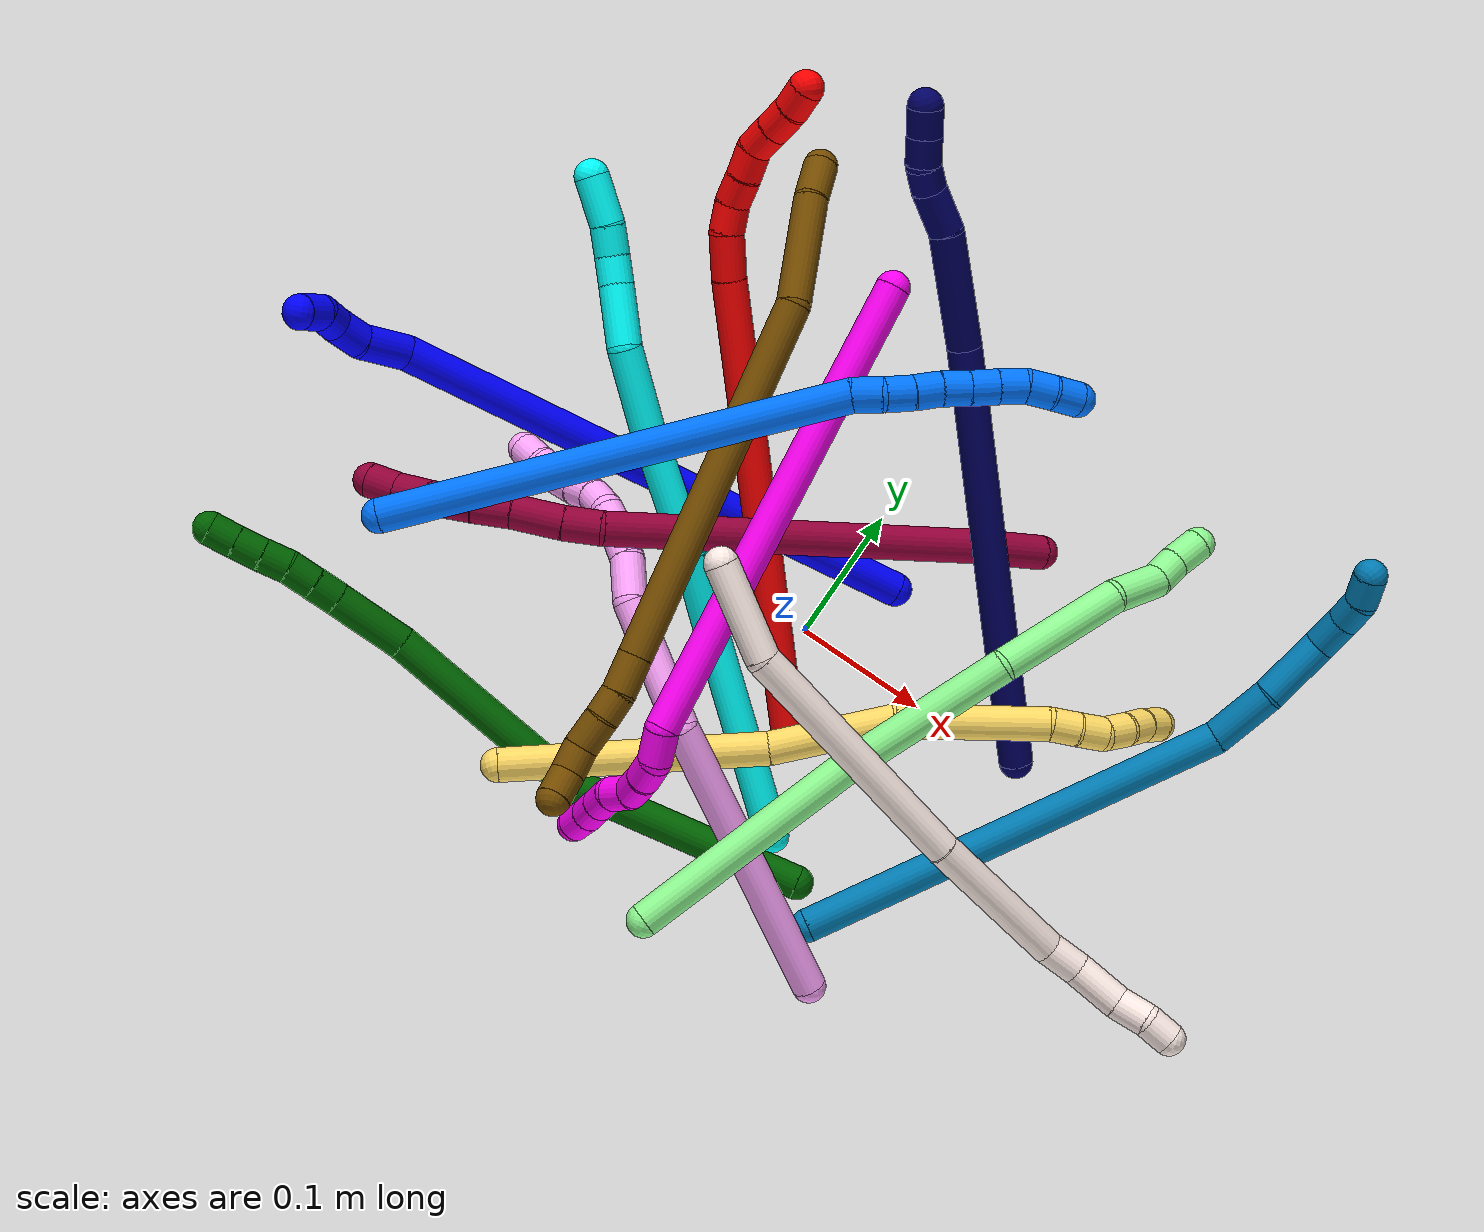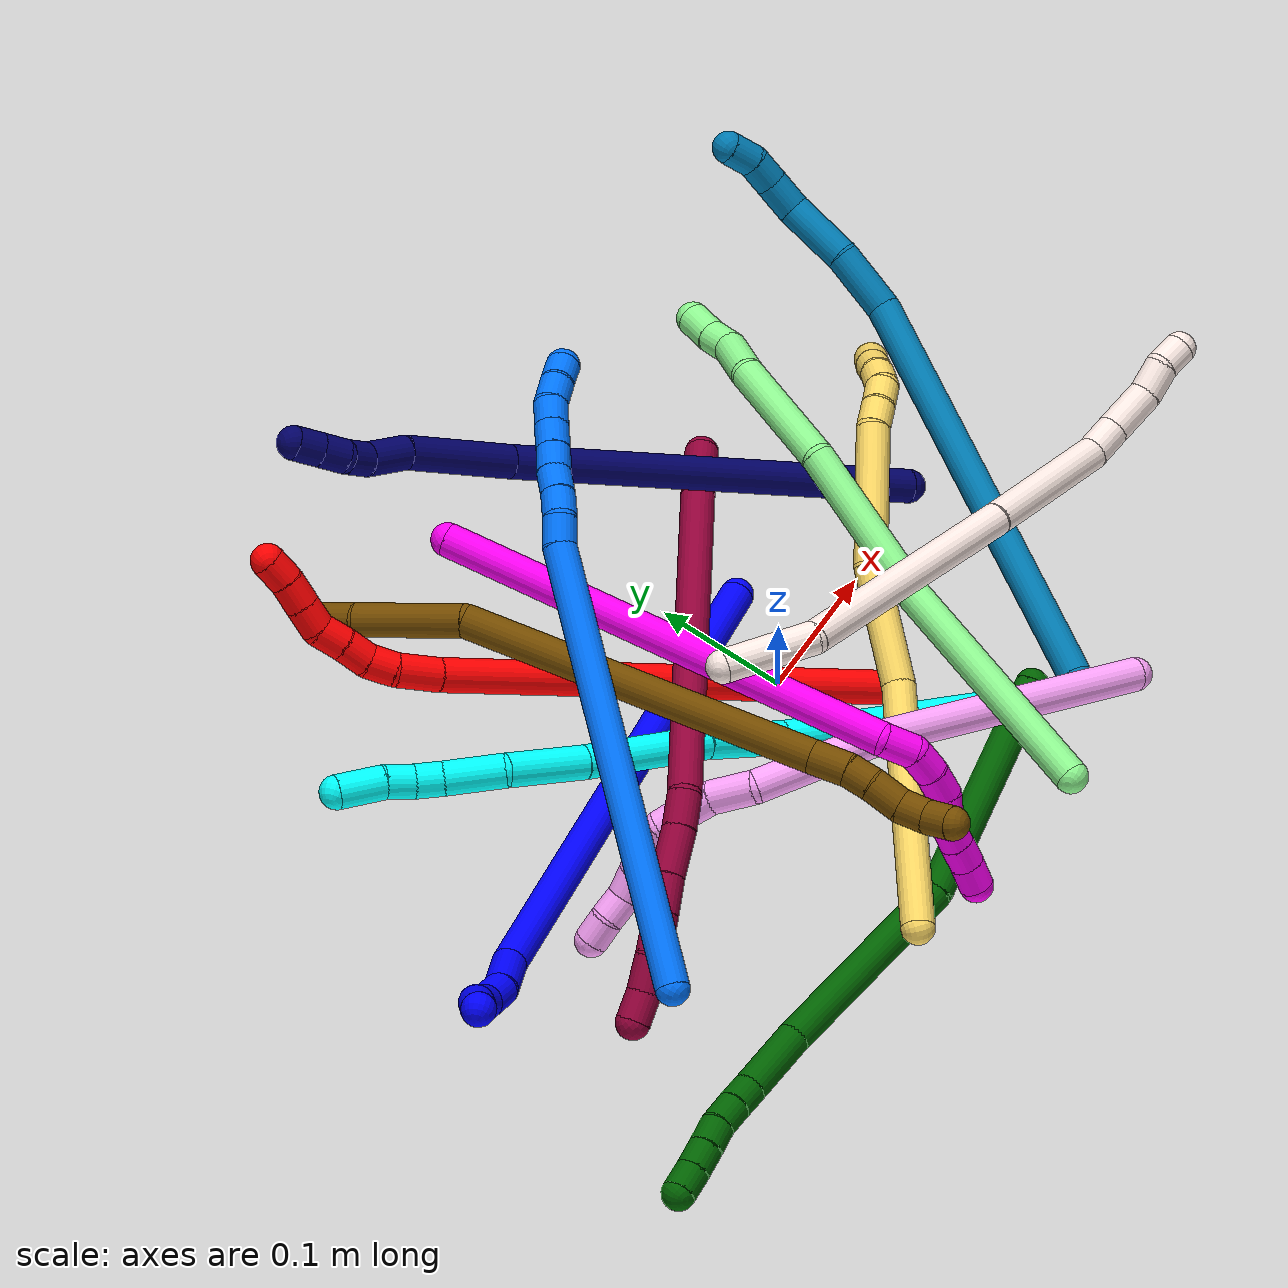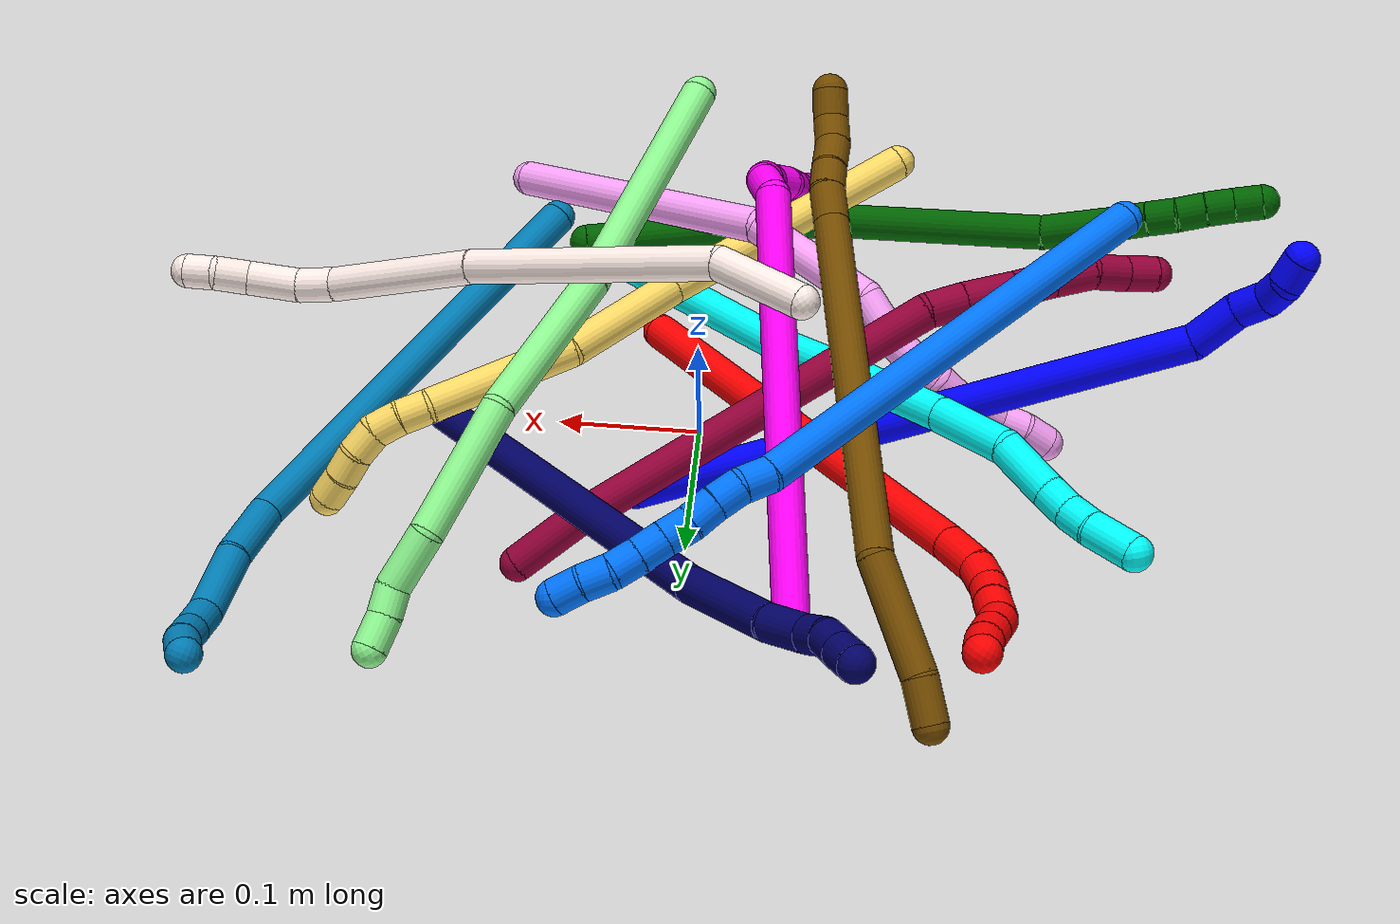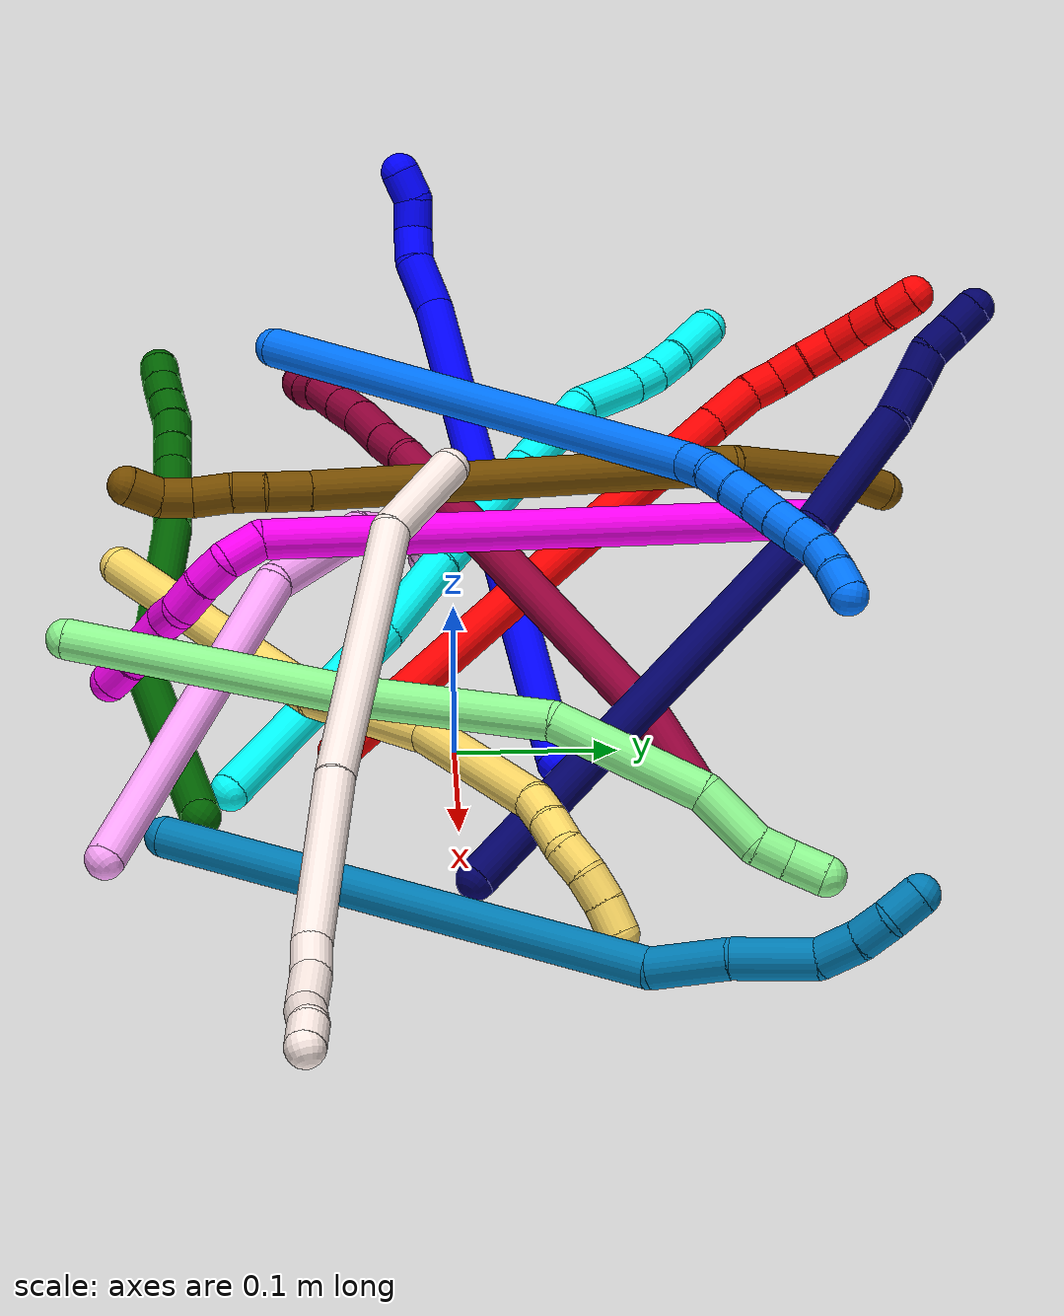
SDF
<sdf version="1.7">
 <world name="default">
  <plugin name="TubeGeneratorPlugin" filename="libtube_generator_plugin.so"/>
  <model name="photoneo_s_sensor">
   <static>1</static>
   <pose>0 0 2 1.57079 1.57079 3.14159</pose>
   <link name="link">
    <inertial><mass>0.1</mass></inertial>
    <sensor name="sensor" type="depth">
     <update_rate>30</update_rate>
     <camera>
      <horizontal_fov>1.22</horizontal_fov>
      <image><width>1920</width><height>1200</height><format>B8G8R8</format></image>
      <clip><near>0.1</near><far>4</far></clip>
      <depth_camera><output>points</output></depth_camera>
     </camera>
     <plugin name="camera_plugin" filename="libgazebo_ros_depth_camera.so">
      <baseline>0.2</baseline>
      <alwaysOn>1</alwaysOn>
      <updateRate>0.0</updateRate>
      <cameraName>camera_ir</cameraName>
      <imageTopicName>/camera/color/image_raw</imageTopicName>
      <cameraInfoTopicName>/camera/color/camera_info</cameraInfoTopicName>
      <depthImageTopicName>/camera/depth/image_raw</depthImageTopicName>
      <depthImageCameraInfoTopicName>/camera/depth/camera_info</depthImageCameraInfoTopicName>
      <pointCloudTopicName>/camera/depth/points</pointCloudTopicName>
      <frameName>fr_optical</frameName>
      <pointCloudCutoff>0.1</pointCloudCutoff>
      <pointCloudCutoffMax>2.0</pointCloudCutoffMax>
      <distortionK1>0</distortionK1>
      <distortionK2>0</distortionK2>
      <distortionK3>0</distortionK3>
      <distortionT1>0</distortionT1>
      <distortionT2>0</distortionT2>
      <CxPrime>0</CxPrime>
      <Cx>0</Cx>
      <Cy>0</Cy>
      <focalLength>0</focalLength>
      <hackBaseline>0</hackBaseline>
     </plugin>
    </sensor>
   </link>
  </model>
  <gravity>0 0 -9.8</gravity>
  <magnetic_field>6e-06 2.3e-05 -4.2e-05</magnetic_field>
  <atmosphere type="adiabatic"/>
  <physics name="default_physics" default="0" type="ode">
   <max_step_size>0.003</max_step_size>
   <real_time_factor>1</real_time_factor>
   <real_time_update_rate>1000</real_time_update_rate>
   <max_contacts>10000</max_contacts>
   <ode>
    <solver>
     <type>quick</type>
     <iters>100</iters>
     <sor>1.3</sor>
     <use_dynamic_moi_rescaling>0</use_dynamic_moi_rescaling>
    </solver>
    <constraints>
     <contact_max_correcting_vel>0</contact_max_correcting_vel>
     <contact_surface_layer>0.001</contact_surface_layer>
     <cfm>0</cfm>
     <erp>0.2</erp>
    </constraints>
   </ode>
  </physics>
  <scene><ambient>0.4 0.4 0.4 1</ambient><background>0.7 0.7 0.7 1</background><shadows>0</shadows></scene>
  <audio><device>default</device></audio>
  <spherical_coordinates>
   <surface_model>EARTH_WGS84</surface_model>
   <latitude_deg>0</latitude_deg>
   <longitude_deg>0</longitude_deg>
   <elevation>0</elevation>
   <heading_deg>0</heading_deg>
  </spherical_coordinates>
  <model name="bin">
   <static>1</static>
   <link name="bottom">
    <collision name="collision-bottom">
     <pose>0 0 -0.01 0 -0 0</pose>
     <geometry><box><size>0.8 0.6 0.02</size></box></geometry>
     <surface>
      <friction><ode><mu>100</mu><mu2>100</mu2></ode></friction>
      <contact><collide_bitmask>65535</collide_bitmask></contact>
     </surface>
    </collision>
   </link>
   <link name="west_wall">
    <collision name="collision-west_wall">
     <pose>-0.41 0 0.1 0 -0 0</pose>
     <geometry><box><size>0.02 0.6 0.2</size></box></geometry>
     <surface>
      <friction><ode><mu>100</mu><mu2>100</mu2></ode></friction>
      <contact><collide_bitmask>65535</collide_bitmask></contact>
     </surface>
    </collision>
   </link>
   <link name="east_wall">
    <collision name="collision-east_wall">
     <pose>0.41 0 0.1 0 -0 0</pose>
     <geometry><box><size>0.02 0.6 0.2</size></box></geometry>
     <surface>
      <friction><ode><mu>100</mu><mu2>100</mu2></ode></friction>
      <contact><collide_bitmask>65535</collide_bitmask></contact>
     </surface>
    </collision>
   </link>
   <link name="south_wall">
    <collision name="collision-south_wall">
     <pose>0 -0.31 0.1 0 -0 0</pose>
     <geometry><box><size>0.8 0.02 0.2</size></box></geometry>
     <surface>
      <friction><ode><mu>100</mu><mu2>100</mu2></ode></friction>
      <contact><collide_bitmask>65535</collide_bitmask></contact>
     </surface>
    </collision>
   </link>
   <link name="north_wall">
    <collision name="collision-north_wall">
     <pose>0 0.31 0.1 0 -0 0</pose>
     <geometry><box><size>0.8 0.02 0.2</size></box></geometry>
     <surface>
      <friction><ode><mu>100</mu><mu2>100</mu2></ode></friction>
      <contact><collide_bitmask>65535</collide_bitmask></contact>
     </surface>
    </collision>
   </link>
  </model>
  <model name="1">
   <static>0</static>
   <link name="1">
    <collision name="collision-cylinder-e_1_1_4">
     <pose>-0.049071 -0.015045 0.193484 0.077603 -0.247663 -0.009664</pose>
     <geometry><cylinder><radius>0.0125</radius><length>0.400352</length></cylinder></geometry>
     <surface>
      <friction><ode><mu>1.16</mu><mu2>1.16</mu2><slip1>0</slip1><slip2>0</slip2></ode></friction>
      <contact><ode><kp>1e+06</kp><kd>1</kd><max_vel>0</max_vel><min_depth>0.001</min_depth></ode></contact>
     </surface>
    </collision>
    <visual name="visual-cylinder-e_1_1_4">
     <pose>-0.049071 -0.015045 0.193484 0.077603 -0.247663 -0.009664</pose>
     <geometry><cylinder><radius>0.0125</radius><length>0.400352</length></cylinder></geometry>
     <material><ambient>0 0 1 1</ambient></material>
    </visual>
    <collision name="collision-cylinder-e_2_4_5">
     <pose>-0.10297 -0.024399 0.403611 -0.329486 -0.267899 0.044799</pose>
     <geometry><cylinder><radius>0.0125</radius><length>0.036479</length></cylinder></geometry>
     <surface>
      <friction><ode><mu>1.16</mu><mu2>1.16</mu2><slip1>0</slip1><slip2>0</slip2></ode></friction>
      <contact><ode><kp>1e+06</kp><kd>1</kd><max_vel>0</max_vel><min_depth>0.001</min_depth></ode></contact>
     </surface>
    </collision>
    <visual name="visual-cylinder-e_2_4_5">
     <pose>-0.10297 -0.024399 0.403611 -0.329486 -0.267899 0.044799</pose>
     <geometry><cylinder><radius>0.0125</radius><length>0.036479</length></cylinder></geometry>
     <material><ambient>0 0 1 1</ambient></material>
    </visual>
    <collision name="collision-cylinder-e_3_5_6">
     <pose>-0.113581 -0.017404 0.430177 -0.130683 -0.523993 0.03509</pose>
     <geometry><cylinder><radius>0.0125</radius><length>0.023117</length></cylinder></geometry>
     <surface>
      <friction><ode><mu>1.16</mu><mu2>1.16</mu2><slip1>0</slip1><slip2>0</slip2></ode></friction>
      <contact><ode><kp>1e+06</kp><kd>1</kd><max_vel>0</max_vel><min_depth>0.001</min_depth></ode></contact>
     </surface>
    </collision>
    <visual name="visual-cylinder-e_3_5_6">
     <pose>-0.113581 -0.017404 0.430177 -0.130683 -0.523993 0.03509</pose>
     <geometry><cylinder><radius>0.0125</radius><length>0.023117</length></cylinder></geometry>
     <material><ambient>0 0 1 1</ambient></material>
    </visual>
    <collision name="collision-cylinder-e_4_6_7">
     <pose>-0.126033 -0.011768 0.446179 -0.619015 -0.729051 0.242845</pose>
     <geometry><cylinder><radius>0.0125</radius><length>0.020021</length></cylinder></geometry>
     <surface>
      <friction><ode><mu>1.16</mu><mu2>1.16</mu2><slip1>0</slip1><slip2>0</slip2></ode></friction>
      <contact><ode><kp>1e+06</kp><kd>1</kd><max_vel>0</max_vel><min_depth>0.001</min_depth></ode></contact>
     </surface>
    </collision>
    <visual name="visual-cylinder-e_4_6_7">
     <pose>-0.126033 -0.011768 0.446179 -0.619015 -0.729051 0.242845</pose>
     <geometry><cylinder><radius>0.0125</radius><length>0.020021</length></cylinder></geometry>
     <material><ambient>0 0 1 1</ambient></material>
    </visual>
    <collision name="collision-cylinder-e_5_7_2">
     <pose>-0.135525 -0.001133 0.459513 -0.715461 -0.285782 0.107459</pose>
     <geometry><cylinder><radius>0.0125</radius><length>0.02003</length></cylinder></geometry>
     <surface>
      <friction><ode><mu>1.16</mu><mu2>1.16</mu2><slip1>0</slip1><slip2>0</slip2></ode></friction>
      <contact><ode><kp>1e+06</kp><kd>1</kd><max_vel>0</max_vel><min_depth>0.001</min_depth></ode></contact>
     </surface>
    </collision>
    <visual name="visual-cylinder-e_5_7_2">
     <pose>-0.135525 -0.001133 0.459513 -0.715461 -0.285782 0.107459</pose>
     <geometry><cylinder><radius>0.0125</radius><length>0.02003</length></cylinder></geometry>
     <material><ambient>0 0 1 1</ambient></material>
    </visual>
    <collision name="collision-sphere-2">
     <pose>-0.138348 0.00517 0.466766 0 -0 0</pose>
     <geometry><sphere><radius>0.0125</radius></sphere></geometry>
     <surface>
      <friction><ode><mu>1.16</mu><mu2>1.16</mu2><slip1>0</slip1><slip2>0</slip2></ode></friction>
      <contact><ode><kp>1e+06</kp><kd>1</kd><max_vel>0</max_vel><min_depth>0.001</min_depth></ode></contact>
     </surface>
    </collision>
    <visual name="visual-sphere-2">
     <pose>-0.138348 0.00517 0.466766 0 -0 0</pose>
     <geometry><sphere><radius>0.0125</radius></sphere></geometry>
     <material><ambient>0 0 1 1</ambient></material>
    </visual>
    <collision name="collision-sphere-7">
     <pose>-0.132702 -0.007436 0.45226 0 -0 0</pose>
     <geometry><sphere><radius>0.0125</radius></sphere></geometry>
     <surface>
      <friction><ode><mu>1.16</mu><mu2>1.16</mu2><slip1>0</slip1><slip2>0</slip2></ode></friction>
      <contact><ode><kp>1e+06</kp><kd>1</kd><max_vel>0</max_vel><min_depth>0.001</min_depth></ode></contact>
     </surface>
    </collision>
    <visual name="visual-sphere-7">
     <pose>-0.132702 -0.007436 0.45226 0 -0 0</pose>
     <geometry><sphere><radius>0.0125</radius></sphere></geometry>
     <material><ambient>0 0 1 1</ambient></material>
    </visual>
    <collision name="collision-sphere-6">
     <pose>-0.119364 -0.0161 0.440099 0 -0 0</pose>
     <geometry><sphere><radius>0.0125</radius></sphere></geometry>
     <surface>
      <friction><ode><mu>1.16</mu><mu2>1.16</mu2><slip1>0</slip1><slip2>0</slip2></ode></friction>
      <contact><ode><kp>1e+06</kp><kd>1</kd><max_vel>0</max_vel><min_depth>0.001</min_depth></ode></contact>
     </surface>
    </collision>
    <visual name="visual-sphere-6">
     <pose>-0.119364 -0.0161 0.440099 0 -0 0</pose>
     <geometry><sphere><radius>0.0125</radius></sphere></geometry>
     <material><ambient>0 0 1 1</ambient></material>
    </visual>
    <collision name="collision-sphere-5">
     <pose>-0.107798 -0.018708 0.420254 0 -0 0</pose>
     <geometry><sphere><radius>0.0125</radius></sphere></geometry>
     <surface>
      <friction><ode><mu>1.16</mu><mu2>1.16</mu2><slip1>0</slip1><slip2>0</slip2></ode></friction>
      <contact><ode><kp>1e+06</kp><kd>1</kd><max_vel>0</max_vel><min_depth>0.001</min_depth></ode></contact>
     </surface>
    </collision>
    <visual name="visual-sphere-5">
     <pose>-0.107798 -0.018708 0.420254 0 -0 0</pose>
     <geometry><sphere><radius>0.0125</radius></sphere></geometry>
     <material><ambient>0 0 1 1</ambient></material>
    </visual>
    <collision name="collision-sphere-1">
     <geometry><sphere><radius>0.0125</radius></sphere></geometry>
     <surface>
      <friction><ode><mu>1.16</mu><mu2>1.16</mu2><slip1>0</slip1><slip2>0</slip2></ode></friction>
      <contact><ode><kp>1e+06</kp><kd>1</kd><max_vel>0</max_vel><min_depth>0.001</min_depth></ode></contact>
     </surface>
    </collision>
    <visual name="visual-sphere-1">
     <geometry><sphere><radius>0.0125</radius></sphere></geometry>
     <material><ambient>0 0 1 1</ambient></material>
    </visual>
    <collision name="collision-sphere-4">
     <pose>-0.098142 -0.030091 0.386969 0 -0 0</pose>
     <geometry><sphere><radius>0.0125</radius></sphere></geometry>
     <surface>
      <friction><ode><mu>1.16</mu><mu2>1.16</mu2><slip1>0</slip1><slip2>0</slip2></ode></friction>
      <contact><ode><kp>1e+06</kp><kd>1</kd><max_vel>0</max_vel><min_depth>0.001</min_depth></ode></contact>
     </surface>
    </collision>
    <visual name="visual-sphere-4">
     <pose>-0.098142 -0.030091 0.386969 0 -0 0</pose>
     <geometry><sphere><radius>0.0125</radius></sphere></geometry>
     <material><ambient>0 0 1 1</ambient></material>
    </visual>
    <inertial>
     <pose>-0.062531 -0.015148 0.240534 0 -0 0</pose>
     <mass>0.5</mass>
     <inertia>
      <ixx>0.005148</ixx>
      <ixy>0</ixy>
      <ixz>0</ixz>
      <iyy>0.005308</iyy>
      <iyz>0</iyz>
      <izz>0.001755</izz>
     </inertia>
    </inertial>
   </link>
   <pose>0.037433 0.061786 0.011498 1.24947 0.696426 -1.35951</pose>
  </model>
  <model name="2">
   <static>0</static>
   <link name="2">
    <collision name="collision-cylinder-e_1_1_4">
     <pose>-0.009867 0.170317 0.007344 -1.5277 -0.057812 0.055374</pose>
     <geometry><cylinder><radius>0.0125</radius><length>0.341521</length></cylinder></geometry>
     <surface>
      <friction><ode><mu>1.16</mu><mu2>1.16</mu2><slip1>0</slip1><slip2>0</slip2></ode></friction>
      <contact><ode><kp>1e+06</kp><kd>1</kd><max_vel>0</max_vel><min_depth>0.001</min_depth></ode></contact>
     </surface>
    </collision>
    <visual name="visual-cylinder-e_1_1_4">
     <pose>-0.009867 0.170317 0.007344 -1.5277 -0.057812 0.055374</pose>
     <geometry><cylinder><radius>0.0125</radius><length>0.341521</length></cylinder></geometry>
     <material><ambient>1 0 0 1</ambient></material>
    </visual>
    <collision name="collision-cylinder-e_2_4_5">
     <pose>-0.019527 0.357098 0.014775 -1.56551 0.012541 -0.012475</pose>
     <geometry><cylinder><radius>0.0125</radius><length>0.032932</length></cylinder></geometry>
     <surface>
      <friction><ode><mu>1.16</mu><mu2>1.16</mu2><slip1>0</slip1><slip2>0</slip2></ode></friction>
      <contact><ode><kp>1e+06</kp><kd>1</kd><max_vel>0</max_vel><min_depth>0.001</min_depth></ode></contact>
     </surface>
    </collision>
    <visual name="visual-cylinder-e_2_4_5">
     <pose>-0.019527 0.357098 0.014775 -1.56551 0.012541 -0.012475</pose>
     <geometry><cylinder><radius>0.0125</radius><length>0.032932</length></cylinder></geometry>
     <material><ambient>1 0 0 1</ambient></material>
    </visual>
    <collision name="collision-cylinder-e_3_5_6">
     <pose>-0.017939 0.383748 0.01262 -1.78741 0.131684 -0.163685</pose>
     <geometry><cylinder><radius>0.0125</radius><length>0.021041</length></cylinder></geometry>
     <surface>
      <friction><ode><mu>1.16</mu><mu2>1.16</mu2><slip1>0</slip1><slip2>0</slip2></ode></friction>
      <contact><ode><kp>1e+06</kp><kd>1</kd><max_vel>0</max_vel><min_depth>0.001</min_depth></ode></contact>
     </surface>
    </collision>
    <visual name="visual-cylinder-e_3_5_6">
     <pose>-0.017939 0.383748 0.01262 -1.78741 0.131684 -0.163685</pose>
     <geometry><cylinder><radius>0.0125</radius><length>0.021041</length></cylinder></geometry>
     <material><ambient>1 0 0 1</ambient></material>
    </visual>
    <collision name="collision-cylinder-e_4_6_7">
     <pose>-0.012112 0.403196 0.008229 -1.79887 0.437374 -0.545526</pose>
     <geometry><cylinder><radius>0.0125</radius><length>0.020992</length></cylinder></geometry>
     <surface>
      <friction><ode><mu>1.16</mu><mu2>1.16</mu2><slip1>0</slip1><slip2>0</slip2></ode></friction>
      <contact><ode><kp>1e+06</kp><kd>1</kd><max_vel>0</max_vel><min_depth>0.001</min_depth></ode></contact>
     </surface>
    </collision>
    <visual name="visual-cylinder-e_4_6_7">
     <pose>-0.012112 0.403196 0.008229 -1.79887 0.437374 -0.545526</pose>
     <geometry><cylinder><radius>0.0125</radius><length>0.020992</length></cylinder></geometry>
     <material><ambient>1 0 0 1</ambient></material>
    </visual>
    <collision name="collision-cylinder-e_5_7_8">
     <pose>-0.004047 0.422247 0.003636 -1.8153 0.344355 -0.438092</pose>
     <geometry><cylinder><radius>0.0125</radius><length>0.021439</length></cylinder></geometry>
     <surface>
      <friction><ode><mu>1.16</mu><mu2>1.16</mu2><slip1>0</slip1><slip2>0</slip2></ode></friction>
      <contact><ode><kp>1e+06</kp><kd>1</kd><max_vel>0</max_vel><min_depth>0.001</min_depth></ode></contact>
     </surface>
    </collision>
    <visual name="visual-cylinder-e_5_7_8">
     <pose>-0.004047 0.422247 0.003636 -1.8153 0.344355 -0.438092</pose>
     <geometry><cylinder><radius>0.0125</radius><length>0.021439</length></cylinder></geometry>
     <material><ambient>1 0 0 1</ambient></material>
    </visual>
    <collision name="collision-cylinder-e_6_8_9">
     <pose>0.006892 0.438958 -0.001477 -1.93913 0.778731 -1.07815</pose>
     <geometry><cylinder><radius>0.0125</radius><length>0.020843</length></cylinder></geometry>
     <surface>
      <friction><ode><mu>1.16</mu><mu2>1.16</mu2><slip1>0</slip1><slip2>0</slip2></ode></friction>
      <contact><ode><kp>1e+06</kp><kd>1</kd><max_vel>0</max_vel><min_depth>0.001</min_depth></ode></contact>
     </surface>
    </collision>
    <visual name="visual-cylinder-e_6_8_9">
     <pose>0.006892 0.438958 -0.001477 -1.93913 0.778731 -1.07815</pose>
     <geometry><cylinder><radius>0.0125</radius><length>0.020843</length></cylinder></geometry>
     <material><ambient>1 0 0 1</ambient></material>
    </visual>
    <collision name="collision-cylinder-e_7_9_10">
     <pose>0.02167 0.452833 -0.006792 -1.9341 0.786649 -1.08331</pose>
     <geometry><cylinder><radius>0.0125</radius><length>0.02107</length></cylinder></geometry>
     <surface>
      <friction><ode><mu>1.16</mu><mu2>1.16</mu2><slip1>0</slip1><slip2>0</slip2></ode></friction>
      <contact><ode><kp>1e+06</kp><kd>1</kd><max_vel>0</max_vel><min_depth>0.001</min_depth></ode></contact>
     </surface>
    </collision>
    <visual name="visual-cylinder-e_7_9_10">
     <pose>0.02167 0.452833 -0.006792 -1.9341 0.786649 -1.08331</pose>
     <geometry><cylinder><radius>0.0125</radius><length>0.02107</length></cylinder></geometry>
     <material><ambient>1 0 0 1</ambient></material>
    </visual>
    <collision name="collision-cylinder-e_8_10_2">
     <pose>0.035132 0.467581 -0.011638 -1.84614 0.637944 -0.823106</pose>
     <geometry><cylinder><radius>0.0125</radius><length>0.020163</length></cylinder></geometry>
     <surface>
      <friction><ode><mu>1.16</mu><mu2>1.16</mu2><slip1>0</slip1><slip2>0</slip2></ode></friction>
      <contact><ode><kp>1e+06</kp><kd>1</kd><max_vel>0</max_vel><min_depth>0.001</min_depth></ode></contact>
     </surface>
    </collision>
    <visual name="visual-cylinder-e_8_10_2">
     <pose>0.035132 0.467581 -0.011638 -1.84614 0.637944 -0.823106</pose>
     <geometry><cylinder><radius>0.0125</radius><length>0.020163</length></cylinder></geometry>
     <material><ambient>1 0 0 1</ambient></material>
    </visual>
    <collision name="collision-sphere-2">
     <pose>0.041136 0.475374 -0.01384 0 -0 0</pose>
     <geometry><sphere><radius>0.0125</radius></sphere></geometry>
     <surface>
      <friction><ode><mu>1.16</mu><mu2>1.16</mu2><slip1>0</slip1><slip2>0</slip2></ode></friction>
      <contact><ode><kp>1e+06</kp><kd>1</kd><max_vel>0</max_vel><min_depth>0.001</min_depth></ode></contact>
     </surface>
    </collision>
    <visual name="visual-sphere-2">
     <pose>0.041136 0.475374 -0.01384 0 -0 0</pose>
     <geometry><sphere><radius>0.0125</radius></sphere></geometry>
     <material><ambient>1 0 0 1</ambient></material>
    </visual>
    <collision name="collision-sphere-10">
     <pose>0.029129 0.459787 -0.009436 0 -0 0</pose>
     <geometry><sphere><radius>0.0125</radius></sphere></geometry>
     <surface>
      <friction><ode><mu>1.16</mu><mu2>1.16</mu2><slip1>0</slip1><slip2>0</slip2></ode></friction>
      <contact><ode><kp>1e+06</kp><kd>1</kd><max_vel>0</max_vel><min_depth>0.001</min_depth></ode></contact>
     </surface>
    </collision>
    <visual name="visual-sphere-10">
     <pose>0.029129 0.459787 -0.009436 0 -0 0</pose>
     <geometry><sphere><radius>0.0125</radius></sphere></geometry>
     <material><ambient>1 0 0 1</ambient></material>
    </visual>
    <collision name="collision-sphere-9">
     <pose>0.014211 0.445879 -0.004148 0 -0 0</pose>
     <geometry><sphere><radius>0.0125</radius></sphere></geometry>
     <surface>
      <friction><ode><mu>1.16</mu><mu2>1.16</mu2><slip1>0</slip1><slip2>0</slip2></ode></friction>
      <contact><ode><kp>1e+06</kp><kd>1</kd><max_vel>0</max_vel><min_depth>0.001</min_depth></ode></contact>
     </surface>
    </collision>
    <visual name="visual-sphere-9">
     <pose>0.014211 0.445879 -0.004148 0 -0 0</pose>
     <geometry><sphere><radius>0.0125</radius></sphere></geometry>
     <material><ambient>1 0 0 1</ambient></material>
    </visual>
    <collision name="collision-sphere-4">
     <pose>-0.019733 0.340634 0.014688 0 -0 0</pose>
     <geometry><sphere><radius>0.0125</radius></sphere></geometry>
     <surface>
      <friction><ode><mu>1.16</mu><mu2>1.16</mu2><slip1>0</slip1><slip2>0</slip2></ode></friction>
      <contact><ode><kp>1e+06</kp><kd>1</kd><max_vel>0</max_vel><min_depth>0.001</min_depth></ode></contact>
     </surface>
    </collision>
    <visual name="visual-sphere-4">
     <pose>-0.019733 0.340634 0.014688 0 -0 0</pose>
     <geometry><sphere><radius>0.0125</radius></sphere></geometry>
     <material><ambient>1 0 0 1</ambient></material>
    </visual>
    <collision name="collision-sphere-1">
     <geometry><sphere><radius>0.0125</radius></sphere></geometry>
     <surface>
      <friction><ode><mu>1.16</mu><mu2>1.16</mu2><slip1>0</slip1><slip2>0</slip2></ode></friction>
      <contact><ode><kp>1e+06</kp><kd>1</kd><max_vel>0</max_vel><min_depth>0.001</min_depth></ode></contact>
     </surface>
    </collision>
    <visual name="visual-sphere-1">
     <geometry><sphere><radius>0.0125</radius></sphere></geometry>
     <material><ambient>1 0 0 1</ambient></material>
    </visual>
    <collision name="collision-sphere-8">
     <pose>-0.000428 0.432038 0.001194 0 -0 0</pose>
     <geometry><sphere><radius>0.0125</radius></sphere></geometry>
     <surface>
      <friction><ode><mu>1.16</mu><mu2>1.16</mu2><slip1>0</slip1><slip2>0</slip2></ode></friction>
      <contact><ode><kp>1e+06</kp><kd>1</kd><max_vel>0</max_vel><min_depth>0.001</min_depth></ode></contact>
     </surface>
    </collision>
    <visual name="visual-sphere-8">
     <pose>-0.000428 0.432038 0.001194 0 -0 0</pose>
     <geometry><sphere><radius>0.0125</radius></sphere></geometry>
     <material><ambient>1 0 0 1</ambient></material>
    </visual>
    <collision name="collision-sphere-5">
     <pose>-0.01932 0.373562 0.014862 0 -0 0</pose>
     <geometry><sphere><radius>0.0125</radius></sphere></geometry>
     <surface>
      <friction><ode><mu>1.16</mu><mu2>1.16</mu2><slip1>0</slip1><slip2>0</slip2></ode></friction>
      <contact><ode><kp>1e+06</kp><kd>1</kd><max_vel>0</max_vel><min_depth>0.001</min_depth></ode></contact>
     </surface>
    </collision>
    <visual name="visual-sphere-5">
     <pose>-0.01932 0.373562 0.014862 0 -0 0</pose>
     <geometry><sphere><radius>0.0125</radius></sphere></geometry>
     <material><ambient>1 0 0 1</ambient></material>
    </visual>
    <collision name="collision-sphere-6">
     <pose>-0.016557 0.393934 0.010379 0 -0 0</pose>
     <geometry><sphere><radius>0.0125</radius></sphere></geometry>
     <surface>
      <friction><ode><mu>1.16</mu><mu2>1.16</mu2><slip1>0</slip1><slip2>0</slip2></ode></friction>
      <contact><ode><kp>1e+06</kp><kd>1</kd><max_vel>0</max_vel><min_depth>0.001</min_depth></ode></contact>
     </surface>
    </collision>
    <visual name="visual-sphere-6">
     <pose>-0.016557 0.393934 0.010379 0 -0 0</pose>
     <geometry><sphere><radius>0.0125</radius></sphere></geometry>
     <material><ambient>1 0 0 1</ambient></material>
    </visual>
    <collision name="collision-sphere-7">
     <pose>-0.007666 0.412457 0.006079 0 -0 0</pose>
     <geometry><sphere><radius>0.0125</radius></sphere></geometry>
     <surface>
      <friction><ode><mu>1.16</mu><mu2>1.16</mu2><slip1>0</slip1><slip2>0</slip2></ode></friction>
      <contact><ode><kp>1e+06</kp><kd>1</kd><max_vel>0</max_vel><min_depth>0.001</min_depth></ode></contact>
     </surface>
    </collision>
    <visual name="visual-sphere-7">
     <pose>-0.007666 0.412457 0.006079 0 -0 0</pose>
     <geometry><sphere><radius>0.0125</radius></sphere></geometry>
     <material><ambient>1 0 0 1</ambient></material>
    </visual>
    <inertial>
     <pose>-0.006845 0.247271 0.006205 0 -0 0</pose>
     <mass>0.5</mass>
     <inertia>
      <ixx>0.003515</ixx>
      <ixy>0</ixy>
      <ixz>0</ixz>
      <iyy>0.000372</iyy>
      <iyz>0</iyz>
      <izz>-0.003149</izz>
     </inertia>
    </inertial>
   </link>
   <pose>0.034921 -0.071985 0.020597 0.552321 -0.82901 0.229746</pose>
  </model>
  <model name="3">
   <static>0</static>
   <link name="3">
    <collision name="collision-cylinder-e_1_1_4">
     <pose>-0.04315 0.051073 0.043244 -0.868223 -0.572697 0.271332</pose>
     <geometry><cylinder><radius>0.0125</radius><length>0.159253</length></cylinder></geometry>
     <surface>
      <friction><ode><mu>1.16</mu><mu2>1.16</mu2><slip1>0</slip1><slip2>0</slip2></ode></friction>
      <contact><ode><kp>1e+06</kp><kd>1</kd><max_vel>0</max_vel><min_depth>0.001</min_depth></ode></contact>
     </surface>
    </collision>
    <visual name="visual-cylinder-e_1_1_4">
     <pose>-0.04315 0.051073 0.043244 -0.868223 -0.572697 0.271332</pose>
     <geometry><cylinder><radius>0.0125</radius><length>0.159253</length></cylinder></geometry>
     <material><ambient>0.003922 1 0.996078 1</ambient></material>
    </visual>
    <collision name="collision-cylinder-e_2_4_5">
     <pose>-0.100035 0.125413 0.102408 -0.970688 -0.453358 0.242103</pose>
     <geometry><cylinder><radius>0.0125</radius><length>0.062722</length></cylinder></geometry>
     <surface>
      <friction><ode><mu>1.16</mu><mu2>1.16</mu2><slip1>0</slip1><slip2>0</slip2></ode></friction>
      <contact><ode><kp>1e+06</kp><kd>1</kd><max_vel>0</max_vel><min_depth>0.001</min_depth></ode></contact>
     </surface>
    </collision>
    <visual name="visual-cylinder-e_2_4_5">
     <pose>-0.100035 0.125413 0.102408 -0.970688 -0.453358 0.242103</pose>
     <geometry><cylinder><radius>0.0125</radius><length>0.062722</length></cylinder></geometry>
     <material><ambient>0.003922 1 0.996078 1</ambient></material>
    </visual>
    <collision name="collision-cylinder-e_3_5_6">
     <pose>-0.13744 0.180108 0.145463 -0.858603 -0.51813 0.24146</pose>
     <geometry><cylinder><radius>0.0125</radius><length>0.095587</length></cylinder></geometry>
     <surface>
      <friction><ode><mu>1.16</mu><mu2>1.16</mu2><slip1>0</slip1><slip2>0</slip2></ode></friction>
      <contact><ode><kp>1e+06</kp><kd>1</kd><max_vel>0</max_vel><min_depth>0.001</min_depth></ode></contact>
     </surface>
    </collision>
    <visual name="visual-cylinder-e_3_5_6">
     <pose>-0.13744 0.180108 0.145463 -0.858603 -0.51813 0.24146</pose>
     <geometry><cylinder><radius>0.0125</radius><length>0.095587</length></cylinder></geometry>
     <material><ambient>0.003922 1 0.996078 1</ambient></material>
    </visual>
    <collision name="collision-cylinder-e_4_6_7">
     <pose>-0.176589 0.23217 0.188396 -0.917323 -0.537195 0.270171</pose>
     <geometry><cylinder><radius>0.0125</radius><length>0.060496</length></cylinder></geometry>
     <surface>
      <friction><ode><mu>1.16</mu><mu2>1.16</mu2><slip1>0</slip1><slip2>0</slip2></ode></friction>
      <contact><ode><kp>1e+06</kp><kd>1</kd><max_vel>0</max_vel><min_depth>0.001</min_depth></ode></contact>
     </surface>
    </collision>
    <visual name="visual-cylinder-e_4_6_7">
     <pose>-0.176589 0.23217 0.188396 -0.917323 -0.537195 0.270171</pose>
     <geometry><cylinder><radius>0.0125</radius><length>0.060496</length></cylinder></geometry>
     <material><ambient>0.003922 1 0.996078 1</ambient></material>
    </visual>
    <collision name="collision-cylinder-e_5_7_8">
     <pose>-0.209404 0.26258 0.21348 -0.811181 -0.909745 0.414003</pose>
     <geometry><cylinder><radius>0.0125</radius><length>0.043924</length></cylinder></geometry>
     <surface>
      <friction><ode><mu>1.16</mu><mu2>1.16</mu2><slip1>0</slip1><slip2>0</slip2></ode></friction>
      <contact><ode><kp>1e+06</kp><kd>1</kd><max_vel>0</max_vel><min_depth>0.001</min_depth></ode></contact>
     </surface>
    </collision>
    <visual name="visual-cylinder-e_5_7_8">
     <pose>-0.209404 0.26258 0.21348 -0.811181 -0.909745 0.414003</pose>
     <geometry><cylinder><radius>0.0125</radius><length>0.043924</length></cylinder></geometry>
     <material><ambient>0.003922 1 0.996078 1</ambient></material>
    </visual>
    <collision name="collision-cylinder-e_6_8_9">
     <pose>-0.234514 0.277788 0.227289 -0.876332 -0.833021 0.408771</pose>
     <geometry><cylinder><radius>0.0125</radius><length>0.021015</length></cylinder></geometry>
     <surface>
      <friction><ode><mu>1.16</mu><mu2>1.16</mu2><slip1>0</slip1><slip2>0</slip2></ode></friction>
      <contact><ode><kp>1e+06</kp><kd>1</kd><max_vel>0</max_vel><min_depth>0.001</min_depth></ode></contact>
     </surface>
    </collision>
    <visual name="visual-cylinder-e_6_8_9">
     <pose>-0.234514 0.277788 0.227289 -0.876332 -0.833021 0.408771</pose>
     <geometry><cylinder><radius>0.0125</radius><length>0.021015</length></cylinder></geometry>
     <material><ambient>0.003922 1 0.996078 1</ambient></material>
    </visual>
    <collision name="collision-cylinder-e_7_9_10">
     <pose>-0.248955 0.290597 0.236529 -1.00197 -0.650598 0.365262</pose>
     <geometry><cylinder><radius>0.0125</radius><length>0.022012</length></cylinder></geometry>
     <surface>
      <friction><ode><mu>1.16</mu><mu2>1.16</mu2><slip1>0</slip1><slip2>0</slip2></ode></friction>
      <contact><ode><kp>1e+06</kp><kd>1</kd><max_vel>0</max_vel><min_depth>0.001</min_depth></ode></contact>
     </surface>
    </collision>
    <visual name="visual-cylinder-e_7_9_10">
     <pose>-0.248955 0.290597 0.236529 -1.00197 -0.650598 0.365262</pose>
     <geometry><cylinder><radius>0.0125</radius><length>0.022012</length></cylinder></geometry>
     <material><ambient>0.003922 1 0.996078 1</ambient></material>
    </visual>
    <collision name="collision-cylinder-e_8_10_2">
     <pose>-0.265994 0.307847 0.2513 -0.776215 -0.634619 0.266937</pose>
     <geometry><cylinder><radius>0.0125</radius><length>0.034992</length></cylinder></geometry>
     <surface>
      <friction><ode><mu>1.16</mu><mu2>1.16</mu2><slip1>0</slip1><slip2>0</slip2></ode></friction>
      <contact><ode><kp>1e+06</kp><kd>1</kd><max_vel>0</max_vel><min_depth>0.001</min_depth></ode></contact>
     </surface>
    </collision>
    <visual name="visual-cylinder-e_8_10_2">
     <pose>-0.265994 0.307847 0.2513 -0.776215 -0.634619 0.266937</pose>
     <geometry><cylinder><radius>0.0125</radius><length>0.034992</length></cylinder></geometry>
     <material><ambient>0.003922 1 0.996078 1</ambient></material>
    </visual>
    <collision name="collision-sphere-2">
     <pose>-0.276367 0.317718 0.261354 0 -0 0</pose>
     <geometry><sphere><radius>0.0125</radius></sphere></geometry>
     <surface>
      <friction><ode><mu>1.16</mu><mu2>1.16</mu2><slip1>0</slip1><slip2>0</slip2></ode></friction>
      <contact><ode><kp>1e+06</kp><kd>1</kd><max_vel>0</max_vel><min_depth>0.001</min_depth></ode></contact>
     </surface>
    </collision>
    <visual name="visual-sphere-2">
     <pose>-0.276367 0.317718 0.261354 0 -0 0</pose>
     <geometry><sphere><radius>0.0125</radius></sphere></geometry>
     <material><ambient>0.003922 1 0.996078 1</ambient></material>
    </visual>
    <collision name="collision-sphere-10">
     <pose>-0.255621 0.297976 0.241246 0 -0 0</pose>
     <geometry><sphere><radius>0.0125</radius></sphere></geometry>
     <surface>
      <friction><ode><mu>1.16</mu><mu2>1.16</mu2><slip1>0</slip1><slip2>0</slip2></ode></friction>
      <contact><ode><kp>1e+06</kp><kd>1</kd><max_vel>0</max_vel><min_depth>0.001</min_depth></ode></contact>
     </surface>
    </collision>
    <visual name="visual-sphere-10">
     <pose>-0.255621 0.297976 0.241246 0 -0 0</pose>
     <geometry><sphere><radius>0.0125</radius></sphere></geometry>
     <material><ambient>0.003922 1 0.996078 1</ambient></material>
    </visual>
    <collision name="collision-sphere-9">
     <pose>-0.242289 0.283219 0.231812 0 -0 0</pose>
     <geometry><sphere><radius>0.0125</radius></sphere></geometry>
     <surface>
      <friction><ode><mu>1.16</mu><mu2>1.16</mu2><slip1>0</slip1><slip2>0</slip2></ode></friction>
      <contact><ode><kp>1e+06</kp><kd>1</kd><max_vel>0</max_vel><min_depth>0.001</min_depth></ode></contact>
     </surface>
    </collision>
    <visual name="visual-sphere-9">
     <pose>-0.242289 0.283219 0.231812 0 -0 0</pose>
     <geometry><sphere><radius>0.0125</radius></sphere></geometry>
     <material><ambient>0.003922 1 0.996078 1</ambient></material>
    </visual>
    <collision name="collision-sphere-4">
     <pose>-0.086299 0.102146 0.086487 0 -0 0</pose>
     <geometry><sphere><radius>0.0125</radius></sphere></geometry>
     <surface>
      <friction><ode><mu>1.16</mu><mu2>1.16</mu2><slip1>0</slip1><slip2>0</slip2></ode></friction>
      <contact><ode><kp>1e+06</kp><kd>1</kd><max_vel>0</max_vel><min_depth>0.001</min_depth></ode></contact>
     </surface>
    </collision>
    <visual name="visual-sphere-4">
     <pose>-0.086299 0.102146 0.086487 0 -0 0</pose>
     <geometry><sphere><radius>0.0125</radius></sphere></geometry>
     <material><ambient>0.003922 1 0.996078 1</ambient></material>
    </visual>
    <collision name="collision-sphere-1">
     <geometry><sphere><radius>0.0125</radius></sphere></geometry>
     <surface>
      <friction><ode><mu>1.16</mu><mu2>1.16</mu2><slip1>0</slip1><slip2>0</slip2></ode></friction>
      <contact><ode><kp>1e+06</kp><kd>1</kd><max_vel>0</max_vel><min_depth>0.001</min_depth></ode></contact>
     </surface>
    </collision>
    <visual name="visual-sphere-1">
     <geometry><sphere><radius>0.0125</radius></sphere></geometry>
     <material><ambient>0.003922 1 0.996078 1</ambient></material>
    </visual>
    <collision name="collision-sphere-8">
     <pose>-0.226739 0.272357 0.222765 0 -0 0</pose>
     <geometry><sphere><radius>0.0125</radius></sphere></geometry>
     <surface>
      <friction><ode><mu>1.16</mu><mu2>1.16</mu2><slip1>0</slip1><slip2>0</slip2></ode></friction>
      <contact><ode><kp>1e+06</kp><kd>1</kd><max_vel>0</max_vel><min_depth>0.001</min_depth></ode></contact>
     </surface>
    </collision>
    <visual name="visual-sphere-8">
     <pose>-0.226739 0.272357 0.222765 0 -0 0</pose>
     <geometry><sphere><radius>0.0125</radius></sphere></geometry>
     <material><ambient>0.003922 1 0.996078 1</ambient></material>
    </visual>
    <collision name="collision-sphere-5">
     <pose>-0.11377 0.14868 0.11833 0 -0 0</pose>
     <geometry><sphere><radius>0.0125</radius></sphere></geometry>
     <surface>
      <friction><ode><mu>1.16</mu><mu2>1.16</mu2><slip1>0</slip1><slip2>0</slip2></ode></friction>
      <contact><ode><kp>1e+06</kp><kd>1</kd><max_vel>0</max_vel><min_depth>0.001</min_depth></ode></contact>
     </surface>
    </collision>
    <visual name="visual-sphere-5">
     <pose>-0.11377 0.14868 0.11833 0 -0 0</pose>
     <geometry><sphere><radius>0.0125</radius></sphere></geometry>
     <material><ambient>0.003922 1 0.996078 1</ambient></material>
    </visual>
    <collision name="collision-sphere-6">
     <pose>-0.161111 0.211536 0.172597 0 -0 0</pose>
     <geometry><sphere><radius>0.0125</radius></sphere></geometry>
     <surface>
      <friction><ode><mu>1.16</mu><mu2>1.16</mu2><slip1>0</slip1><slip2>0</slip2></ode></friction>
      <contact><ode><kp>1e+06</kp><kd>1</kd><max_vel>0</max_vel><min_depth>0.001</min_depth></ode></contact>
     </surface>
    </collision>
    <visual name="visual-sphere-6">
     <pose>-0.161111 0.211536 0.172597 0 -0 0</pose>
     <geometry><sphere><radius>0.0125</radius></sphere></geometry>
     <material><ambient>0.003922 1 0.996078 1</ambient></material>
    </visual>
    <collision name="collision-sphere-7">
     <pose>-0.192068 0.252803 0.204195 0 -0 0</pose>
     <geometry><sphere><radius>0.0125</radius></sphere></geometry>
     <surface>
      <friction><ode><mu>1.16</mu><mu2>1.16</mu2><slip1>0</slip1><slip2>0</slip2></ode></friction>
      <contact><ode><kp>1e+06</kp><kd>1</kd><max_vel>0</max_vel><min_depth>0.001</min_depth></ode></contact>
     </surface>
    </collision>
    <visual name="visual-sphere-7">
     <pose>-0.192068 0.252803 0.204195 0 -0 0</pose>
     <geometry><sphere><radius>0.0125</radius></sphere></geometry>
     <material><ambient>0.003922 1 0.996078 1</ambient></material>
    </visual>
    <inertial>
     <pose>-0.13176 0.163602 0.133529 0 -0 0</pose>
     <mass>0.5</mass>
     <inertia>
      <ixx>0.000476</ixx>
      <ixy>0</ixy>
      <ixz>0</ixz>
      <iyy>0.000482</iyy>
      <iyz>0</iyz>
      <izz>-3.3e-05</izz>
     </inertia>
    </inertial>
   </link>
   <pose>0.064981 -0.137674 0.011483 1.52683 -0.550868 -1.25095</pose>
  </model>
  <model name="4">
   <static>0</static>
   <link name="4">
    <collision name="collision-cylinder-e_1_1_4">
     <pose>-0.009463 -0.09215 -0.065344 2.18761 -0.083571 -0.161453</pose>
     <geometry><cylinder><radius>0.0125</radius><length>0.226724</length></cylinder></geometry>
     <surface>
      <friction><ode><mu>1.16</mu><mu2>1.16</mu2><slip1>0</slip1><slip2>0</slip2></ode></friction>
      <contact><ode><kp>1e+06</kp><kd>1</kd><max_vel>0</max_vel><min_depth>0.001</min_depth></ode></contact>
     </surface>
    </collision>
    <visual name="visual-cylinder-e_1_1_4">
     <pose>-0.009463 -0.09215 -0.065344 2.18761 -0.083571 -0.161453</pose>
     <geometry><cylinder><radius>0.0125</radius><length>0.226724</length></cylinder></geometry>
     <material><ambient>1 0.65098 0.996078 1</ambient></material>
    </visual>
    <collision name="collision-cylinder-e_2_4_5">
     <pose>-0.043823 -0.219948 -0.150878 2.0861 -0.546082 -0.895728</pose>
     <geometry><cylinder><radius>0.0125</radius><length>0.095881</length></cylinder></geometry>
     <surface>
      <friction><ode><mu>1.16</mu><mu2>1.16</mu2><slip1>0</slip1><slip2>0</slip2></ode></friction>
      <contact><ode><kp>1e+06</kp><kd>1</kd><max_vel>0</max_vel><min_depth>0.001</min_depth></ode></contact>
     </surface>
    </collision>
    <visual name="visual-cylinder-e_2_4_5">
     <pose>-0.043823 -0.219948 -0.150878 2.0861 -0.546082 -0.895728</pose>
     <geometry><cylinder><radius>0.0125</radius><length>0.095881</length></cylinder></geometry>
     <material><ambient>1 0.65098 0.996078 1</ambient></material>
    </visual>
    <collision name="collision-cylinder-e_3_5_6">
     <pose>-0.080916 -0.267315 -0.171763 1.63008 -0.804418 -0.848031</pose>
     <geometry><cylinder><radius>0.0125</radius><length>0.033856</length></cylinder></geometry>
     <surface>
      <friction><ode><mu>1.16</mu><mu2>1.16</mu2><slip1>0</slip1><slip2>0</slip2></ode></friction>
      <contact><ode><kp>1e+06</kp><kd>1</kd><max_vel>0</max_vel><min_depth>0.001</min_depth></ode></contact>
     </surface>
    </collision>
    <visual name="visual-cylinder-e_3_5_6">
     <pose>-0.080916 -0.267315 -0.171763 1.63008 -0.804418 -0.848031</pose>
     <geometry><cylinder><radius>0.0125</radius><length>0.033856</length></cylinder></geometry>
     <material><ambient>1 0.65098 0.996078 1</ambient></material>
    </visual>
    <collision name="collision-cylinder-e_4_6_7">
     <pose>-0.101817 -0.285127 -0.175278 2.00432 -0.913898 -1.31154</pose>
     <geometry><cylinder><radius>0.0125</radius><length>0.021986</length></cylinder></geometry>
     <surface>
      <friction><ode><mu>1.16</mu><mu2>1.16</mu2><slip1>0</slip1><slip2>0</slip2></ode></friction>
      <contact><ode><kp>1e+06</kp><kd>1</kd><max_vel>0</max_vel><min_depth>0.001</min_depth></ode></contact>
     </surface>
    </collision>
    <visual name="visual-cylinder-e_4_6_7">
     <pose>-0.101817 -0.285127 -0.175278 2.00432 -0.913898 -1.31154</pose>
     <geometry><cylinder><radius>0.0125</radius><length>0.021986</length></cylinder></geometry>
     <material><ambient>1 0.65098 0.996078 1</ambient></material>
    </visual>
    <collision name="collision-cylinder-e_5_7_8">
     <pose>-0.118572 -0.297066 -0.181899 2.14714 -0.856892 -1.3992</pose>
     <geometry><cylinder><radius>0.0125</radius><length>0.021301</length></cylinder></geometry>
     <surface>
      <friction><ode><mu>1.16</mu><mu2>1.16</mu2><slip1>0</slip1><slip2>0</slip2></ode></friction>
      <contact><ode><kp>1e+06</kp><kd>1</kd><max_vel>0</max_vel><min_depth>0.001</min_depth></ode></contact>
     </surface>
    </collision>
    <visual name="visual-cylinder-e_5_7_8">
     <pose>-0.118572 -0.297066 -0.181899 2.14714 -0.856892 -1.3992</pose>
     <geometry><cylinder><radius>0.0125</radius><length>0.021301</length></cylinder></geometry>
     <material><ambient>1 0.65098 0.996078 1</ambient></material>
    </visual>
    <collision name="collision-cylinder-e_6_8_9">
     <pose>-0.136134 -0.304441 -0.188451 2.63482 -1.25131 -2.45328</pose>
     <geometry><cylinder><radius>0.0125</radius><length>0.02004</length></cylinder></geometry>
     <surface>
      <friction><ode><mu>1.16</mu><mu2>1.16</mu2><slip1>0</slip1><slip2>0</slip2></ode></friction>
      <contact><ode><kp>1e+06</kp><kd>1</kd><max_vel>0</max_vel><min_depth>0.001</min_depth></ode></contact>
     </surface>
    </collision>
    <visual name="visual-cylinder-e_6_8_9">
     <pose>-0.136134 -0.304441 -0.188451 2.63482 -1.25131 -2.45328</pose>
     <geometry><cylinder><radius>0.0125</radius><length>0.02004</length></cylinder></geometry>
     <material><ambient>1 0.65098 0.996078 1</ambient></material>
    </visual>
    <collision name="collision-cylinder-e_7_9_10">
     <pose>-0.15455 -0.304967 -0.195712 -2.92306 -1.09217 2.78441</pose>
     <geometry><cylinder><radius>0.0125</radius><length>0.020059</length></cylinder></geometry>
     <surface>
      <friction><ode><mu>1.16</mu><mu2>1.16</mu2><slip1>0</slip1><slip2>0</slip2></ode></friction>
      <contact><ode><kp>1e+06</kp><kd>1</kd><max_vel>0</max_vel><min_depth>0.001</min_depth></ode></contact>
     </surface>
    </collision>
    <visual name="visual-cylinder-e_7_9_10">
     <pose>-0.15455 -0.304967 -0.195712 -2.92306 -1.09217 2.78441</pose>
     <geometry><cylinder><radius>0.0125</radius><length>0.020059</length></cylinder></geometry>
     <material><ambient>1 0.65098 0.996078 1</ambient></material>
    </visual>
    <collision name="collision-cylinder-e_8_10_11">
     <pose>-0.17233 -0.304227 -0.204946 3.08629 -1.08101 -3.04948</pose>
     <geometry><cylinder><radius>0.0125</radius><length>0.020121</length></cylinder></geometry>
     <surface>
      <friction><ode><mu>1.16</mu><mu2>1.16</mu2><slip1>0</slip1><slip2>0</slip2></ode></friction>
      <contact><ode><kp>1e+06</kp><kd>1</kd><max_vel>0</max_vel><min_depth>0.001</min_depth></ode></contact>
     </surface>
    </collision>
    <visual name="visual-cylinder-e_8_10_11">
     <pose>-0.17233 -0.304227 -0.204946 3.08629 -1.08101 -3.04948</pose>
     <geometry><cylinder><radius>0.0125</radius><length>0.020121</length></cylinder></geometry>
     <material><ambient>1 0.65098 0.996078 1</ambient></material>
    </visual>
    <collision name="collision-cylinder-e_9_11_12">
     <pose>-0.188632 -0.307365 -0.215724 2.69785 -0.836639 -2.20242</pose>
     <geometry><cylinder><radius>0.0125</radius><length>0.020003</length></cylinder></geometry>
     <surface>
      <friction><ode><mu>1.16</mu><mu2>1.16</mu2><slip1>0</slip1><slip2>0</slip2></ode></friction>
      <contact><ode><kp>1e+06</kp><kd>1</kd><max_vel>0</max_vel><min_depth>0.001</min_depth></ode></contact>
     </surface>
    </collision>
    <visual name="visual-cylinder-e_9_11_12">
     <pose>-0.188632 -0.307365 -0.215724 2.69785 -0.836639 -2.20242</pose>
     <geometry><cylinder><radius>0.0125</radius><length>0.020003</length></cylinder></geometry>
     <material><ambient>1 0.65098 0.996078 1</ambient></material>
    </visual>
    <collision name="collision-cylinder-e_10_12_2">
     <pose>-0.204899 -0.311974 -0.226147 2.76446 -1.082 -2.52647</pose>
     <geometry><cylinder><radius>0.0125</radius><length>0.02003</length></cylinder></geometry>
     <surface>
      <friction><ode><mu>1.16</mu><mu2>1.16</mu2><slip1>0</slip1><slip2>0</slip2></ode></friction>
      <contact><ode><kp>1e+06</kp><kd>1</kd><max_vel>0</max_vel><min_depth>0.001</min_depth></ode></contact>
     </surface>
    </collision>
    <visual name="visual-cylinder-e_10_12_2">
     <pose>-0.204899 -0.311974 -0.226147 2.76446 -1.082 -2.52647</pose>
     <geometry><cylinder><radius>0.0125</radius><length>0.02003</length></cylinder></geometry>
     <material><ambient>1 0.65098 0.996078 1</ambient></material>
    </visual>
    <collision name="collision-sphere-2">
     <pose>-0.213741 -0.313705 -0.230519 0 -0 0</pose>
     <geometry><sphere><radius>0.0125</radius></sphere></geometry>
     <surface>
      <friction><ode><mu>1.16</mu><mu2>1.16</mu2><slip1>0</slip1><slip2>0</slip2></ode></friction>
      <contact><ode><kp>1e+06</kp><kd>1</kd><max_vel>0</max_vel><min_depth>0.001</min_depth></ode></contact>
     </surface>
    </collision>
    <visual name="visual-sphere-2">
     <pose>-0.213741 -0.313705 -0.230519 0 -0 0</pose>
     <geometry><sphere><radius>0.0125</radius></sphere></geometry>
     <material><ambient>1 0.65098 0.996078 1</ambient></material>
    </visual>
    <collision name="collision-sphere-12">
     <pose>-0.196057 -0.310242 -0.221775 0 -0 0</pose>
     <geometry><sphere><radius>0.0125</radius></sphere></geometry>
     <surface>
      <friction><ode><mu>1.16</mu><mu2>1.16</mu2><slip1>0</slip1><slip2>0</slip2></ode></friction>
      <contact><ode><kp>1e+06</kp><kd>1</kd><max_vel>0</max_vel><min_depth>0.001</min_depth></ode></contact>
     </surface>
    </collision>
    <visual name="visual-sphere-12">
     <pose>-0.196057 -0.310242 -0.221775 0 -0 0</pose>
     <geometry><sphere><radius>0.0125</radius></sphere></geometry>
     <material><ambient>1 0.65098 0.996078 1</ambient></material>
    </visual>
    <collision name="collision-sphere-11">
     <pose>-0.181207 -0.304488 -0.209672 0 -0 0</pose>
     <geometry><sphere><radius>0.0125</radius></sphere></geometry>
     <surface>
      <friction><ode><mu>1.16</mu><mu2>1.16</mu2><slip1>0</slip1><slip2>0</slip2></ode></friction>
      <contact><ode><kp>1e+06</kp><kd>1</kd><max_vel>0</max_vel><min_depth>0.001</min_depth></ode></contact>
     </surface>
    </collision>
    <visual name="visual-sphere-11">
     <pose>-0.181207 -0.304488 -0.209672 0 -0 0</pose>
     <geometry><sphere><radius>0.0125</radius></sphere></geometry>
     <material><ambient>1 0.65098 0.996078 1</ambient></material>
    </visual>
    <collision name="collision-sphere-10">
     <pose>-0.163452 -0.303965 -0.200221 0 -0 0</pose>
     <geometry><sphere><radius>0.0125</radius></sphere></geometry>
     <surface>
      <friction><ode><mu>1.16</mu><mu2>1.16</mu2><slip1>0</slip1><slip2>0</slip2></ode></friction>
      <contact><ode><kp>1e+06</kp><kd>1</kd><max_vel>0</max_vel><min_depth>0.001</min_depth></ode></contact>
     </surface>
    </collision>
    <visual name="visual-sphere-10">
     <pose>-0.163452 -0.303965 -0.200221 0 -0 0</pose>
     <geometry><sphere><radius>0.0125</radius></sphere></geometry>
     <material><ambient>1 0.65098 0.996078 1</ambient></material>
    </visual>
    <collision name="collision-sphere-9">
     <pose>-0.145647 -0.305968 -0.191202 0 -0 0</pose>
     <geometry><sphere><radius>0.0125</radius></sphere></geometry>
     <surface>
      <friction><ode><mu>1.16</mu><mu2>1.16</mu2><slip1>0</slip1><slip2>0</slip2></ode></friction>
      <contact><ode><kp>1e+06</kp><kd>1</kd><max_vel>0</max_vel><min_depth>0.001</min_depth></ode></contact>
     </surface>
    </collision>
    <visual name="visual-sphere-9">
     <pose>-0.145647 -0.305968 -0.191202 0 -0 0</pose>
     <geometry><sphere><radius>0.0125</radius></sphere></geometry>
     <material><ambient>1 0.65098 0.996078 1</ambient></material>
    </visual>
    <collision name="collision-sphere-4">
     <pose>-0.018925 -0.184299 -0.130688 0 -0 0</pose>
     <geometry><sphere><radius>0.0125</radius></sphere></geometry>
     <surface>
      <friction><ode><mu>1.16</mu><mu2>1.16</mu2><slip1>0</slip1><slip2>0</slip2></ode></friction>
      <contact><ode><kp>1e+06</kp><kd>1</kd><max_vel>0</max_vel><min_depth>0.001</min_depth></ode></contact>
     </surface>
    </collision>
    <visual name="visual-sphere-4">
     <pose>-0.018925 -0.184299 -0.130688 0 -0 0</pose>
     <geometry><sphere><radius>0.0125</radius></sphere></geometry>
     <material><ambient>1 0.65098 0.996078 1</ambient></material>
    </visual>
    <collision name="collision-sphere-1">
     <geometry><sphere><radius>0.0125</radius></sphere></geometry>
     <surface>
      <friction><ode><mu>1.16</mu><mu2>1.16</mu2><slip1>0</slip1><slip2>0</slip2></ode></friction>
      <contact><ode><kp>1e+06</kp><kd>1</kd><max_vel>0</max_vel><min_depth>0.001</min_depth></ode></contact>
     </surface>
    </collision>
    <visual name="visual-sphere-1">
     <geometry><sphere><radius>0.0125</radius></sphere></geometry>
     <material><ambient>1 0.65098 0.996078 1</ambient></material>
    </visual>
    <collision name="collision-sphere-8">
     <pose>-0.126621 -0.302913 -0.185699 0 -0 0</pose>
     <geometry><sphere><radius>0.0125</radius></sphere></geometry>
     <surface>
      <friction><ode><mu>1.16</mu><mu2>1.16</mu2><slip1>0</slip1><slip2>0</slip2></ode></friction>
      <contact><ode><kp>1e+06</kp><kd>1</kd><max_vel>0</max_vel><min_depth>0.001</min_depth></ode></contact>
     </surface>
    </collision>
    <visual name="visual-sphere-8">
     <pose>-0.126621 -0.302913 -0.185699 0 -0 0</pose>
     <geometry><sphere><radius>0.0125</radius></sphere></geometry>
     <material><ambient>1 0.65098 0.996078 1</ambient></material>
    </visual>
    <collision name="collision-sphere-5">
     <pose>-0.068721 -0.255596 -0.171067 0 -0 0</pose>
     <geometry><sphere><radius>0.0125</radius></sphere></geometry>
     <surface>
      <friction><ode><mu>1.16</mu><mu2>1.16</mu2><slip1>0</slip1><slip2>0</slip2></ode></friction>
      <contact><ode><kp>1e+06</kp><kd>1</kd><max_vel>0</max_vel><min_depth>0.001</min_depth></ode></contact>
     </surface>
    </collision>
    <visual name="visual-sphere-5">
     <pose>-0.068721 -0.255596 -0.171067 0 -0 0</pose>
     <geometry><sphere><radius>0.0125</radius></sphere></geometry>
     <material><ambient>1 0.65098 0.996078 1</ambient></material>
    </visual>
    <collision name="collision-sphere-6">
     <pose>-0.093111 -0.279035 -0.172458 0 -0 0</pose>
     <geometry><sphere><radius>0.0125</radius></sphere></geometry>
     <surface>
      <friction><ode><mu>1.16</mu><mu2>1.16</mu2><slip1>0</slip1><slip2>0</slip2></ode></friction>
      <contact><ode><kp>1e+06</kp><kd>1</kd><max_vel>0</max_vel><min_depth>0.001</min_depth></ode></contact>
     </surface>
    </collision>
    <visual name="visual-sphere-6">
     <pose>-0.093111 -0.279035 -0.172458 0 -0 0</pose>
     <geometry><sphere><radius>0.0125</radius></sphere></geometry>
     <material><ambient>1 0.65098 0.996078 1</ambient></material>
    </visual>
    <collision name="collision-sphere-7">
     <pose>-0.110522 -0.291219 -0.178098 0 -0 0</pose>
     <geometry><sphere><radius>0.0125</radius></sphere></geometry>
     <surface>
      <friction><ode><mu>1.16</mu><mu2>1.16</mu2><slip1>0</slip1><slip2>0</slip2></ode></friction>
      <contact><ode><kp>1e+06</kp><kd>1</kd><max_vel>0</max_vel><min_depth>0.001</min_depth></ode></contact>
     </surface>
    </collision>
    <visual name="visual-sphere-7">
     <pose>-0.110522 -0.291219 -0.178098 0 -0 0</pose>
     <geometry><sphere><radius>0.0125</radius></sphere></geometry>
     <material><ambient>1 0.65098 0.996078 1</ambient></material>
    </visual>
    <inertial>
     <pose>-0.062048 -0.188729 -0.126991 0 -0 0</pose>
     <mass>0.5</mass>
     <inertia>
      <ixx>0.000774</ixx>
      <ixy>0</ixy>
      <ixz>0</ixz>
      <iyy>-0.000773</iyy>
      <iyz>0</iyz>
      <izz>0.000976</izz>
     </inertia>
    </inertial>
   </link>
   <pose>0.148665 -0.212302 0.011961 -2.30266 -1.0677 -0.396358</pose>
  </model>
  <model name="5">
   <static>0</static>
   <link name="5">
    <collision name="collision-cylinder-e_1_1_4">
     <pose>0.093941 -0.005256 0.023952 0.216005 1.31546 0.167119</pose>
     <geometry><cylinder><radius>0.0125</radius><length>0.194177</length></cylinder></geometry>
     <surface>
      <friction><ode><mu>1.16</mu><mu2>1.16</mu2><slip1>0</slip1><slip2>0</slip2></ode></friction>
      <contact><ode><kp>1e+06</kp><kd>1</kd><max_vel>0</max_vel><min_depth>0.001</min_depth></ode></contact>
     </surface>
    </collision>
    <visual name="visual-cylinder-e_1_1_4">
     <pose>0.093941 -0.005256 0.023952 0.216005 1.31546 0.167119</pose>
     <geometry><cylinder><radius>0.0125</radius><length>0.194177</length></cylinder></geometry>
     <material><ambient>1 0.858824 0.4 1</ambient></material>
    </visual>
    <collision name="collision-cylinder-e_2_4_5">
     <pose>0.234051 -0.005757 0.052256 -0.829705 1.4321 -0.731889</pose>
     <geometry><cylinder><radius>0.0125</radius><length>0.093233</length></cylinder></geometry>
     <surface>
      <friction><ode><mu>1.16</mu><mu2>1.16</mu2><slip1>0</slip1><slip2>0</slip2></ode></friction>
      <contact><ode><kp>1e+06</kp><kd>1</kd><max_vel>0</max_vel><min_depth>0.001</min_depth></ode></contact>
     </surface>
    </collision>
    <visual name="visual-cylinder-e_2_4_5">
     <pose>0.234051 -0.005757 0.052256 -0.829705 1.4321 -0.731889</pose>
     <geometry><cylinder><radius>0.0125</radius><length>0.093233</length></cylinder></geometry>
     <material><ambient>1 0.858824 0.4 1</ambient></material>
    </visual>
    <collision name="collision-cylinder-e_3_5_6">
     <pose>0.332238 0.001792 0.074455 -0.15529 1.23653 -0.110566</pose>
     <geometry><cylinder><radius>0.0125</radius><length>0.110132</length></cylinder></geometry>
     <surface>
      <friction><ode><mu>1.16</mu><mu2>1.16</mu2><slip1>0</slip1><slip2>0</slip2></ode></friction>
      <contact><ode><kp>1e+06</kp><kd>1</kd><max_vel>0</max_vel><min_depth>0.001</min_depth></ode></contact>
     </surface>
    </collision>
    <visual name="visual-cylinder-e_3_5_6">
     <pose>0.332238 0.001792 0.074455 -0.15529 1.23653 -0.110566</pose>
     <geometry><cylinder><radius>0.0125</radius><length>0.110132</length></cylinder></geometry>
     <material><ambient>1 0.858824 0.4 1</ambient></material>
    </visual>
    <collision name="collision-cylinder-e_4_6_7">
     <pose>0.393187 0.002876 0.097194 0.33641 1.04512 0.19499</pose>
     <geometry><cylinder><radius>0.0125</radius><length>0.02065</length></cylinder></geometry>
     <surface>
      <friction><ode><mu>1.16</mu><mu2>1.16</mu2><slip1>0</slip1><slip2>0</slip2></ode></friction>
      <contact><ode><kp>1e+06</kp><kd>1</kd><max_vel>0</max_vel><min_depth>0.001</min_depth></ode></contact>
     </surface>
    </collision>
    <visual name="visual-cylinder-e_4_6_7">
     <pose>0.393187 0.002876 0.097194 0.33641 1.04512 0.19499</pose>
     <geometry><cylinder><radius>0.0125</radius><length>0.02065</length></cylinder></geometry>
     <material><ambient>1 0.858824 0.4 1</ambient></material>
    </visual>
    <collision name="collision-cylinder-e_5_7_8">
     <pose>0.410766 -0.002138 0.106583 0.633456 0.997703 0.353413</pose>
     <geometry><cylinder><radius>0.0125</radius><length>0.020585</length></cylinder></geometry>
     <surface>
      <friction><ode><mu>1.16</mu><mu2>1.16</mu2><slip1>0</slip1><slip2>0</slip2></ode></friction>
      <contact><ode><kp>1e+06</kp><kd>1</kd><max_vel>0</max_vel><min_depth>0.001</min_depth></ode></contact>
     </surface>
    </collision>
    <visual name="visual-cylinder-e_5_7_8">
     <pose>0.410766 -0.002138 0.106583 0.633456 0.997703 0.353413</pose>
     <geometry><cylinder><radius>0.0125</radius><length>0.020585</length></cylinder></geometry>
     <material><ambient>1 0.858824 0.4 1</ambient></material>
    </visual>
    <collision name="collision-cylinder-e_6_8_9">
     <pose>0.428135 -0.010966 0.112241 1.36377 0.996394 0.831665</pose>
     <geometry><cylinder><radius>0.0125</radius><length>0.020777</length></cylinder></geometry>
     <surface>
      <friction><ode><mu>1.16</mu><mu2>1.16</mu2><slip1>0</slip1><slip2>0</slip2></ode></friction>
      <contact><ode><kp>1e+06</kp><kd>1</kd><max_vel>0</max_vel><min_depth>0.001</min_depth></ode></contact>
     </surface>
    </collision>
    <visual name="visual-cylinder-e_6_8_9">
     <pose>0.428135 -0.010966 0.112241 1.36377 0.996394 0.831665</pose>
     <geometry><cylinder><radius>0.0125</radius><length>0.020777</length></cylinder></geometry>
     <material><ambient>1 0.858824 0.4 1</ambient></material>
    </visual>
    <collision name="collision-cylinder-e_7_9_10">
     <pose>0.443884 -0.023673 0.114122 1.4708 0.771956 0.704585</pose>
     <geometry><cylinder><radius>0.0125</radius><length>0.020151</length></cylinder></geometry>
     <surface>
      <friction><ode><mu>1.16</mu><mu2>1.16</mu2><slip1>0</slip1><slip2>0</slip2></ode></friction>
      <contact><ode><kp>1e+06</kp><kd>1</kd><max_vel>0</max_vel><min_depth>0.001</min_depth></ode></contact>
     </surface>
    </collision>
    <visual name="visual-cylinder-e_7_9_10">
     <pose>0.443884 -0.023673 0.114122 1.4708 0.771956 0.704585</pose>
     <geometry><cylinder><radius>0.0125</radius><length>0.020151</length></cylinder></geometry>
     <material><ambient>1 0.858824 0.4 1</ambient></material>
    </visual>
    <collision name="collision-cylinder-e_8_10_2">
     <pose>0.457419 -0.038431 0.116648 1.33682 0.696137 0.558097</pose>
     <geometry><cylinder><radius>0.0125</radius><length>0.020295</length></cylinder></geometry>
     <surface>
      <friction><ode><mu>1.16</mu><mu2>1.16</mu2><slip1>0</slip1><slip2>0</slip2></ode></friction>
      <contact><ode><kp>1e+06</kp><kd>1</kd><max_vel>0</max_vel><min_depth>0.001</min_depth></ode></contact>
     </surface>
    </collision>
    <visual name="visual-cylinder-e_8_10_2">
     <pose>0.457419 -0.038431 0.116648 1.33682 0.696137 0.558097</pose>
     <geometry><cylinder><radius>0.0125</radius><length>0.020295</length></cylinder></geometry>
     <material><ambient>1 0.858824 0.4 1</ambient></material>
    </visual>
    <collision name="collision-sphere-2">
     <pose>0.463926 -0.046005 0.118453 0 -0 0</pose>
     <geometry><sphere><radius>0.0125</radius></sphere></geometry>
     <surface>
      <friction><ode><mu>1.16</mu><mu2>1.16</mu2><slip1>0</slip1><slip2>0</slip2></ode></friction>
      <contact><ode><kp>1e+06</kp><kd>1</kd><max_vel>0</max_vel><min_depth>0.001</min_depth></ode></contact>
     </surface>
    </collision>
    <visual name="visual-sphere-2">
     <pose>0.463926 -0.046005 0.118453 0 -0 0</pose>
     <geometry><sphere><radius>0.0125</radius></sphere></geometry>
     <material><ambient>1 0.858824 0.4 1</ambient></material>
    </visual>
    <collision name="collision-sphere-10">
     <pose>0.450912 -0.030857 0.114843 0 -0 0</pose>
     <geometry><sphere><radius>0.0125</radius></sphere></geometry>
     <surface>
      <friction><ode><mu>1.16</mu><mu2>1.16</mu2><slip1>0</slip1><slip2>0</slip2></ode></friction>
      <contact><ode><kp>1e+06</kp><kd>1</kd><max_vel>0</max_vel><min_depth>0.001</min_depth></ode></contact>
     </surface>
    </collision>
    <visual name="visual-sphere-10">
     <pose>0.450912 -0.030857 0.114843 0 -0 0</pose>
     <geometry><sphere><radius>0.0125</radius></sphere></geometry>
     <material><ambient>1 0.858824 0.4 1</ambient></material>
    </visual>
    <collision name="collision-sphere-9">
     <pose>0.436856 -0.016489 0.113401 0 -0 0</pose>
     <geometry><sphere><radius>0.0125</radius></sphere></geometry>
     <surface>
      <friction><ode><mu>1.16</mu><mu2>1.16</mu2><slip1>0</slip1><slip2>0</slip2></ode></friction>
      <contact><ode><kp>1e+06</kp><kd>1</kd><max_vel>0</max_vel><min_depth>0.001</min_depth></ode></contact>
     </surface>
    </collision>
    <visual name="visual-sphere-9">
     <pose>0.436856 -0.016489 0.113401 0 -0 0</pose>
     <geometry><sphere><radius>0.0125</radius></sphere></geometry>
     <material><ambient>1 0.858824 0.4 1</ambient></material>
    </visual>
    <collision name="collision-sphere-4">
     <pose>0.187882 -0.010512 0.047905 0 -0 0</pose>
     <geometry><sphere><radius>0.0125</radius></sphere></geometry>
     <surface>
      <friction><ode><mu>1.16</mu><mu2>1.16</mu2><slip1>0</slip1><slip2>0</slip2></ode></friction>
      <contact><ode><kp>1e+06</kp><kd>1</kd><max_vel>0</max_vel><min_depth>0.001</min_depth></ode></contact>
     </surface>
    </collision>
    <visual name="visual-sphere-4">
     <pose>0.187882 -0.010512 0.047905 0 -0 0</pose>
     <geometry><sphere><radius>0.0125</radius></sphere></geometry>
     <material><ambient>1 0.858824 0.4 1</ambient></material>
    </visual>
    <collision name="collision-sphere-1">
     <geometry><sphere><radius>0.0125</radius></sphere></geometry>
     <surface>
      <friction><ode><mu>1.16</mu><mu2>1.16</mu2><slip1>0</slip1><slip2>0</slip2></ode></friction>
      <contact><ode><kp>1e+06</kp><kd>1</kd><max_vel>0</max_vel><min_depth>0.001</min_depth></ode></contact>
     </surface>
    </collision>
    <visual name="visual-sphere-1">
     <geometry><sphere><radius>0.0125</radius></sphere></geometry>
     <material><ambient>1 0.858824 0.4 1</ambient></material>
    </visual>
    <collision name="collision-sphere-8">
     <pose>0.419414 -0.005442 0.111081 0 -0 0</pose>
     <geometry><sphere><radius>0.0125</radius></sphere></geometry>
     <surface>
      <friction><ode><mu>1.16</mu><mu2>1.16</mu2><slip1>0</slip1><slip2>0</slip2></ode></friction>
      <contact><ode><kp>1e+06</kp><kd>1</kd><max_vel>0</max_vel><min_depth>0.001</min_depth></ode></contact>
     </surface>
    </collision>
    <visual name="visual-sphere-8">
     <pose>0.419414 -0.005442 0.111081 0 -0 0</pose>
     <geometry><sphere><radius>0.0125</radius></sphere></geometry>
     <material><ambient>1 0.858824 0.4 1</ambient></material>
    </visual>
    <collision name="collision-sphere-5">
     <pose>0.28022 -0.001003 0.056606 0 -0 0</pose>
     <geometry><sphere><radius>0.0125</radius></sphere></geometry>
     <surface>
      <friction><ode><mu>1.16</mu><mu2>1.16</mu2><slip1>0</slip1><slip2>0</slip2></ode></friction>
      <contact><ode><kp>1e+06</kp><kd>1</kd><max_vel>0</max_vel><min_depth>0.001</min_depth></ode></contact>
     </surface>
    </collision>
    <visual name="visual-sphere-5">
     <pose>0.28022 -0.001003 0.056606 0 -0 0</pose>
     <geometry><sphere><radius>0.0125</radius></sphere></geometry>
     <material><ambient>1 0.858824 0.4 1</ambient></material>
    </visual>
    <collision name="collision-sphere-6">
     <pose>0.384256 0.004586 0.092304 0 -0 0</pose>
     <geometry><sphere><radius>0.0125</radius></sphere></geometry>
     <surface>
      <friction><ode><mu>1.16</mu><mu2>1.16</mu2><slip1>0</slip1><slip2>0</slip2></ode></friction>
      <contact><ode><kp>1e+06</kp><kd>1</kd><max_vel>0</max_vel><min_depth>0.001</min_depth></ode></contact>
     </surface>
    </collision>
    <visual name="visual-sphere-6">
     <pose>0.384256 0.004586 0.092304 0 -0 0</pose>
     <geometry><sphere><radius>0.0125</radius></sphere></geometry>
     <material><ambient>1 0.858824 0.4 1</ambient></material>
    </visual>
    <collision name="collision-sphere-7">
     <pose>0.402118 0.001165 0.102085 0 -0 0</pose>
     <geometry><sphere><radius>0.0125</radius></sphere></geometry>
     <surface>
      <friction><ode><mu>1.16</mu><mu2>1.16</mu2><slip1>0</slip1><slip2>0</slip2></ode></friction>
      <contact><ode><kp>1e+06</kp><kd>1</kd><max_vel>0</max_vel><min_depth>0.001</min_depth></ode></contact>
     </surface>
    </collision>
    <visual name="visual-sphere-7">
     <pose>0.402118 0.001165 0.102085 0 -0 0</pose>
     <geometry><sphere><radius>0.0125</radius></sphere></geometry>
     <material><ambient>1 0.858824 0.4 1</ambient></material>
    </visual>
    <inertial>
     <pose>0.240701 -0.005659 0.057846 0 -0 0</pose>
     <mass>0.5</mass>
     <inertia>
      <ixx>0.000257</ixx>
      <ixy>0</ixy>
      <ixz>0</ixz>
      <iyy>0.000822</iyy>
      <iyz>0</iyz>
      <izz>-0.00075</izz>
     </inertia>
    </inertial>
   </link>
   <pose>-0.125117 -0.205118 0.069502 1.5964 0.017914 0.910253</pose>
  </model>
  <model name="6">
   <static>0</static>
   <link name="6">
    <collision name="collision-cylinder-e_1_1_4">
     <pose>-0.08075 0.004482 -0.038743 -3.02643 -1.12085 2.95839</pose>
     <geometry><cylinder><radius>0.0125</radius><length>0.17935</length></cylinder></geometry>
     <surface>
      <friction><ode><mu>1.16</mu><mu2>1.16</mu2><slip1>0</slip1><slip2>0</slip2></ode></friction>
      <contact><ode><kp>1e+06</kp><kd>1</kd><max_vel>0</max_vel><min_depth>0.001</min_depth></ode></contact>
     </surface>
    </collision>
    <visual name="visual-cylinder-e_1_1_4">
     <pose>-0.08075 0.004482 -0.038743 -3.02643 -1.12085 2.95839</pose>
     <geometry><cylinder><radius>0.0125</radius><length>0.17935</length></cylinder></geometry>
     <material><ambient>0 0.392157 0.003922 1</ambient></material>
    </visual>
    <collision name="collision-cylinder-e_2_4_5">
     <pose>-0.236848 -0.007855 -0.09825 2.46078 -1.23002 -2.21205</pose>
     <geometry><cylinder><radius>0.0125</radius><length>0.159891</length></cylinder></geometry>
     <surface>
      <friction><ode><mu>1.16</mu><mu2>1.16</mu2><slip1>0</slip1><slip2>0</slip2></ode></friction>
      <contact><ode><kp>1e+06</kp><kd>1</kd><max_vel>0</max_vel><min_depth>0.001</min_depth></ode></contact>
     </surface>
    </collision>
    <visual name="visual-cylinder-e_2_4_5">
     <pose>-0.236848 -0.007855 -0.09825 2.46078 -1.23002 -2.21205</pose>
     <geometry><cylinder><radius>0.0125</radius><length>0.159891</length></cylinder></geometry>
     <material><ambient>0 0.392157 0.003922 1</ambient></material>
    </visual>
    <collision name="collision-cylinder-e_3_5_6">
     <pose>-0.337113 -0.032905 -0.130735 2.52931 -1.04904 -2.1416</pose>
     <geometry><cylinder><radius>0.0125</radius><length>0.057482</length></cylinder></geometry>
     <surface>
      <friction><ode><mu>1.16</mu><mu2>1.16</mu2><slip1>0</slip1><slip2>0</slip2></ode></friction>
      <contact><ode><kp>1e+06</kp><kd>1</kd><max_vel>0</max_vel><min_depth>0.001</min_depth></ode></contact>
     </surface>
    </collision>
    <visual name="visual-cylinder-e_3_5_6">
     <pose>-0.337113 -0.032905 -0.130735 2.52931 -1.04904 -2.1416</pose>
     <geometry><cylinder><radius>0.0125</radius><length>0.057482</length></cylinder></geometry>
     <material><ambient>0 0.392157 0.003922 1</ambient></material>
    </visual>
    <collision name="collision-cylinder-e_4_6_7">
     <pose>-0.370621 -0.044543 -0.146918 2.48962 -0.992164 -2.02498</pose>
     <geometry><cylinder><radius>0.0125</radius><length>0.020523</length></cylinder></geometry>
     <surface>
      <friction><ode><mu>1.16</mu><mu2>1.16</mu2><slip1>0</slip1><slip2>0</slip2></ode></friction>
      <contact><ode><kp>1e+06</kp><kd>1</kd><max_vel>0</max_vel><min_depth>0.001</min_depth></ode></contact>
     </surface>
    </collision>
    <visual name="visual-cylinder-e_4_6_7">
     <pose>-0.370621 -0.044543 -0.146918 2.48962 -0.992164 -2.02498</pose>
     <geometry><cylinder><radius>0.0125</radius><length>0.020523</length></cylinder></geometry>
     <material><ambient>0 0.392157 0.003922 1</ambient></material>
    </visual>
    <collision name="collision-cylinder-e_5_7_8">
     <pose>-0.388389 -0.050852 -0.155838 2.56439 -1.0453 -2.18987</pose>
     <geometry><cylinder><radius>0.0125</radius><length>0.021215</length></cylinder></geometry>
     <surface>
      <friction><ode><mu>1.16</mu><mu2>1.16</mu2><slip1>0</slip1><slip2>0</slip2></ode></friction>
      <contact><ode><kp>1e+06</kp><kd>1</kd><max_vel>0</max_vel><min_depth>0.001</min_depth></ode></contact>
     </surface>
    </collision>
    <visual name="visual-cylinder-e_5_7_8">
     <pose>-0.388389 -0.050852 -0.155838 2.56439 -1.0453 -2.18987</pose>
     <geometry><cylinder><radius>0.0125</radius><length>0.021215</length></cylinder></geometry>
     <material><ambient>0 0.392157 0.003922 1</ambient></material>
    </visual>
    <collision name="collision-cylinder-e_6_8_9">
     <pose>-0.406305 -0.05496 -0.165527 2.91537 -1.02014 -2.74094</pose>
     <geometry><cylinder><radius>0.0125</radius><length>0.020513</length></cylinder></geometry>
     <surface>
      <friction><ode><mu>1.16</mu><mu2>1.16</mu2><slip1>0</slip1><slip2>0</slip2></ode></friction>
      <contact><ode><kp>1e+06</kp><kd>1</kd><max_vel>0</max_vel><min_depth>0.001</min_depth></ode></contact>
     </surface>
    </collision>
    <visual name="visual-cylinder-e_6_8_9">
     <pose>-0.406305 -0.05496 -0.165527 2.91537 -1.02014 -2.74094</pose>
     <geometry><cylinder><radius>0.0125</radius><length>0.020513</length></cylinder></geometry>
     <material><ambient>0 0.392157 0.003922 1</ambient></material>
    </visual>
    <collision name="collision-cylinder-e_7_9_10">
     <pose>-0.424128 -0.057099 -0.175524 2.94765 -1.07966 -2.81972</pose>
     <geometry><cylinder><radius>0.0125</radius><length>0.020598</length></cylinder></geometry>
     <surface>
      <friction><ode><mu>1.16</mu><mu2>1.16</mu2><slip1>0</slip1><slip2>0</slip2></ode></friction>
      <contact><ode><kp>1e+06</kp><kd>1</kd><max_vel>0</max_vel><min_depth>0.001</min_depth></ode></contact>
     </surface>
    </collision>
    <visual name="visual-cylinder-e_7_9_10">
     <pose>-0.424128 -0.057099 -0.175524 2.94765 -1.07966 -2.81972</pose>
     <geometry><cylinder><radius>0.0125</radius><length>0.020598</length></cylinder></geometry>
     <material><ambient>0 0.392157 0.003922 1</ambient></material>
    </visual>
    <collision name="collision-cylinder-e_8_10_2">
     <pose>-0.442304 -0.059248 -0.184775 2.87767 -1.09851 -2.71449</pose>
     <geometry><cylinder><radius>0.0125</radius><length>0.020426</length></cylinder></geometry>
     <surface>
      <friction><ode><mu>1.16</mu><mu2>1.16</mu2><slip1>0</slip1><slip2>0</slip2></ode></friction>
      <contact><ode><kp>1e+06</kp><kd>1</kd><max_vel>0</max_vel><min_depth>0.001</min_depth></ode></contact>
     </surface>
    </collision>
    <visual name="visual-cylinder-e_8_10_2">
     <pose>-0.442304 -0.059248 -0.184775 2.87767 -1.09851 -2.71449</pose>
     <geometry><cylinder><radius>0.0125</radius><length>0.020426</length></cylinder></geometry>
     <material><ambient>0 0.392157 0.003922 1</ambient></material>
    </visual>
    <collision name="collision-sphere-2">
     <pose>-0.451399 -0.06046 -0.189261 0 -0 0</pose>
     <geometry><sphere><radius>0.0125</radius></sphere></geometry>
     <surface>
      <friction><ode><mu>1.16</mu><mu2>1.16</mu2><slip1>0</slip1><slip2>0</slip2></ode></friction>
      <contact><ode><kp>1e+06</kp><kd>1</kd><max_vel>0</max_vel><min_depth>0.001</min_depth></ode></contact>
     </surface>
    </collision>
    <visual name="visual-sphere-2">
     <pose>-0.451399 -0.06046 -0.189261 0 -0 0</pose>
     <geometry><sphere><radius>0.0125</radius></sphere></geometry>
     <material><ambient>0 0.392157 0.003922 1</ambient></material>
    </visual>
    <collision name="collision-sphere-10">
     <pose>-0.433209 -0.058036 -0.18029 0 -0 0</pose>
     <geometry><sphere><radius>0.0125</radius></sphere></geometry>
     <surface>
      <friction><ode><mu>1.16</mu><mu2>1.16</mu2><slip1>0</slip1><slip2>0</slip2></ode></friction>
      <contact><ode><kp>1e+06</kp><kd>1</kd><max_vel>0</max_vel><min_depth>0.001</min_depth></ode></contact>
     </surface>
    </collision>
    <visual name="visual-sphere-10">
     <pose>-0.433209 -0.058036 -0.18029 0 -0 0</pose>
     <geometry><sphere><radius>0.0125</radius></sphere></geometry>
     <material><ambient>0 0.392157 0.003922 1</ambient></material>
    </visual>
    <collision name="collision-sphere-9">
     <pose>-0.415046 -0.056163 -0.170757 0 -0 0</pose>
     <geometry><sphere><radius>0.0125</radius></sphere></geometry>
     <surface>
      <friction><ode><mu>1.16</mu><mu2>1.16</mu2><slip1>0</slip1><slip2>0</slip2></ode></friction>
      <contact><ode><kp>1e+06</kp><kd>1</kd><max_vel>0</max_vel><min_depth>0.001</min_depth></ode></contact>
     </surface>
    </collision>
    <visual name="visual-sphere-9">
     <pose>-0.415046 -0.056163 -0.170757 0 -0 0</pose>
     <geometry><sphere><radius>0.0125</radius></sphere></geometry>
     <material><ambient>0 0.392157 0.003922 1</ambient></material>
    </visual>
    <collision name="collision-sphere-4">
     <pose>-0.161499 0.008963 -0.077487 0 -0 0</pose>
     <geometry><sphere><radius>0.0125</radius></sphere></geometry>
     <surface>
      <friction><ode><mu>1.16</mu><mu2>1.16</mu2><slip1>0</slip1><slip2>0</slip2></ode></friction>
      <contact><ode><kp>1e+06</kp><kd>1</kd><max_vel>0</max_vel><min_depth>0.001</min_depth></ode></contact>
     </surface>
    </collision>
    <visual name="visual-sphere-4">
     <pose>-0.161499 0.008963 -0.077487 0 -0 0</pose>
     <geometry><sphere><radius>0.0125</radius></sphere></geometry>
     <material><ambient>0 0.392157 0.003922 1</ambient></material>
    </visual>
    <collision name="collision-sphere-1">
     <geometry><sphere><radius>0.0125</radius></sphere></geometry>
     <surface>
      <friction><ode><mu>1.16</mu><mu2>1.16</mu2><slip1>0</slip1><slip2>0</slip2></ode></friction>
      <contact><ode><kp>1e+06</kp><kd>1</kd><max_vel>0</max_vel><min_depth>0.001</min_depth></ode></contact>
     </surface>
    </collision>
    <visual name="visual-sphere-1">
     <geometry><sphere><radius>0.0125</radius></sphere></geometry>
     <material><ambient>0 0.392157 0.003922 1</ambient></material>
    </visual>
    <collision name="collision-sphere-8">
     <pose>-0.397565 -0.053756 -0.160297 0 -0 0</pose>
     <geometry><sphere><radius>0.0125</radius></sphere></geometry>
     <surface>
      <friction><ode><mu>1.16</mu><mu2>1.16</mu2><slip1>0</slip1><slip2>0</slip2></ode></friction>
      <contact><ode><kp>1e+06</kp><kd>1</kd><max_vel>0</max_vel><min_depth>0.001</min_depth></ode></contact>
     </surface>
    </collision>
    <visual name="visual-sphere-8">
     <pose>-0.397565 -0.053756 -0.160297 0 -0 0</pose>
     <geometry><sphere><radius>0.0125</radius></sphere></geometry>
     <material><ambient>0 0.392157 0.003922 1</ambient></material>
    </visual>
    <collision name="collision-sphere-5">
     <pose>-0.312196 -0.024672 -0.119012 0 -0 0</pose>
     <geometry><sphere><radius>0.0125</radius></sphere></geometry>
     <surface>
      <friction><ode><mu>1.16</mu><mu2>1.16</mu2><slip1>0</slip1><slip2>0</slip2></ode></friction>
      <contact><ode><kp>1e+06</kp><kd>1</kd><max_vel>0</max_vel><min_depth>0.001</min_depth></ode></contact>
     </surface>
    </collision>
    <visual name="visual-sphere-5">
     <pose>-0.312196 -0.024672 -0.119012 0 -0 0</pose>
     <geometry><sphere><radius>0.0125</radius></sphere></geometry>
     <material><ambient>0 0.392157 0.003922 1</ambient></material>
    </visual>
    <collision name="collision-sphere-6">
     <pose>-0.36203 -0.041138 -0.142457 0 -0 0</pose>
     <geometry><sphere><radius>0.0125</radius></sphere></geometry>
     <surface>
      <friction><ode><mu>1.16</mu><mu2>1.16</mu2><slip1>0</slip1><slip2>0</slip2></ode></friction>
      <contact><ode><kp>1e+06</kp><kd>1</kd><max_vel>0</max_vel><min_depth>0.001</min_depth></ode></contact>
     </surface>
    </collision>
    <visual name="visual-sphere-6">
     <pose>-0.36203 -0.041138 -0.142457 0 -0 0</pose>
     <geometry><sphere><radius>0.0125</radius></sphere></geometry>
     <material><ambient>0 0.392157 0.003922 1</ambient></material>
    </visual>
    <collision name="collision-sphere-7">
     <pose>-0.379212 -0.047948 -0.151379 0 -0 0</pose>
     <geometry><sphere><radius>0.0125</radius></sphere></geometry>
     <surface>
      <friction><ode><mu>1.16</mu><mu2>1.16</mu2><slip1>0</slip1><slip2>0</slip2></ode></friction>
      <contact><ode><kp>1e+06</kp><kd>1</kd><max_vel>0</max_vel><min_depth>0.001</min_depth></ode></contact>
     </surface>
    </collision>
    <visual name="visual-sphere-7">
     <pose>-0.379212 -0.047948 -0.151379 0 -0 0</pose>
     <geometry><sphere><radius>0.0125</radius></sphere></geometry>
     <material><ambient>0 0.392157 0.003922 1</ambient></material>
    </visual>
    <inertial>
     <pose>-0.227364 -0.015701 -0.094559 0 -0 0</pose>
     <mass>0.5</mass>
     <inertia>
      <ixx>-0.000385</ixx>
      <ixy>0</ixy>
      <ixz>0</ixz>
      <iyy>0.000766</iyy>
      <iyz>0</iyz>
      <izz>0.000829</izz>
     </inertia>
    </inertial>
   </link>
   <pose>0.098892 -0.155514 0.012478 -2.11631 -0.17169 -0.216127</pose>
  </model>
  <model name="7">
   <static>0</static>
   <link name="7">
    <collision name="collision-cylinder-e_1_1_4">
     <pose>-0.015185 0.01989 0.157905 -0.125304 -0.095125 0.005972</pose>
     <geometry><cylinder><radius>0.0125</radius><length>0.31975</length></cylinder></geometry>
     <surface>
      <friction><ode><mu>1.16</mu><mu2>1.16</mu2><slip1>0</slip1><slip2>0</slip2></ode></friction>
      <contact><ode><kp>1e+06</kp><kd>1</kd><max_vel>0</max_vel><min_depth>0.001</min_depth></ode></contact>
     </surface>
    </collision>
    <visual name="visual-cylinder-e_1_1_4">
     <pose>-0.015185 0.01989 0.157905 -0.125304 -0.095125 0.005972</pose>
     <geometry><cylinder><radius>0.0125</radius><length>0.31975</length></cylinder></geometry>
     <material><ambient>0.003922 0 0.403922 1</ambient></material>
    </visual>
    <collision name="collision-cylinder-e_2_4_5">
     <pose>-0.029006 0.045678 0.358598 -0.136965 0.031573 -0.002166</pose>
     <geometry><cylinder><radius>0.0125</radius><length>0.08643</length></cylinder></geometry>
     <surface>
      <friction><ode><mu>1.16</mu><mu2>1.16</mu2><slip1>0</slip1><slip2>0</slip2></ode></friction>
      <contact><ode><kp>1e+06</kp><kd>1</kd><max_vel>0</max_vel><min_depth>0.001</min_depth></ode></contact>
     </surface>
    </collision>
    <visual name="visual-cylinder-e_2_4_5">
     <pose>-0.029006 0.045678 0.358598 -0.136965 0.031573 -0.002166</pose>
     <geometry><cylinder><radius>0.0125</radius><length>0.08643</length></cylinder></geometry>
     <material><ambient>0.003922 0 0.403922 1</ambient></material>
    </visual>
    <collision name="collision-cylinder-e_3_5_6">
     <pose>-0.026894 0.05004 0.417695 0.093894 0.045611 0.002143</pose>
     <geometry><cylinder><radius>0.0125</radius><length>0.032795</length></cylinder></geometry>
     <surface>
      <friction><ode><mu>1.16</mu><mu2>1.16</mu2><slip1>0</slip1><slip2>0</slip2></ode></friction>
      <contact><ode><kp>1e+06</kp><kd>1</kd><max_vel>0</max_vel><min_depth>0.001</min_depth></ode></contact>
     </surface>
    </collision>
    <visual name="visual-cylinder-e_3_5_6">
     <pose>-0.026894 0.05004 0.417695 0.093894 0.045611 0.002143</pose>
     <geometry><cylinder><radius>0.0125</radius><length>0.032795</length></cylinder></geometry>
     <material><ambient>0.003922 0 0.403922 1</ambient></material>
    </visual>
    <collision name="collision-cylinder-e_4_6_7">
     <pose>-0.023764 0.049975 0.44376 -0.149581 0.236975 -0.01784</pose>
     <geometry><cylinder><radius>0.0125</radius><length>0.020302</length></cylinder></geometry>
     <surface>
      <friction><ode><mu>1.16</mu><mu2>1.16</mu2><slip1>0</slip1><slip2>0</slip2></ode></friction>
      <contact><ode><kp>1e+06</kp><kd>1</kd><max_vel>0</max_vel><min_depth>0.001</min_depth></ode></contact>
     </surface>
    </collision>
    <visual name="visual-cylinder-e_4_6_7">
     <pose>-0.023764 0.049975 0.44376 -0.149581 0.236975 -0.01784</pose>
     <geometry><cylinder><radius>0.0125</radius><length>0.020302</length></cylinder></geometry>
     <material><ambient>0.003922 0 0.403922 1</ambient></material>
    </visual>
    <collision name="collision-cylinder-e_5_7_8">
     <pose>-0.022079 0.054516 0.463113 -0.309712 -0.069229 0.010811</pose>
     <geometry><cylinder><radius>0.0125</radius><length>0.020198</length></cylinder></geometry>
     <surface>
      <friction><ode><mu>1.16</mu><mu2>1.16</mu2><slip1>0</slip1><slip2>0</slip2></ode></friction>
      <contact><ode><kp>1e+06</kp><kd>1</kd><max_vel>0</max_vel><min_depth>0.001</min_depth></ode></contact>
     </surface>
    </collision>
    <visual name="visual-cylinder-e_5_7_8">
     <pose>-0.022079 0.054516 0.463113 -0.309712 -0.069229 0.010811</pose>
     <geometry><cylinder><radius>0.0125</radius><length>0.020198</length></cylinder></geometry>
     <material><ambient>0.003922 0 0.403922 1</ambient></material>
    </visual>
    <collision name="collision-cylinder-e_6_8_2">
     <pose>-0.023204 0.060639 0.482497 -0.302291 -0.041509 0.006323</pose>
     <geometry><cylinder><radius>0.0125</radius><length>0.020525</length></cylinder></geometry>
     <surface>
      <friction><ode><mu>1.16</mu><mu2>1.16</mu2><slip1>0</slip1><slip2>0</slip2></ode></friction>
      <contact><ode><kp>1e+06</kp><kd>1</kd><max_vel>0</max_vel><min_depth>0.001</min_depth></ode></contact>
     </surface>
    </collision>
    <visual name="visual-cylinder-e_6_8_2">
     <pose>-0.023204 0.060639 0.482497 -0.302291 -0.041509 0.006323</pose>
     <geometry><cylinder><radius>0.0125</radius><length>0.020525</length></cylinder></geometry>
     <material><ambient>0.003922 0 0.403922 1</ambient></material>
    </visual>
    <collision name="collision-sphere-2">
     <pose>-0.023629 0.063692 0.492286 0 -0 0</pose>
     <geometry><sphere><radius>0.0125</radius></sphere></geometry>
     <surface>
      <friction><ode><mu>1.16</mu><mu2>1.16</mu2><slip1>0</slip1><slip2>0</slip2></ode></friction>
      <contact><ode><kp>1e+06</kp><kd>1</kd><max_vel>0</max_vel><min_depth>0.001</min_depth></ode></contact>
     </surface>
    </collision>
    <visual name="visual-sphere-2">
     <pose>-0.023629 0.063692 0.492286 0 -0 0</pose>
     <geometry><sphere><radius>0.0125</radius></sphere></geometry>
     <material><ambient>0.003922 0 0.403922 1</ambient></material>
    </visual>
    <collision name="collision-sphere-4">
     <pose>-0.03037 0.039781 0.315809 0 -0 0</pose>
     <geometry><sphere><radius>0.0125</radius></sphere></geometry>
     <surface>
      <friction><ode><mu>1.16</mu><mu2>1.16</mu2><slip1>0</slip1><slip2>0</slip2></ode></friction>
      <contact><ode><kp>1e+06</kp><kd>1</kd><max_vel>0</max_vel><min_depth>0.001</min_depth></ode></contact>
     </surface>
    </collision>
    <visual name="visual-sphere-4">
     <pose>-0.03037 0.039781 0.315809 0 -0 0</pose>
     <geometry><sphere><radius>0.0125</radius></sphere></geometry>
     <material><ambient>0.003922 0 0.403922 1</ambient></material>
    </visual>
    <collision name="collision-sphere-1">
     <geometry><sphere><radius>0.0125</radius></sphere></geometry>
     <surface>
      <friction><ode><mu>1.16</mu><mu2>1.16</mu2><slip1>0</slip1><slip2>0</slip2></ode></friction>
      <contact><ode><kp>1e+06</kp><kd>1</kd><max_vel>0</max_vel><min_depth>0.001</min_depth></ode></contact>
     </surface>
    </collision>
    <visual name="visual-sphere-1">
     <geometry><sphere><radius>0.0125</radius></sphere></geometry>
     <material><ambient>0.003922 0 0.403922 1</ambient></material>
    </visual>
    <collision name="collision-sphere-8">
     <pose>-0.022778 0.057587 0.472709 0 -0 0</pose>
     <geometry><sphere><radius>0.0125</radius></sphere></geometry>
     <surface>
      <friction><ode><mu>1.16</mu><mu2>1.16</mu2><slip1>0</slip1><slip2>0</slip2></ode></friction>
      <contact><ode><kp>1e+06</kp><kd>1</kd><max_vel>0</max_vel><min_depth>0.001</min_depth></ode></contact>
     </surface>
    </collision>
    <visual name="visual-sphere-8">
     <pose>-0.022778 0.057587 0.472709 0 -0 0</pose>
     <geometry><sphere><radius>0.0125</radius></sphere></geometry>
     <material><ambient>0.003922 0 0.403922 1</ambient></material>
    </visual>
    <collision name="collision-sphere-5">
     <pose>-0.027642 0.051576 0.401387 0 -0 0</pose>
     <geometry><sphere><radius>0.0125</radius></sphere></geometry>
     <surface>
      <friction><ode><mu>1.16</mu><mu2>1.16</mu2><slip1>0</slip1><slip2>0</slip2></ode></friction>
      <contact><ode><kp>1e+06</kp><kd>1</kd><max_vel>0</max_vel><min_depth>0.001</min_depth></ode></contact>
     </surface>
    </collision>
    <visual name="visual-sphere-5">
     <pose>-0.027642 0.051576 0.401387 0 -0 0</pose>
     <geometry><sphere><radius>0.0125</radius></sphere></geometry>
     <material><ambient>0.003922 0 0.403922 1</ambient></material>
    </visual>
    <collision name="collision-sphere-6">
     <pose>-0.026147 0.048504 0.434003 0 -0 0</pose>
     <geometry><sphere><radius>0.0125</radius></sphere></geometry>
     <surface>
      <friction><ode><mu>1.16</mu><mu2>1.16</mu2><slip1>0</slip1><slip2>0</slip2></ode></friction>
      <contact><ode><kp>1e+06</kp><kd>1</kd><max_vel>0</max_vel><min_depth>0.001</min_depth></ode></contact>
     </surface>
    </collision>
    <visual name="visual-sphere-6">
     <pose>-0.026147 0.048504 0.434003 0 -0 0</pose>
     <geometry><sphere><radius>0.0125</radius></sphere></geometry>
     <material><ambient>0.003922 0 0.403922 1</ambient></material>
    </visual>
    <collision name="collision-sphere-7">
     <pose>-0.021381 0.051445 0.453518 0 -0 0</pose>
     <geometry><sphere><radius>0.0125</radius></sphere></geometry>
     <surface>
      <friction><ode><mu>1.16</mu><mu2>1.16</mu2><slip1>0</slip1><slip2>0</slip2></ode></friction>
      <contact><ode><kp>1e+06</kp><kd>1</kd><max_vel>0</max_vel><min_depth>0.001</min_depth></ode></contact>
     </surface>
    </collision>
    <visual name="visual-sphere-7">
     <pose>-0.021381 0.051445 0.453518 0 -0 0</pose>
     <geometry><sphere><radius>0.0125</radius></sphere></geometry>
     <material><ambient>0.003922 0 0.403922 1</ambient></material>
    </visual>
    <inertial>
     <pose>-0.019298 0.030619 0.246897 0 -0 0</pose>
     <mass>0.5</mass>
     <inertia>
      <ixx>0.002804</ixx>
      <ixy>0</ixy>
      <ixz>0</ixz>
      <iyy>0.002802</iyy>
      <iyz>0</iyz>
      <izz>-5.3e-05</izz>
     </inertia>
    </inertial>
   </link>
   <pose>0.181235 0.007712 0.011499 0.754346 -0.918991 -1.51741</pose>
  </model>
  <model name="8">
   <static>0</static>
   <link name="8">
    <collision name="collision-cylinder-e_1_1_4">
     <pose>-0.017765 -0.020005 0.003265 1.40899 -0.719646 -0.618994</pose>
     <geometry><cylinder><radius>0.0125</radius><length>0.053906</length></cylinder></geometry>
     <surface>
      <friction><ode><mu>1.16</mu><mu2>1.16</mu2><slip1>0</slip1><slip2>0</slip2></ode></friction>
      <contact><ode><kp>1e+06</kp><kd>1</kd><max_vel>0</max_vel><min_depth>0.001</min_depth></ode></contact>
     </surface>
    </collision>
    <visual name="visual-cylinder-e_1_1_4">
     <pose>-0.017765 -0.020005 0.003265 1.40899 -0.719646 -0.618994</pose>
     <geometry><cylinder><radius>0.0125</radius><length>0.053906</length></cylinder></geometry>
     <material><ambient>0.584314 0 0.227451 1</ambient></material>
    </visual>
    <collision name="collision-cylinder-e_2_4_5">
     <pose>-0.107564 -0.149668 0.047721 1.21148 -0.551332 -0.386926</pose>
     <geometry><cylinder><radius>0.0125</radius><length>0.27503</length></cylinder></geometry>
     <surface>
      <friction><ode><mu>1.16</mu><mu2>1.16</mu2><slip1>0</slip1><slip2>0</slip2></ode></friction>
      <contact><ode><kp>1e+06</kp><kd>1</kd><max_vel>0</max_vel><min_depth>0.001</min_depth></ode></contact>
     </surface>
    </collision>
    <visual name="visual-cylinder-e_2_4_5">
     <pose>-0.107564 -0.149668 0.047721 1.21148 -0.551332 -0.386926</pose>
     <geometry><cylinder><radius>0.0125</radius><length>0.27503</length></cylinder></geometry>
     <material><ambient>0.584314 0 0.227451 1</ambient></material>
    </visual>
    <collision name="collision-cylinder-e_3_5_6">
     <pose>-0.182986 -0.271291 0.094347 1.14432 -0.252368 -0.163036</pose>
     <geometry><cylinder><radius>0.0125</radius><length>0.027142</length></cylinder></geometry>
     <surface>
      <friction><ode><mu>1.16</mu><mu2>1.16</mu2><slip1>0</slip1><slip2>0</slip2></ode></friction>
      <contact><ode><kp>1e+06</kp><kd>1</kd><max_vel>0</max_vel><min_depth>0.001</min_depth></ode></contact>
     </surface>
    </collision>
    <visual name="visual-cylinder-e_3_5_6">
     <pose>-0.182986 -0.271291 0.094347 1.14432 -0.252368 -0.163036</pose>
     <geometry><cylinder><radius>0.0125</radius><length>0.027142</length></cylinder></geometry>
     <material><ambient>0.584314 0 0.227451 1</ambient></material>
    </visual>
    <collision name="collision-cylinder-e_4_6_7">
     <pose>-0.190209 -0.300129 0.10598 1.21883 -0.210156 -0.146976</pose>
     <geometry><cylinder><radius>0.0125</radius><length>0.036761</length></cylinder></geometry>
     <surface>
      <friction><ode><mu>1.16</mu><mu2>1.16</mu2><slip1>0</slip1><slip2>0</slip2></ode></friction>
      <contact><ode><kp>1e+06</kp><kd>1</kd><max_vel>0</max_vel><min_depth>0.001</min_depth></ode></contact>
     </surface>
    </collision>
    <visual name="visual-cylinder-e_4_6_7">
     <pose>-0.190209 -0.300129 0.10598 1.21883 -0.210156 -0.146976</pose>
     <geometry><cylinder><radius>0.0125</radius><length>0.036761</length></cylinder></geometry>
     <material><ambient>0.584314 0 0.227451 1</ambient></material>
    </visual>
    <collision name="collision-cylinder-e_5_7_8">
     <pose>-0.19674 -0.329302 0.118107 1.12153 -0.19499 -0.122692</pose>
     <geometry><cylinder><radius>0.0125</radius><length>0.027836</length></cylinder></geometry>
     <surface>
      <friction><ode><mu>1.16</mu><mu2>1.16</mu2><slip1>0</slip1><slip2>0</slip2></ode></friction>
      <contact><ode><kp>1e+06</kp><kd>1</kd><max_vel>0</max_vel><min_depth>0.001</min_depth></ode></contact>
     </surface>
    </collision>
    <visual name="visual-cylinder-e_5_7_8">
     <pose>-0.19674 -0.329302 0.118107 1.12153 -0.19499 -0.122692</pose>
     <geometry><cylinder><radius>0.0125</radius><length>0.027836</length></cylinder></geometry>
     <material><ambient>0.584314 0 0.227451 1</ambient></material>
    </visual>
    <collision name="collision-cylinder-e_6_8_9">
     <pose>-0.202172 -0.355328 0.130153 1.15165 -0.180065 -0.117083</pose>
     <geometry><cylinder><radius>0.0125</radius><length>0.030549</length></cylinder></geometry>
     <surface>
      <friction><ode><mu>1.16</mu><mu2>1.16</mu2><slip1>0</slip1><slip2>0</slip2></ode></friction>
      <contact><ode><kp>1e+06</kp><kd>1</kd><max_vel>0</max_vel><min_depth>0.001</min_depth></ode></contact>
     </surface>
    </collision>
    <visual name="visual-cylinder-e_6_8_9">
     <pose>-0.202172 -0.355328 0.130153 1.15165 -0.180065 -0.117083</pose>
     <geometry><cylinder><radius>0.0125</radius><length>0.030549</length></cylinder></geometry>
     <material><ambient>0.584314 0 0.227451 1</ambient></material>
    </visual>
    <collision name="collision-cylinder-e_7_9_10">
     <pose>-0.203425 -0.38036 0.142776 1.04855 0.113212 0.065512</pose>
     <geometry><cylinder><radius>0.0125</radius><length>0.026256</length></cylinder></geometry>
     <surface>
      <friction><ode><mu>1.16</mu><mu2>1.16</mu2><slip1>0</slip1><slip2>0</slip2></ode></friction>
      <contact><ode><kp>1e+06</kp><kd>1</kd><max_vel>0</max_vel><min_depth>0.001</min_depth></ode></contact>
     </surface>
    </collision>
    <visual name="visual-cylinder-e_7_9_10">
     <pose>-0.203425 -0.38036 0.142776 1.04855 0.113212 0.065512</pose>
     <geometry><cylinder><radius>0.0125</radius><length>0.026256</length></cylinder></geometry>
     <material><ambient>0.584314 0 0.227451 1</ambient></material>
    </visual>
    <collision name="collision-cylinder-e_8_10_2">
     <pose>-0.20168 -0.402226 0.153181 1.21718 0.023227 0.016185</pose>
     <geometry><cylinder><radius>0.0125</radius><length>0.02252</length></cylinder></geometry>
     <surface>
      <friction><ode><mu>1.16</mu><mu2>1.16</mu2><slip1>0</slip1><slip2>0</slip2></ode></friction>
      <contact><ode><kp>1e+06</kp><kd>1</kd><max_vel>0</max_vel><min_depth>0.001</min_depth></ode></contact>
     </surface>
    </collision>
    <visual name="visual-cylinder-e_8_10_2">
     <pose>-0.20168 -0.402226 0.153181 1.21718 0.023227 0.016185</pose>
     <geometry><cylinder><radius>0.0125</radius><length>0.02252</length></cylinder></geometry>
     <material><ambient>0.584314 0 0.227451 1</ambient></material>
    </visual>
    <collision name="collision-sphere-2">
     <pose>-0.201419 -0.412786 0.157079 0 -0 0</pose>
     <geometry><sphere><radius>0.0125</radius></sphere></geometry>
     <surface>
      <friction><ode><mu>1.16</mu><mu2>1.16</mu2><slip1>0</slip1><slip2>0</slip2></ode></friction>
      <contact><ode><kp>1e+06</kp><kd>1</kd><max_vel>0</max_vel><min_depth>0.001</min_depth></ode></contact>
     </surface>
    </collision>
    <visual name="visual-sphere-2">
     <pose>-0.201419 -0.412786 0.157079 0 -0 0</pose>
     <geometry><sphere><radius>0.0125</radius></sphere></geometry>
     <material><ambient>0.584314 0 0.227451 1</ambient></material>
    </visual>
    <collision name="collision-sphere-10">
     <pose>-0.201942 -0.391665 0.149283 0 -0 0</pose>
     <geometry><sphere><radius>0.0125</radius></sphere></geometry>
     <surface>
      <friction><ode><mu>1.16</mu><mu2>1.16</mu2><slip1>0</slip1><slip2>0</slip2></ode></friction>
      <contact><ode><kp>1e+06</kp><kd>1</kd><max_vel>0</max_vel><min_depth>0.001</min_depth></ode></contact>
     </surface>
    </collision>
    <visual name="visual-sphere-10">
     <pose>-0.201942 -0.391665 0.149283 0 -0 0</pose>
     <geometry><sphere><radius>0.0125</radius></sphere></geometry>
     <material><ambient>0.584314 0 0.227451 1</ambient></material>
    </visual>
    <collision name="collision-sphere-9">
     <pose>-0.204908 -0.369054 0.136269 0 -0 0</pose>
     <geometry><sphere><radius>0.0125</radius></sphere></geometry>
     <surface>
      <friction><ode><mu>1.16</mu><mu2>1.16</mu2><slip1>0</slip1><slip2>0</slip2></ode></friction>
      <contact><ode><kp>1e+06</kp><kd>1</kd><max_vel>0</max_vel><min_depth>0.001</min_depth></ode></contact>
     </surface>
    </collision>
    <visual name="visual-sphere-9">
     <pose>-0.204908 -0.369054 0.136269 0 -0 0</pose>
     <geometry><sphere><radius>0.0125</radius></sphere></geometry>
     <material><ambient>0.584314 0 0.227451 1</ambient></material>
    </visual>
    <collision name="collision-sphere-4">
     <pose>-0.035531 -0.04001 0.006531 0 -0 0</pose>
     <geometry><sphere><radius>0.0125</radius></sphere></geometry>
     <surface>
      <friction><ode><mu>1.16</mu><mu2>1.16</mu2><slip1>0</slip1><slip2>0</slip2></ode></friction>
      <contact><ode><kp>1e+06</kp><kd>1</kd><max_vel>0</max_vel><min_depth>0.001</min_depth></ode></contact>
     </surface>
    </collision>
    <visual name="visual-sphere-4">
     <pose>-0.035531 -0.04001 0.006531 0 -0 0</pose>
     <geometry><sphere><radius>0.0125</radius></sphere></geometry>
     <material><ambient>0.584314 0 0.227451 1</ambient></material>
    </visual>
    <collision name="collision-sphere-1">
     <geometry><sphere><radius>0.0125</radius></sphere></geometry>
     <surface>
      <friction><ode><mu>1.16</mu><mu2>1.16</mu2><slip1>0</slip1><slip2>0</slip2></ode></friction>
      <contact><ode><kp>1e+06</kp><kd>1</kd><max_vel>0</max_vel><min_depth>0.001</min_depth></ode></contact>
     </surface>
    </collision>
    <visual name="visual-sphere-1">
     <geometry><sphere><radius>0.0125</radius></sphere></geometry>
     <material><ambient>0.584314 0 0.227451 1</ambient></material>
    </visual>
    <collision name="collision-sphere-8">
     <pose>-0.199437 -0.341601 0.124037 0 -0 0</pose>
     <geometry><sphere><radius>0.0125</radius></sphere></geometry>
     <surface>
      <friction><ode><mu>1.16</mu><mu2>1.16</mu2><slip1>0</slip1><slip2>0</slip2></ode></friction>
      <contact><ode><kp>1e+06</kp><kd>1</kd><max_vel>0</max_vel><min_depth>0.001</min_depth></ode></contact>
     </surface>
    </collision>
    <visual name="visual-sphere-8">
     <pose>-0.199437 -0.341601 0.124037 0 -0 0</pose>
     <geometry><sphere><radius>0.0125</radius></sphere></geometry>
     <material><ambient>0.584314 0 0.227451 1</ambient></material>
    </visual>
    <collision name="collision-sphere-5">
     <pose>-0.179597 -0.259327 0.088911 0 -0 0</pose>
     <geometry><sphere><radius>0.0125</radius></sphere></geometry>
     <surface>
      <friction><ode><mu>1.16</mu><mu2>1.16</mu2><slip1>0</slip1><slip2>0</slip2></ode></friction>
      <contact><ode><kp>1e+06</kp><kd>1</kd><max_vel>0</max_vel><min_depth>0.001</min_depth></ode></contact>
     </surface>
    </collision>
    <visual name="visual-sphere-5">
     <pose>-0.179597 -0.259327 0.088911 0 -0 0</pose>
     <geometry><sphere><radius>0.0125</radius></sphere></geometry>
     <material><ambient>0.584314 0 0.227451 1</ambient></material>
    </visual>
    <collision name="collision-sphere-6">
     <pose>-0.186375 -0.283255 0.099783 0 -0 0</pose>
     <geometry><sphere><radius>0.0125</radius></sphere></geometry>
     <surface>
      <friction><ode><mu>1.16</mu><mu2>1.16</mu2><slip1>0</slip1><slip2>0</slip2></ode></friction>
      <contact><ode><kp>1e+06</kp><kd>1</kd><max_vel>0</max_vel><min_depth>0.001</min_depth></ode></contact>
     </surface>
    </collision>
    <visual name="visual-sphere-6">
     <pose>-0.186375 -0.283255 0.099783 0 -0 0</pose>
     <geometry><sphere><radius>0.0125</radius></sphere></geometry>
     <material><ambient>0.584314 0 0.227451 1</ambient></material>
    </visual>
    <collision name="collision-sphere-7">
     <pose>-0.194043 -0.317003 0.112177 0 -0 0</pose>
     <geometry><sphere><radius>0.0125</radius></sphere></geometry>
     <surface>
      <friction><ode><mu>1.16</mu><mu2>1.16</mu2><slip1>0</slip1><slip2>0</slip2></ode></friction>
      <contact><ode><kp>1e+06</kp><kd>1</kd><max_vel>0</max_vel><min_depth>0.001</min_depth></ode></contact>
     </surface>
    </collision>
    <visual name="visual-sphere-7">
     <pose>-0.194043 -0.317003 0.112177 0 -0 0</pose>
     <geometry><sphere><radius>0.0125</radius></sphere></geometry>
     <material><ambient>0.584314 0 0.227451 1</ambient></material>
    </visual>
    <inertial>
     <pose>-0.128071 -0.199409 0.068439 0 -0 0</pose>
     <mass>0.5</mass>
     <inertia>
      <ixx>0.000819</ixx>
      <ixy>0</ixy>
      <ixz>0</ixz>
      <iyy>0.000305</iyy>
      <iyz>0</iyz>
      <izz>0.002358</izz>
     </inertia>
    </inertial>
   </link>
   <pose>0.109721 0.142542 0.031426 -3.13313 0.955754 1.54701</pose>
  </model>
  <model name="9">
   <static>0</static>
   <link name="9">
    <collision name="collision-cylinder-e_1_1_4">
     <pose>0.034555 0.06823 -0.145187 -2.70228 0.212161 -0.890049</pose>
     <geometry><cylinder><radius>0.0125</radius><length>0.328198</length></cylinder></geometry>
     <surface>
      <friction><ode><mu>1.16</mu><mu2>1.16</mu2><slip1>0</slip1><slip2>0</slip2></ode></friction>
      <contact><ode><kp>1e+06</kp><kd>1</kd><max_vel>0</max_vel><min_depth>0.001</min_depth></ode></contact>
     </surface>
    </collision>
    <visual name="visual-cylinder-e_1_1_4">
     <pose>0.034555 0.06823 -0.145187 -2.70228 0.212161 -0.890049</pose>
     <geometry><cylinder><radius>0.0125</radius><length>0.328198</length></cylinder></geometry>
     <material><ambient>0 0.490196 0.709804 1</ambient></material>
    </visual>
    <collision name="collision-cylinder-e_2_4_5">
     <pose>0.067972 0.152577 -0.309095 -2.43078 -0.046025 0.123864</pose>
     <geometry><cylinder><radius>0.0125</radius><length>0.04946</length></cylinder></geometry>
     <surface>
      <friction><ode><mu>1.16</mu><mu2>1.16</mu2><slip1>0</slip1><slip2>0</slip2></ode></friction>
      <contact><ode><kp>1e+06</kp><kd>1</kd><max_vel>0</max_vel><min_depth>0.001</min_depth></ode></contact>
     </surface>
    </collision>
    <visual name="visual-cylinder-e_2_4_5">
     <pose>0.067972 0.152577 -0.309095 -2.43078 -0.046025 0.123864</pose>
     <geometry><cylinder><radius>0.0125</radius><length>0.04946</length></cylinder></geometry>
     <material><ambient>0 0.490196 0.709804 1</ambient></material>
    </visual>
    <collision name="collision-cylinder-e_3_5_6">
     <pose>0.063388 0.181692 -0.34988 -2.60924 -0.133774 0.481839</pose>
     <geometry><cylinder><radius>0.0125</radius><length>0.051677</length></cylinder></geometry>
     <surface>
      <friction><ode><mu>1.16</mu><mu2>1.16</mu2><slip1>0</slip1><slip2>0</slip2></ode></friction>
      <contact><ode><kp>1e+06</kp><kd>1</kd><max_vel>0</max_vel><min_depth>0.001</min_depth></ode></contact>
     </surface>
    </collision>
    <visual name="visual-cylinder-e_3_5_6">
     <pose>0.063388 0.181692 -0.34988 -2.60924 -0.133774 0.481839</pose>
     <geometry><cylinder><radius>0.0125</radius><length>0.051677</length></cylinder></geometry>
     <material><ambient>0 0.490196 0.709804 1</ambient></material>
    </visual>
    <collision name="collision-cylinder-e_4_6_7">
     <pose>0.057947 0.205735 -0.379237 -2.1544 -0.149583 0.276767</pose>
     <geometry><cylinder><radius>0.0125</radius><length>0.02677</length></cylinder></geometry>
     <surface>
      <friction><ode><mu>1.16</mu><mu2>1.16</mu2><slip1>0</slip1><slip2>0</slip2></ode></friction>
      <contact><ode><kp>1e+06</kp><kd>1</kd><max_vel>0</max_vel><min_depth>0.001</min_depth></ode></contact>
     </surface>
    </collision>
    <visual name="visual-cylinder-e_4_6_7">
     <pose>0.057947 0.205735 -0.379237 -2.1544 -0.149583 0.276767</pose>
     <geometry><cylinder><radius>0.0125</radius><length>0.02677</length></cylinder></geometry>
     <material><ambient>0 0.490196 0.709804 1</ambient></material>
    </visual>
    <collision name="collision-cylinder-e_5_7_8">
     <pose>0.05385 0.226583 -0.390681 -1.97128 -0.194935 0.293034</pose>
     <geometry><cylinder><radius>0.0125</radius><length>0.021703</length></cylinder></geometry>
     <surface>
      <friction><ode><mu>1.16</mu><mu2>1.16</mu2><slip1>0</slip1><slip2>0</slip2></ode></friction>
      <contact><ode><kp>1e+06</kp><kd>1</kd><max_vel>0</max_vel><min_depth>0.001</min_depth></ode></contact>
     </surface>
    </collision>
    <visual name="visual-cylinder-e_5_7_8">
     <pose>0.05385 0.226583 -0.390681 -1.97128 -0.194935 0.293034</pose>
     <geometry><cylinder><radius>0.0125</radius><length>0.021703</length></cylinder></geometry>
     <material><ambient>0 0.490196 0.709804 1</ambient></material>
    </visual>
    <collision name="collision-cylinder-e_6_8_2">
     <pose>0.046135 0.245118 -0.398752 -1.99289 -0.530407 0.794754</pose>
     <geometry><cylinder><radius>0.0125</radius><length>0.022192</length></cylinder></geometry>
     <surface>
      <friction><ode><mu>1.16</mu><mu2>1.16</mu2><slip1>0</slip1><slip2>0</slip2></ode></friction>
      <contact><ode><kp>1e+06</kp><kd>1</kd><max_vel>0</max_vel><min_depth>0.001</min_depth></ode></contact>
     </surface>
    </collision>
    <visual name="visual-cylinder-e_6_8_2">
     <pose>0.046135 0.245118 -0.398752 -1.99289 -0.530407 0.794754</pose>
     <geometry><cylinder><radius>0.0125</radius><length>0.022192</length></cylinder></geometry>
     <material><ambient>0 0.490196 0.709804 1</ambient></material>
    </visual>
    <collision name="collision-sphere-2">
     <pose>0.040521 0.25385 -0.402674 0 -0 0</pose>
     <geometry><sphere><radius>0.0125</radius></sphere></geometry>
     <surface>
      <friction><ode><mu>1.16</mu><mu2>1.16</mu2><slip1>0</slip1><slip2>0</slip2></ode></friction>
      <contact><ode><kp>1e+06</kp><kd>1</kd><max_vel>0</max_vel><min_depth>0.001</min_depth></ode></contact>
     </surface>
    </collision>
    <visual name="visual-sphere-2">
     <pose>0.040521 0.25385 -0.402674 0 -0 0</pose>
     <geometry><sphere><radius>0.0125</radius></sphere></geometry>
     <material><ambient>0 0.490196 0.709804 1</ambient></material>
    </visual>
    <collision name="collision-sphere-4">
     <pose>0.069109 0.136459 -0.290373 0 -0 0</pose>
     <geometry><sphere><radius>0.0125</radius></sphere></geometry>
     <surface>
      <friction><ode><mu>1.16</mu><mu2>1.16</mu2><slip1>0</slip1><slip2>0</slip2></ode></friction>
      <contact><ode><kp>1e+06</kp><kd>1</kd><max_vel>0</max_vel><min_depth>0.001</min_depth></ode></contact>
     </surface>
    </collision>
    <visual name="visual-sphere-4">
     <pose>0.069109 0.136459 -0.290373 0 -0 0</pose>
     <geometry><sphere><radius>0.0125</radius></sphere></geometry>
     <material><ambient>0 0.490196 0.709804 1</ambient></material>
    </visual>
    <collision name="collision-sphere-1">
     <geometry><sphere><radius>0.0125</radius></sphere></geometry>
     <surface>
      <friction><ode><mu>1.16</mu><mu2>1.16</mu2><slip1>0</slip1><slip2>0</slip2></ode></friction>
      <contact><ode><kp>1e+06</kp><kd>1</kd><max_vel>0</max_vel><min_depth>0.001</min_depth></ode></contact>
     </surface>
    </collision>
    <visual name="visual-sphere-1">
     <geometry><sphere><radius>0.0125</radius></sphere></geometry>
     <material><ambient>0 0.490196 0.709804 1</ambient></material>
    </visual>
    <collision name="collision-sphere-8">
     <pose>0.051748 0.236386 -0.394831 0 -0 0</pose>
     <geometry><sphere><radius>0.0125</radius></sphere></geometry>
     <surface>
      <friction><ode><mu>1.16</mu><mu2>1.16</mu2><slip1>0</slip1><slip2>0</slip2></ode></friction>
      <contact><ode><kp>1e+06</kp><kd>1</kd><max_vel>0</max_vel><min_depth>0.001</min_depth></ode></contact>
     </surface>
    </collision>
    <visual name="visual-sphere-8">
     <pose>0.051748 0.236386 -0.394831 0 -0 0</pose>
     <geometry><sphere><radius>0.0125</radius></sphere></geometry>
     <material><ambient>0 0.490196 0.709804 1</ambient></material>
    </visual>
    <collision name="collision-sphere-5">
     <pose>0.066834 0.168695 -0.327816 0 -0 0</pose>
     <geometry><sphere><radius>0.0125</radius></sphere></geometry>
     <surface>
      <friction><ode><mu>1.16</mu><mu2>1.16</mu2><slip1>0</slip1><slip2>0</slip2></ode></friction>
      <contact><ode><kp>1e+06</kp><kd>1</kd><max_vel>0</max_vel><min_depth>0.001</min_depth></ode></contact>
     </surface>
    </collision>
    <visual name="visual-sphere-5">
     <pose>0.066834 0.168695 -0.327816 0 -0 0</pose>
     <geometry><sphere><radius>0.0125</radius></sphere></geometry>
     <material><ambient>0 0.490196 0.709804 1</ambient></material>
    </visual>
    <collision name="collision-sphere-6">
     <pose>0.059941 0.19469 -0.371944 0 -0 0</pose>
     <geometry><sphere><radius>0.0125</radius></sphere></geometry>
     <surface>
      <friction><ode><mu>1.16</mu><mu2>1.16</mu2><slip1>0</slip1><slip2>0</slip2></ode></friction>
      <contact><ode><kp>1e+06</kp><kd>1</kd><max_vel>0</max_vel><min_depth>0.001</min_depth></ode></contact>
     </surface>
    </collision>
    <visual name="visual-sphere-6">
     <pose>0.059941 0.19469 -0.371944 0 -0 0</pose>
     <geometry><sphere><radius>0.0125</radius></sphere></geometry>
     <material><ambient>0 0.490196 0.709804 1</ambient></material>
    </visual>
    <collision name="collision-sphere-7">
     <pose>0.055952 0.21678 -0.38653 0 -0 0</pose>
     <geometry><sphere><radius>0.0125</radius></sphere></geometry>
     <surface>
      <friction><ode><mu>1.16</mu><mu2>1.16</mu2><slip1>0</slip1><slip2>0</slip2></ode></friction>
      <contact><ode><kp>1e+06</kp><kd>1</kd><max_vel>0</max_vel><min_depth>0.001</min_depth></ode></contact>
     </surface>
    </collision>
    <visual name="visual-sphere-7">
     <pose>0.055952 0.21678 -0.38653 0 -0 0</pose>
     <geometry><sphere><radius>0.0125</radius></sphere></geometry>
     <material><ambient>0 0.490196 0.709804 1</ambient></material>
    </visual>
    <inertial>
     <pose>0.043444 0.110387 -0.216998 0 -0 0</pose>
     <mass>0.5</mass>
     <inertia>
      <ixx>-0.000385</ixx>
      <ixy>0</ixy>
      <ixz>0</ixz>
      <iyy>-0.003718</iyy>
      <iyz>0</iyz>
      <izz>-0.0019</izz>
     </inertia>
    </inertial>
   </link>
   <pose>0.12304 -0.176803 0.012257 1.12596 -0.021841 -0.328214</pose>
  </model>
  <model name="10">
   <static>0</static>
   <link name="10">
    <collision name="collision-cylinder-e_1_1_4">
     <pose>0.041733 -0.072814 -0.153196 2.6979 0.241249 0.986218</pose>
     <geometry><cylinder><radius>0.0125</radius><length>0.349356</length></cylinder></geometry>
     <surface>
      <friction><ode><mu>1.16</mu><mu2>1.16</mu2><slip1>0</slip1><slip2>0</slip2></ode></friction>
      <contact><ode><kp>1e+06</kp><kd>1</kd><max_vel>0</max_vel><min_depth>0.001</min_depth></ode></contact>
     </surface>
    </collision>
    <visual name="visual-cylinder-e_1_1_4">
     <pose>0.041733 -0.072814 -0.153196 2.6979 0.241249 0.986218</pose>
     <geometry><cylinder><radius>0.0125</radius><length>0.349356</length></cylinder></geometry>
     <material><ambient>1 0 0.964706 1</ambient></material>
    </visual>
    <collision name="collision-cylinder-e_2_4_5">
     <pose>0.090912 -0.146474 -0.3166 3.05892 0.628523 2.88845</pose>
     <geometry><cylinder><radius>0.0125</radius><length>0.025327</length></cylinder></geometry>
     <surface>
      <friction><ode><mu>1.16</mu><mu2>1.16</mu2><slip1>0</slip1><slip2>0</slip2></ode></friction>
      <contact><ode><kp>1e+06</kp><kd>1</kd><max_vel>0</max_vel><min_depth>0.001</min_depth></ode></contact>
     </surface>
    </collision>
    <visual name="visual-cylinder-e_2_4_5">
     <pose>0.090912 -0.146474 -0.3166 3.05892 0.628523 2.88845</pose>
     <geometry><cylinder><radius>0.0125</radius><length>0.025327</length></cylinder></geometry>
     <material><ambient>1 0 0.964706 1</ambient></material>
    </visual>
    <collision name="collision-cylinder-e_3_5_6">
     <pose>0.102739 -0.142999 -0.335895 -2.69773 0.410664 -1.49072</pose>
     <geometry><cylinder><radius>0.0125</radius><length>0.021947</length></cylinder></geometry>
     <surface>
      <friction><ode><mu>1.16</mu><mu2>1.16</mu2><slip1>0</slip1><slip2>0</slip2></ode></friction>
      <contact><ode><kp>1e+06</kp><kd>1</kd><max_vel>0</max_vel><min_depth>0.001</min_depth></ode></contact>
     </surface>
    </collision>
    <visual name="visual-cylinder-e_3_5_6">
     <pose>0.102739 -0.142999 -0.335895 -2.69773 0.410664 -1.49072</pose>
     <geometry><cylinder><radius>0.0125</radius><length>0.021947</length></cylinder></geometry>
     <material><ambient>1 0 0.964706 1</ambient></material>
    </visual>
    <collision name="collision-cylinder-e_4_6_7">
     <pose>0.110968 -0.132607 -0.353857 -2.54167 0.343654 -1.02262</pose>
     <geometry><cylinder><radius>0.0125</radius><length>0.022843</length></cylinder></geometry>
     <surface>
      <friction><ode><mu>1.16</mu><mu2>1.16</mu2><slip1>0</slip1><slip2>0</slip2></ode></friction>
      <contact><ode><kp>1e+06</kp><kd>1</kd><max_vel>0</max_vel><min_depth>0.001</min_depth></ode></contact>
     </surface>
    </collision>
    <visual name="visual-cylinder-e_4_6_7">
     <pose>0.110968 -0.132607 -0.353857 -2.54167 0.343654 -1.02262</pose>
     <geometry><cylinder><radius>0.0125</radius><length>0.022843</length></cylinder></geometry>
     <material><ambient>1 0 0.964706 1</ambient></material>
    </visual>
    <collision name="collision-cylinder-e_5_7_8">
     <pose>0.113174 -0.120191 -0.370514 -2.45751 -0.162101 0.448615</pose>
     <geometry><cylinder><radius>0.0125</radius><length>0.020345</length></cylinder></geometry>
     <surface>
      <friction><ode><mu>1.16</mu><mu2>1.16</mu2><slip1>0</slip1><slip2>0</slip2></ode></friction>
      <contact><ode><kp>1e+06</kp><kd>1</kd><max_vel>0</max_vel><min_depth>0.001</min_depth></ode></contact>
     </surface>
    </collision>
    <visual name="visual-cylinder-e_5_7_8">
     <pose>0.113174 -0.120191 -0.370514 -2.45751 -0.162101 0.448615</pose>
     <geometry><cylinder><radius>0.0125</radius><length>0.020345</length></cylinder></geometry>
     <material><ambient>1 0 0.964706 1</ambient></material>
    </visual>
    <collision name="collision-cylinder-e_6_8_9">
     <pose>0.114341 -0.108147 -0.386122 -2.51223 0.282308 -0.82324</pose>
     <geometry><cylinder><radius>0.0125</radius><length>0.020164</length></cylinder></geometry>
     <surface>
      <friction><ode><mu>1.16</mu><mu2>1.16</mu2><slip1>0</slip1><slip2>0</slip2></ode></friction>
      <contact><ode><kp>1e+06</kp><kd>1</kd><max_vel>0</max_vel><min_depth>0.001</min_depth></ode></contact>
     </surface>
    </collision>
    <visual name="visual-cylinder-e_6_8_9">
     <pose>0.114341 -0.108147 -0.386122 -2.51223 0.282308 -0.82324</pose>
     <geometry><cylinder><radius>0.0125</radius><length>0.020164</length></cylinder></geometry>
     <material><ambient>1 0 0.964706 1</ambient></material>
    </visual>
    <collision name="collision-cylinder-e_7_9_10">
     <pose>0.120047 -0.096901 -0.40175 -2.52352 0.293958 -0.868401</pose>
     <geometry><cylinder><radius>0.0125</radius><length>0.02</length></cylinder></geometry>
     <surface>
      <friction><ode><mu>1.16</mu><mu2>1.16</mu2><slip1>0</slip1><slip2>0</slip2></ode></friction>
      <contact><ode><kp>1e+06</kp><kd>1</kd><max_vel>0</max_vel><min_depth>0.001</min_depth></ode></contact>
     </surface>
    </collision>
    <visual name="visual-cylinder-e_7_9_10">
     <pose>0.120047 -0.096901 -0.40175 -2.52352 0.293958 -0.868401</pose>
     <geometry><cylinder><radius>0.0125</radius><length>0.02</length></cylinder></geometry>
     <material><ambient>1 0 0.964706 1</ambient></material>
    </visual>
    <collision name="collision-cylinder-e_8_10_2">
     <pose>0.124879 -0.08599 -0.417774 -2.56353 0.194471 -0.633942</pose>
     <geometry><cylinder><radius>0.0125</radius><length>0.020016</length></cylinder></geometry>
     <surface>
      <friction><ode><mu>1.16</mu><mu2>1.16</mu2><slip1>0</slip1><slip2>0</slip2></ode></friction>
      <contact><ode><kp>1e+06</kp><kd>1</kd><max_vel>0</max_vel><min_depth>0.001</min_depth></ode></contact>
     </surface>
    </collision>
    <visual name="visual-cylinder-e_8_10_2">
     <pose>0.124879 -0.08599 -0.417774 -2.56353 0.194471 -0.633942</pose>
     <geometry><cylinder><radius>0.0125</radius><length>0.020016</length></cylinder></geometry>
     <material><ambient>1 0 0.964706 1</ambient></material>
    </visual>
    <collision name="collision-sphere-2">
     <pose>0.126813 -0.080625 -0.425998 0 -0 0</pose>
     <geometry><sphere><radius>0.0125</radius></sphere></geometry>
     <surface>
      <friction><ode><mu>1.16</mu><mu2>1.16</mu2><slip1>0</slip1><slip2>0</slip2></ode></friction>
      <contact><ode><kp>1e+06</kp><kd>1</kd><max_vel>0</max_vel><min_depth>0.001</min_depth></ode></contact>
     </surface>
    </collision>
    <visual name="visual-sphere-2">
     <pose>0.126813 -0.080625 -0.425998 0 -0 0</pose>
     <geometry><sphere><radius>0.0125</radius></sphere></geometry>
     <material><ambient>1 0 0.964706 1</ambient></material>
    </visual>
    <collision name="collision-sphere-10">
     <pose>0.122945 -0.091355 -0.409551 0 -0 0</pose>
     <geometry><sphere><radius>0.0125</radius></sphere></geometry>
     <surface>
      <friction><ode><mu>1.16</mu><mu2>1.16</mu2><slip1>0</slip1><slip2>0</slip2></ode></friction>
      <contact><ode><kp>1e+06</kp><kd>1</kd><max_vel>0</max_vel><min_depth>0.001</min_depth></ode></contact>
     </surface>
    </collision>
    <visual name="visual-sphere-10">
     <pose>0.122945 -0.091355 -0.409551 0 -0 0</pose>
     <geometry><sphere><radius>0.0125</radius></sphere></geometry>
     <material><ambient>1 0 0.964706 1</ambient></material>
    </visual>
    <collision name="collision-sphere-9">
     <pose>0.11715 -0.102448 -0.393949 0 -0 0</pose>
     <geometry><sphere><radius>0.0125</radius></sphere></geometry>
     <surface>
      <friction><ode><mu>1.16</mu><mu2>1.16</mu2><slip1>0</slip1><slip2>0</slip2></ode></friction>
      <contact><ode><kp>1e+06</kp><kd>1</kd><max_vel>0</max_vel><min_depth>0.001</min_depth></ode></contact>
     </surface>
    </collision>
    <visual name="visual-sphere-9">
     <pose>0.11715 -0.102448 -0.393949 0 -0 0</pose>
     <geometry><sphere><radius>0.0125</radius></sphere></geometry>
     <material><ambient>1 0 0.964706 1</ambient></material>
    </visual>
    <collision name="collision-sphere-4">
     <pose>0.083467 -0.145628 -0.306391 0 -0 0</pose>
     <geometry><sphere><radius>0.0125</radius></sphere></geometry>
     <surface>
      <friction><ode><mu>1.16</mu><mu2>1.16</mu2><slip1>0</slip1><slip2>0</slip2></ode></friction>
      <contact><ode><kp>1e+06</kp><kd>1</kd><max_vel>0</max_vel><min_depth>0.001</min_depth></ode></contact>
     </surface>
    </collision>
    <visual name="visual-sphere-4">
     <pose>0.083467 -0.145628 -0.306391 0 -0 0</pose>
     <geometry><sphere><radius>0.0125</radius></sphere></geometry>
     <material><ambient>1 0 0.964706 1</ambient></material>
    </visual>
    <collision name="collision-sphere-1">
     <geometry><sphere><radius>0.0125</radius></sphere></geometry>
     <surface>
      <friction><ode><mu>1.16</mu><mu2>1.16</mu2><slip1>0</slip1><slip2>0</slip2></ode></friction>
      <contact><ode><kp>1e+06</kp><kd>1</kd><max_vel>0</max_vel><min_depth>0.001</min_depth></ode></contact>
     </surface>
    </collision>
    <visual name="visual-sphere-1">
     <geometry><sphere><radius>0.0125</radius></sphere></geometry>
     <material><ambient>1 0 0.964706 1</ambient></material>
    </visual>
    <collision name="collision-sphere-8">
     <pose>0.111533 -0.113847 -0.378294 0 -0 0</pose>
     <geometry><sphere><radius>0.0125</radius></sphere></geometry>
     <surface>
      <friction><ode><mu>1.16</mu><mu2>1.16</mu2><slip1>0</slip1><slip2>0</slip2></ode></friction>
      <contact><ode><kp>1e+06</kp><kd>1</kd><max_vel>0</max_vel><min_depth>0.001</min_depth></ode></contact>
     </surface>
    </collision>
    <visual name="visual-sphere-8">
     <pose>0.111533 -0.113847 -0.378294 0 -0 0</pose>
     <geometry><sphere><radius>0.0125</radius></sphere></geometry>
     <material><ambient>1 0 0.964706 1</ambient></material>
    </visual>
    <collision name="collision-sphere-5">
     <pose>0.098358 -0.14732 -0.326809 0 -0 0</pose>
     <geometry><sphere><radius>0.0125</radius></sphere></geometry>
     <surface>
      <friction><ode><mu>1.16</mu><mu2>1.16</mu2><slip1>0</slip1><slip2>0</slip2></ode></friction>
      <contact><ode><kp>1e+06</kp><kd>1</kd><max_vel>0</max_vel><min_depth>0.001</min_depth></ode></contact>
     </surface>
    </collision>
    <visual name="visual-sphere-5">
     <pose>0.098358 -0.14732 -0.326809 0 -0 0</pose>
     <geometry><sphere><radius>0.0125</radius></sphere></geometry>
     <material><ambient>1 0 0.964706 1</ambient></material>
    </visual>
    <collision name="collision-sphere-6">
     <pose>0.10712 -0.138678 -0.344981 0 -0 0</pose>
     <geometry><sphere><radius>0.0125</radius></sphere></geometry>
     <surface>
      <friction><ode><mu>1.16</mu><mu2>1.16</mu2><slip1>0</slip1><slip2>0</slip2></ode></friction>
      <contact><ode><kp>1e+06</kp><kd>1</kd><max_vel>0</max_vel><min_depth>0.001</min_depth></ode></contact>
     </surface>
    </collision>
    <visual name="visual-sphere-6">
     <pose>0.10712 -0.138678 -0.344981 0 -0 0</pose>
     <geometry><sphere><radius>0.0125</radius></sphere></geometry>
     <material><ambient>1 0 0.964706 1</ambient></material>
    </visual>
    <collision name="collision-sphere-7">
     <pose>0.114816 -0.126536 -0.362733 0 -0 0</pose>
     <geometry><sphere><radius>0.0125</radius></sphere></geometry>
     <surface>
      <friction><ode><mu>1.16</mu><mu2>1.16</mu2><slip1>0</slip1><slip2>0</slip2></ode></friction>
      <contact><ode><kp>1e+06</kp><kd>1</kd><max_vel>0</max_vel><min_depth>0.001</min_depth></ode></contact>
     </surface>
    </collision>
    <visual name="visual-sphere-7">
     <pose>0.114816 -0.126536 -0.362733 0 -0 0</pose>
     <geometry><sphere><radius>0.0125</radius></sphere></geometry>
     <material><ambient>1 0 0.964706 1</ambient></material>
    </visual>
    <inertial>
     <pose>0.062362 -0.087201 -0.21743 0 -0 0</pose>
     <mass>0.5</mass>
     <inertia>
      <ixx>0.004808</ixx>
      <ixy>0</ixy>
      <ixz>0</ixz>
      <iyy>0.001403</iyy>
      <iyz>0</iyz>
      <izz>0.000593</izz>
     </inertia>
    </inertial>
   </link>
   <pose>-0.083017 0.22984 0.115384 -1.28594 0.439164 -0.164664</pose>
  </model>
  <model name="11">
   <static>0</static>
   <link name="11">
    <collision name="collision-cylinder-e_1_1_4">
     <pose>-0.001241 -0.028136 -0.022313 2.24129 -0.034547 -0.071467</pose>
     <geometry><cylinder><radius>0.0125</radius><length>0.071863</length></cylinder></geometry>
     <surface>
      <friction><ode><mu>1.16</mu><mu2>1.16</mu2><slip1>0</slip1><slip2>0</slip2></ode></friction>
      <contact><ode><kp>1e+06</kp><kd>1</kd><max_vel>0</max_vel><min_depth>0.001</min_depth></ode></contact>
     </surface>
    </collision>
    <visual name="visual-cylinder-e_1_1_4">
     <pose>-0.001241 -0.028136 -0.022313 2.24129 -0.034547 -0.071467</pose>
     <geometry><cylinder><radius>0.0125</radius><length>0.071863</length></cylinder></geometry>
     <material><ambient>1 0.933333 0.909804 1</ambient></material>
    </visual>
    <collision name="collision-cylinder-e_2_4_5">
     <pose>0.002952 -0.104709 -0.130265 2.62685 0.055175 0.208915</pose>
     <geometry><cylinder><radius>0.0125</radius><length>0.197074</length></cylinder></geometry>
     <surface>
      <friction><ode><mu>1.16</mu><mu2>1.16</mu2><slip1>0</slip1><slip2>0</slip2></ode></friction>
      <contact><ode><kp>1e+06</kp><kd>1</kd><max_vel>0</max_vel><min_depth>0.001</min_depth></ode></contact>
     </surface>
    </collision>
    <visual name="visual-cylinder-e_2_4_5">
     <pose>0.002952 -0.104709 -0.130265 2.62685 0.055175 0.208915</pose>
     <geometry><cylinder><radius>0.0125</radius><length>0.197074</length></cylinder></geometry>
     <material><ambient>1 0.933333 0.909804 1</ambient></material>
    </visual>
    <collision name="collision-cylinder-e_3_5_6">
     <pose>0.009995 -0.177554 -0.270323 2.71996 0.026977 0.125904</pose>
     <geometry><cylinder><radius>0.0125</radius><length>0.119331</length></cylinder></geometry>
     <surface>
      <friction><ode><mu>1.16</mu><mu2>1.16</mu2><slip1>0</slip1><slip2>0</slip2></ode></friction>
      <contact><ode><kp>1e+06</kp><kd>1</kd><max_vel>0</max_vel><min_depth>0.001</min_depth></ode></contact>
     </surface>
    </collision>
    <visual name="visual-cylinder-e_3_5_6">
     <pose>0.009995 -0.177554 -0.270323 2.71996 0.026977 0.125904</pose>
     <geometry><cylinder><radius>0.0125</radius><length>0.119331</length></cylinder></geometry>
     <material><ambient>1 0.933333 0.909804 1</ambient></material>
    </visual>
    <collision name="collision-cylinder-e_4_6_7">
     <pose>0.015596 -0.208174 -0.336376 2.6512 0.293937 1.06844</pose>
     <geometry><cylinder><radius>0.0125</radius><length>0.027555</length></cylinder></geometry>
     <surface>
      <friction><ode><mu>1.16</mu><mu2>1.16</mu2><slip1>0</slip1><slip2>0</slip2></ode></friction>
      <contact><ode><kp>1e+06</kp><kd>1</kd><max_vel>0</max_vel><min_depth>0.001</min_depth></ode></contact>
     </surface>
    </collision>
    <visual name="visual-cylinder-e_4_6_7">
     <pose>0.015596 -0.208174 -0.336376 2.6512 0.293937 1.06844</pose>
     <geometry><cylinder><radius>0.0125</radius><length>0.027555</length></cylinder></geometry>
     <material><ambient>1 0.933333 0.909804 1</ambient></material>
    </visual>
    <collision name="collision-cylinder-e_5_7_8">
     <pose>0.027034 -0.225363 -0.361692 2.46546 0.401405 1.04919</pose>
     <geometry><cylinder><radius>0.0125</radius><length>0.038116</length></cylinder></geometry>
     <surface>
      <friction><ode><mu>1.16</mu><mu2>1.16</mu2><slip1>0</slip1><slip2>0</slip2></ode></friction>
      <contact><ode><kp>1e+06</kp><kd>1</kd><max_vel>0</max_vel><min_depth>0.001</min_depth></ode></contact>
     </surface>
    </collision>
    <visual name="visual-cylinder-e_5_7_8">
     <pose>0.027034 -0.225363 -0.361692 2.46546 0.401405 1.04919</pose>
     <geometry><cylinder><radius>0.0125</radius><length>0.038116</length></cylinder></geometry>
     <material><ambient>1 0.933333 0.909804 1</ambient></material>
    </visual>
    <collision name="collision-cylinder-e_6_8_9">
     <pose>0.042143 -0.242697 -0.382925 2.44179 0.660252 1.50793</pose>
     <geometry><cylinder><radius>0.0125</radius><length>0.024988</length></cylinder></geometry>
     <surface>
      <friction><ode><mu>1.16</mu><mu2>1.16</mu2><slip1>0</slip1><slip2>0</slip2></ode></friction>
      <contact><ode><kp>1e+06</kp><kd>1</kd><max_vel>0</max_vel><min_depth>0.001</min_depth></ode></contact>
     </surface>
    </collision>
    <visual name="visual-cylinder-e_6_8_9">
     <pose>0.042143 -0.242697 -0.382925 2.44179 0.660252 1.50793</pose>
     <geometry><cylinder><radius>0.0125</radius><length>0.024988</length></cylinder></geometry>
     <material><ambient>1 0.933333 0.909804 1</ambient></material>
    </visual>
    <collision name="collision-cylinder-e_7_9_2">
     <pose>0.053062 -0.254726 -0.398735 2.53981 0.314097 0.94371</pose>
     <geometry><cylinder><radius>0.0125</radius><length>0.021073</length></cylinder></geometry>
     <surface>
      <friction><ode><mu>1.16</mu><mu2>1.16</mu2><slip1>0</slip1><slip2>0</slip2></ode></friction>
      <contact><ode><kp>1e+06</kp><kd>1</kd><max_vel>0</max_vel><min_depth>0.001</min_depth></ode></contact>
     </surface>
    </collision>
    <visual name="visual-cylinder-e_7_9_2">
     <pose>0.053062 -0.254726 -0.398735 2.53981 0.314097 0.94371</pose>
     <geometry><cylinder><radius>0.0125</radius><length>0.021073</length></cylinder></geometry>
     <material><ambient>1 0.933333 0.909804 1</ambient></material>
    </visual>
    <collision name="collision-sphere-2">
     <pose>0.056317 -0.260399 -0.406995 0 -0 0</pose>
     <geometry><sphere><radius>0.0125</radius></sphere></geometry>
     <surface>
      <friction><ode><mu>1.16</mu><mu2>1.16</mu2><slip1>0</slip1><slip2>0</slip2></ode></friction>
      <contact><ode><kp>1e+06</kp><kd>1</kd><max_vel>0</max_vel><min_depth>0.001</min_depth></ode></contact>
     </surface>
    </collision>
    <visual name="visual-sphere-2">
     <pose>0.056317 -0.260399 -0.406995 0 -0 0</pose>
     <geometry><sphere><radius>0.0125</radius></sphere></geometry>
     <material><ambient>1 0.933333 0.909804 1</ambient></material>
    </visual>
    <collision name="collision-sphere-9">
     <pose>0.049806 -0.249053 -0.390474 0 -0 0</pose>
     <geometry><sphere><radius>0.0125</radius></sphere></geometry>
     <surface>
      <friction><ode><mu>1.16</mu><mu2>1.16</mu2><slip1>0</slip1><slip2>0</slip2></ode></friction>
      <contact><ode><kp>1e+06</kp><kd>1</kd><max_vel>0</max_vel><min_depth>0.001</min_depth></ode></contact>
     </surface>
    </collision>
    <visual name="visual-sphere-9">
     <pose>0.049806 -0.249053 -0.390474 0 -0 0</pose>
     <geometry><sphere><radius>0.0125</radius></sphere></geometry>
     <material><ambient>1 0.933333 0.909804 1</ambient></material>
    </visual>
    <collision name="collision-sphere-4">
     <pose>-0.002482 -0.056272 -0.044627 0 -0 0</pose>
     <geometry><sphere><radius>0.0125</radius></sphere></geometry>
     <surface>
      <friction><ode><mu>1.16</mu><mu2>1.16</mu2><slip1>0</slip1><slip2>0</slip2></ode></friction>
      <contact><ode><kp>1e+06</kp><kd>1</kd><max_vel>0</max_vel><min_depth>0.001</min_depth></ode></contact>
     </surface>
    </collision>
    <visual name="visual-sphere-4">
     <pose>-0.002482 -0.056272 -0.044627 0 -0 0</pose>
     <geometry><sphere><radius>0.0125</radius></sphere></geometry>
     <material><ambient>1 0.933333 0.909804 1</ambient></material>
    </visual>
    <collision name="collision-sphere-1">
     <geometry><sphere><radius>0.0125</radius></sphere></geometry>
     <surface>
      <friction><ode><mu>1.16</mu><mu2>1.16</mu2><slip1>0</slip1><slip2>0</slip2></ode></friction>
      <contact><ode><kp>1e+06</kp><kd>1</kd><max_vel>0</max_vel><min_depth>0.001</min_depth></ode></contact>
     </surface>
    </collision>
    <visual name="visual-sphere-1">
     <geometry><sphere><radius>0.0125</radius></sphere></geometry>
     <material><ambient>1 0.933333 0.909804 1</ambient></material>
    </visual>
    <collision name="collision-sphere-8">
     <pose>0.03448 -0.236341 -0.375376 0 -0 0</pose>
     <geometry><sphere><radius>0.0125</radius></sphere></geometry>
     <surface>
      <friction><ode><mu>1.16</mu><mu2>1.16</mu2><slip1>0</slip1><slip2>0</slip2></ode></friction>
      <contact><ode><kp>1e+06</kp><kd>1</kd><max_vel>0</max_vel><min_depth>0.001</min_depth></ode></contact>
     </surface>
    </collision>
    <visual name="visual-sphere-8">
     <pose>0.03448 -0.236341 -0.375376 0 -0 0</pose>
     <geometry><sphere><radius>0.0125</radius></sphere></geometry>
     <material><ambient>1 0.933333 0.909804 1</ambient></material>
    </visual>
    <collision name="collision-sphere-5">
     <pose>0.008386 -0.153145 -0.215903 0 -0 0</pose>
     <geometry><sphere><radius>0.0125</radius></sphere></geometry>
     <surface>
      <friction><ode><mu>1.16</mu><mu2>1.16</mu2><slip1>0</slip1><slip2>0</slip2></ode></friction>
      <contact><ode><kp>1e+06</kp><kd>1</kd><max_vel>0</max_vel><min_depth>0.001</min_depth></ode></contact>
     </surface>
    </collision>
    <visual name="visual-sphere-5">
     <pose>0.008386 -0.153145 -0.215903 0 -0 0</pose>
     <geometry><sphere><radius>0.0125</radius></sphere></geometry>
     <material><ambient>1 0.933333 0.909804 1</ambient></material>
    </visual>
    <collision name="collision-sphere-6">
     <pose>0.011605 -0.201963 -0.324743 0 -0 0</pose>
     <geometry><sphere><radius>0.0125</radius></sphere></geometry>
     <surface>
      <friction><ode><mu>1.16</mu><mu2>1.16</mu2><slip1>0</slip1><slip2>0</slip2></ode></friction>
      <contact><ode><kp>1e+06</kp><kd>1</kd><max_vel>0</max_vel><min_depth>0.001</min_depth></ode></contact>
     </surface>
    </collision>
    <visual name="visual-sphere-6">
     <pose>0.011605 -0.201963 -0.324743 0 -0 0</pose>
     <geometry><sphere><radius>0.0125</radius></sphere></geometry>
     <material><ambient>1 0.933333 0.909804 1</ambient></material>
    </visual>
    <collision name="collision-sphere-7">
     <pose>0.019588 -0.214384 -0.348008 0 -0 0</pose>
     <geometry><sphere><radius>0.0125</radius></sphere></geometry>
     <surface>
      <friction><ode><mu>1.16</mu><mu2>1.16</mu2><slip1>0</slip1><slip2>0</slip2></ode></friction>
      <contact><ode><kp>1e+06</kp><kd>1</kd><max_vel>0</max_vel><min_depth>0.001</min_depth></ode></contact>
     </surface>
    </collision>
    <visual name="visual-sphere-7">
     <pose>0.019588 -0.214384 -0.348008 0 -0 0</pose>
     <geometry><sphere><radius>0.0125</radius></sphere></geometry>
     <material><ambient>1 0.933333 0.909804 1</ambient></material>
    </visual>
    <inertial>
     <pose>0.010633 -0.139207 -0.201119 0 -0 0</pose>
     <mass>0.5</mass>
     <inertia>
      <ixx>0.000979</ixx>
      <ixy>0</ixy>
      <ixz>0</ixz>
      <iyy>-0.000561</iyy>
      <iyz>0</iyz>
      <izz>0.000335</izz>
     </inertia>
    </inertial>
   </link>
   <pose>-0.070042 -0.000303 0.160504 -0.46207 -0.754529 0.892851</pose>
  </model>
  <model name="12">
   <static>0</static>
   <link name="12">
    <collision name="collision-cylinder-e_1_1_4">
     <pose>6.8e-05 -0.000189 0.015756 0.011964 0.004322 2.6e-05</pose>
     <geometry><cylinder><radius>0.0125</radius><length>0.031515</length></cylinder></geometry>
     <surface>
      <friction><ode><mu>1.16</mu><mu2>1.16</mu2><slip1>0</slip1><slip2>0</slip2></ode></friction>
      <contact><ode><kp>1e+06</kp><kd>1</kd><max_vel>0</max_vel><min_depth>0.001</min_depth></ode></contact>
     </surface>
    </collision>
    <visual name="visual-cylinder-e_1_1_4">
     <pose>6.8e-05 -0.000189 0.015756 0.011964 0.004322 2.6e-05</pose>
     <geometry><cylinder><radius>0.0125</radius><length>0.031515</length></cylinder></geometry>
     <material><ambient>0.466667 0.301961 0 1</ambient></material>
    </visual>
    <collision name="collision-cylinder-e_2_4_5">
     <pose>0.005287 -0.007672 0.07233 0.176861 0.123599 0.010972</pose>
     <geometry><cylinder><radius>0.0125</radius><length>0.083567</length></cylinder></geometry>
     <surface>
      <friction><ode><mu>1.16</mu><mu2>1.16</mu2><slip1>0</slip1><slip2>0</slip2></ode></friction>
      <contact><ode><kp>1e+06</kp><kd>1</kd><max_vel>0</max_vel><min_depth>0.001</min_depth></ode></contact>
     </surface>
    </collision>
    <visual name="visual-cylinder-e_2_4_5">
     <pose>0.005287 -0.007672 0.07233 0.176861 0.123599 0.010972</pose>
     <geometry><cylinder><radius>0.0125</radius><length>0.083567</length></cylinder></geometry>
     <material><ambient>0.466667 0.301961 0 1</ambient></material>
    </visual>
    <collision name="collision-cylinder-e_3_5_6">
     <pose>-0.002951 -0.077043 0.232136 0.48085 -0.099441 -0.024398</pose>
     <geometry><cylinder><radius>0.0125</radius><length>0.269746</length></cylinder></geometry>
     <surface>
      <friction><ode><mu>1.16</mu><mu2>1.16</mu2><slip1>0</slip1><slip2>0</slip2></ode></friction>
      <contact><ode><kp>1e+06</kp><kd>1</kd><max_vel>0</max_vel><min_depth>0.001</min_depth></ode></contact>
     </surface>
    </collision>
    <visual name="visual-cylinder-e_3_5_6">
     <pose>-0.002951 -0.077043 0.232136 0.48085 -0.099441 -0.024398</pose>
     <geometry><cylinder><radius>0.0125</radius><length>0.269746</length></cylinder></geometry>
     <material><ambient>0.466667 0.301961 0 1</ambient></material>
    </visual>
    <collision name="collision-cylinder-e_4_6_7">
     <pose>-0.017728 -0.145095 0.363657 0.445053 -0.099551 -0.022543</pose>
     <geometry><cylinder><radius>0.0125</radius><length>0.027908</length></cylinder></geometry>
     <surface>
      <friction><ode><mu>1.16</mu><mu2>1.16</mu2><slip1>0</slip1><slip2>0</slip2></ode></friction>
      <contact><ode><kp>1e+06</kp><kd>1</kd><max_vel>0</max_vel><min_depth>0.001</min_depth></ode></contact>
     </surface>
    </collision>
    <visual name="visual-cylinder-e_4_6_7">
     <pose>-0.017728 -0.145095 0.363657 0.445053 -0.099551 -0.022543</pose>
     <geometry><cylinder><radius>0.0125</radius><length>0.027908</length></cylinder></geometry>
     <material><ambient>0.466667 0.301961 0 1</ambient></material>
    </visual>
    <collision name="collision-cylinder-e_5_7_8">
     <pose>-0.021767 -0.155984 0.384498 0.533829 -0.26814 -0.073729</pose>
     <geometry><cylinder><radius>0.0125</radius><length>0.02002</length></cylinder></geometry>
     <surface>
      <friction><ode><mu>1.16</mu><mu2>1.16</mu2><slip1>0</slip1><slip2>0</slip2></ode></friction>
      <contact><ode><kp>1e+06</kp><kd>1</kd><max_vel>0</max_vel><min_depth>0.001</min_depth></ode></contact>
     </surface>
    </collision>
    <visual name="visual-cylinder-e_5_7_8">
     <pose>-0.021767 -0.155984 0.384498 0.533829 -0.26814 -0.073729</pose>
     <geometry><cylinder><radius>0.0125</radius><length>0.02002</length></cylinder></geometry>
     <material><ambient>0.466667 0.301961 0 1</ambient></material>
    </visual>
    <collision name="collision-cylinder-e_6_8_9">
     <pose>-0.027953 -0.168526 0.401953 0.695279 -0.288508 -0.105177</pose>
     <geometry><cylinder><radius>0.0125</radius><length>0.024847</length></cylinder></geometry>
     <surface>
      <friction><ode><mu>1.16</mu><mu2>1.16</mu2><slip1>0</slip1><slip2>0</slip2></ode></friction>
      <contact><ode><kp>1e+06</kp><kd>1</kd><max_vel>0</max_vel><min_depth>0.001</min_depth></ode></contact>
     </surface>
    </collision>
    <visual name="visual-cylinder-e_6_8_9">
     <pose>-0.027953 -0.168526 0.401953 0.695279 -0.288508 -0.105177</pose>
     <geometry><cylinder><radius>0.0125</radius><length>0.024847</length></cylinder></geometry>
     <material><ambient>0.466667 0.301961 0 1</ambient></material>
    </visual>
    <collision name="collision-cylinder-e_7_9_10">
     <pose>-0.033028 -0.180469 0.420552 0.428083 -0.147143 -0.03204</pose>
     <geometry><cylinder><radius>0.0125</radius><length>0.021008</length></cylinder></geometry>
     <surface>
      <friction><ode><mu>1.16</mu><mu2>1.16</mu2><slip1>0</slip1><slip2>0</slip2></ode></friction>
      <contact><ode><kp>1e+06</kp><kd>1</kd><max_vel>0</max_vel><min_depth>0.001</min_depth></ode></contact>
     </surface>
    </collision>
    <visual name="visual-cylinder-e_7_9_10">
     <pose>-0.033028 -0.180469 0.420552 0.428083 -0.147143 -0.03204</pose>
     <geometry><cylinder><radius>0.0125</radius><length>0.021008</length></cylinder></geometry>
     <material><ambient>0.466667 0.301961 0 1</ambient></material>
    </visual>
    <collision name="collision-cylinder-e_8_10_2">
     <pose>-0.036567 -0.185441 0.44049 0.062749 -0.188002 -0.005918</pose>
     <geometry><cylinder><radius>0.0125</radius><length>0.021388</length></cylinder></geometry>
     <surface>
      <friction><ode><mu>1.16</mu><mu2>1.16</mu2><slip1>0</slip1><slip2>0</slip2></ode></friction>
      <contact><ode><kp>1e+06</kp><kd>1</kd><max_vel>0</max_vel><min_depth>0.001</min_depth></ode></contact>
     </surface>
    </collision>
    <visual name="visual-cylinder-e_8_10_2">
     <pose>-0.036567 -0.185441 0.44049 0.062749 -0.188002 -0.005918</pose>
     <geometry><cylinder><radius>0.0125</radius><length>0.021388</length></cylinder></geometry>
     <material><ambient>0.466667 0.301961 0 1</ambient></material>
    </visual>
    <collision name="collision-sphere-2">
     <pose>-0.038566 -0.1861 0.450975 0 -0 0</pose>
     <geometry><sphere><radius>0.0125</radius></sphere></geometry>
     <surface>
      <friction><ode><mu>1.16</mu><mu2>1.16</mu2><slip1>0</slip1><slip2>0</slip2></ode></friction>
      <contact><ode><kp>1e+06</kp><kd>1</kd><max_vel>0</max_vel><min_depth>0.001</min_depth></ode></contact>
     </surface>
    </collision>
    <visual name="visual-sphere-2">
     <pose>-0.038566 -0.1861 0.450975 0 -0 0</pose>
     <geometry><sphere><radius>0.0125</radius></sphere></geometry>
     <material><ambient>0.466667 0.301961 0 1</ambient></material>
    </visual>
    <collision name="collision-sphere-10">
     <pose>-0.034568 -0.184782 0.430005 0 -0 0</pose>
     <geometry><sphere><radius>0.0125</radius></sphere></geometry>
     <surface>
      <friction><ode><mu>1.16</mu><mu2>1.16</mu2><slip1>0</slip1><slip2>0</slip2></ode></friction>
      <contact><ode><kp>1e+06</kp><kd>1</kd><max_vel>0</max_vel><min_depth>0.001</min_depth></ode></contact>
     </surface>
    </collision>
    <visual name="visual-sphere-10">
     <pose>-0.034568 -0.184782 0.430005 0 -0 0</pose>
     <geometry><sphere><radius>0.0125</radius></sphere></geometry>
     <material><ambient>0.466667 0.301961 0 1</ambient></material>
    </visual>
    <collision name="collision-sphere-9">
     <pose>-0.031488 -0.176155 0.411099 0 -0 0</pose>
     <geometry><sphere><radius>0.0125</radius></sphere></geometry>
     <surface>
      <friction><ode><mu>1.16</mu><mu2>1.16</mu2><slip1>0</slip1><slip2>0</slip2></ode></friction>
      <contact><ode><kp>1e+06</kp><kd>1</kd><max_vel>0</max_vel><min_depth>0.001</min_depth></ode></contact>
     </surface>
    </collision>
    <visual name="visual-sphere-9">
     <pose>-0.031488 -0.176155 0.411099 0 -0 0</pose>
     <geometry><sphere><radius>0.0125</radius></sphere></geometry>
     <material><ambient>0.466667 0.301961 0 1</ambient></material>
    </visual>
    <collision name="collision-sphere-4">
     <pose>0.000136 -0.000377 0.031512 0 -0 0</pose>
     <geometry><sphere><radius>0.0125</radius></sphere></geometry>
     <surface>
      <friction><ode><mu>1.16</mu><mu2>1.16</mu2><slip1>0</slip1><slip2>0</slip2></ode></friction>
      <contact><ode><kp>1e+06</kp><kd>1</kd><max_vel>0</max_vel><min_depth>0.001</min_depth></ode></contact>
     </surface>
    </collision>
    <visual name="visual-sphere-4">
     <pose>0.000136 -0.000377 0.031512 0 -0 0</pose>
     <geometry><sphere><radius>0.0125</radius></sphere></geometry>
     <material><ambient>0.466667 0.301961 0 1</ambient></material>
    </visual>
    <collision name="collision-sphere-1">
     <geometry><sphere><radius>0.0125</radius></sphere></geometry>
     <surface>
      <friction><ode><mu>1.16</mu><mu2>1.16</mu2><slip1>0</slip1><slip2>0</slip2></ode></friction>
      <contact><ode><kp>1e+06</kp><kd>1</kd><max_vel>0</max_vel><min_depth>0.001</min_depth></ode></contact>
     </surface>
    </collision>
    <visual name="visual-sphere-1">
     <geometry><sphere><radius>0.0125</radius></sphere></geometry>
     <material><ambient>0.466667 0.301961 0 1</ambient></material>
    </visual>
    <collision name="collision-sphere-8">
     <pose>-0.024419 -0.160896 0.392808 0 -0 0</pose>
     <geometry><sphere><radius>0.0125</radius></sphere></geometry>
     <surface>
      <friction><ode><mu>1.16</mu><mu2>1.16</mu2><slip1>0</slip1><slip2>0</slip2></ode></friction>
      <contact><ode><kp>1e+06</kp><kd>1</kd><max_vel>0</max_vel><min_depth>0.001</min_depth></ode></contact>
     </surface>
    </collision>
    <visual name="visual-sphere-8">
     <pose>-0.024419 -0.160896 0.392808 0 -0 0</pose>
     <geometry><sphere><radius>0.0125</radius></sphere></geometry>
     <material><ambient>0.466667 0.301961 0 1</ambient></material>
    </visual>
    <collision name="collision-sphere-5">
     <pose>0.010439 -0.014968 0.113148 0 -0 0</pose>
     <geometry><sphere><radius>0.0125</radius></sphere></geometry>
     <surface>
      <friction><ode><mu>1.16</mu><mu2>1.16</mu2><slip1>0</slip1><slip2>0</slip2></ode></friction>
      <contact><ode><kp>1e+06</kp><kd>1</kd><max_vel>0</max_vel><min_depth>0.001</min_depth></ode></contact>
     </surface>
    </collision>
    <visual name="visual-sphere-5">
     <pose>0.010439 -0.014968 0.113148 0 -0 0</pose>
     <geometry><sphere><radius>0.0125</radius></sphere></geometry>
     <material><ambient>0.466667 0.301961 0 1</ambient></material>
    </visual>
    <collision name="collision-sphere-6">
     <pose>-0.016341 -0.139118 0.351124 0 -0 0</pose>
     <geometry><sphere><radius>0.0125</radius></sphere></geometry>
     <surface>
      <friction><ode><mu>1.16</mu><mu2>1.16</mu2><slip1>0</slip1><slip2>0</slip2></ode></friction>
      <contact><ode><kp>1e+06</kp><kd>1</kd><max_vel>0</max_vel><min_depth>0.001</min_depth></ode></contact>
     </surface>
    </collision>
    <visual name="visual-sphere-6">
     <pose>-0.016341 -0.139118 0.351124 0 -0 0</pose>
     <geometry><sphere><radius>0.0125</radius></sphere></geometry>
     <material><ambient>0.466667 0.301961 0 1</ambient></material>
    </visual>
    <collision name="collision-sphere-7">
     <pose>-0.019115 -0.151073 0.376189 0 -0 0</pose>
     <geometry><sphere><radius>0.0125</radius></sphere></geometry>
     <surface>
      <friction><ode><mu>1.16</mu><mu2>1.16</mu2><slip1>0</slip1><slip2>0</slip2></ode></friction>
      <contact><ode><kp>1e+06</kp><kd>1</kd><max_vel>0</max_vel><min_depth>0.001</min_depth></ode></contact>
     </surface>
    </collision>
    <visual name="visual-sphere-7">
     <pose>-0.019115 -0.151073 0.376189 0 -0 0</pose>
     <geometry><sphere><radius>0.0125</radius></sphere></geometry>
     <material><ambient>0.466667 0.301961 0 1</ambient></material>
    </visual>
    <inertial>
     <pose>-0.006906 -0.081093 0.230499 0 -0 0</pose>
     <mass>0.5</mass>
     <inertia><ixx>0.00166</ixx><ixy>0</ixy><ixz>0</ixz><iyy>0.00147</iyy><iyz>0</iyz><izz>0.000965</izz></inertia>
    </inertial>
   </link>
   <pose>-0.17638 0.27655 0.088381 1.06063 0.112993 0.277502</pose>
  </model>
  <model name="13">
   <static>0</static>
   <link name="13">
    <collision name="collision-cylinder-e_1_1_4">
     <pose>0.014564 0.073456 -0.052836 -2.19435 0.159587 -0.309538</pose>
     <geometry><cylinder><radius>0.0125</radius><length>0.183299</length></cylinder></geometry>
     <surface>
      <friction><ode><mu>1.16</mu><mu2>1.16</mu2><slip1>0</slip1><slip2>0</slip2></ode></friction>
      <contact><ode><kp>1e+06</kp><kd>1</kd><max_vel>0</max_vel><min_depth>0.001</min_depth></ode></contact>
     </surface>
    </collision>
    <visual name="visual-cylinder-e_1_1_4">
     <pose>0.014564 0.073456 -0.052836 -2.19435 0.159587 -0.309538</pose>
     <geometry><cylinder><radius>0.0125</radius><length>0.183299</length></cylinder></geometry>
     <material><ambient>0.564706 0.984314 0.572549 1</ambient></material>
    </visual>
    <collision name="collision-cylinder-e_2_4_5">
     <pose>0.047708 0.195863 -0.14236 -2.21397 0.294882 -0.57725</pose>
     <geometry><cylinder><radius>0.0125</radius><length>0.127864</length></cylinder></geometry>
     <surface>
      <friction><ode><mu>1.16</mu><mu2>1.16</mu2><slip1>0</slip1><slip2>0</slip2></ode></friction>
      <contact><ode><kp>1e+06</kp><kd>1</kd><max_vel>0</max_vel><min_depth>0.001</min_depth></ode></contact>
     </surface>
    </collision>
    <visual name="visual-cylinder-e_2_4_5">
     <pose>0.047708 0.195863 -0.14236 -2.21397 0.294882 -0.57725</pose>
     <geometry><cylinder><radius>0.0125</radius><length>0.127864</length></cylinder></geometry>
     <material><ambient>0.564706 0.984314 0.572549 1</ambient></material>
    </visual>
    <collision name="collision-cylinder-e_3_5_6">
     <pose>0.065289 0.279984 -0.214808 -2.3645 -0.019921 0.048656</pose>
     <geometry><cylinder><radius>0.0125</radius><length>0.100337</length></cylinder></geometry>
     <surface>
      <friction><ode><mu>1.16</mu><mu2>1.16</mu2><slip1>0</slip1><slip2>0</slip2></ode></friction>
      <contact><ode><kp>1e+06</kp><kd>1</kd><max_vel>0</max_vel><min_depth>0.001</min_depth></ode></contact>
     </surface>
    </collision>
    <visual name="visual-cylinder-e_3_5_6">
     <pose>0.065289 0.279984 -0.214808 -2.3645 -0.019921 0.048656</pose>
     <geometry><cylinder><radius>0.0125</radius><length>0.100337</length></cylinder></geometry>
     <material><ambient>0.564706 0.984314 0.572549 1</ambient></material>
    </visual>
    <collision name="collision-cylinder-e_4_6_7">
     <pose>0.059063 0.325348 -0.268858 -2.63317 -0.244666 0.883914</pose>
     <geometry><cylinder><radius>0.0125</radius><length>0.043161</length></cylinder></geometry>
     <surface>
      <friction><ode><mu>1.16</mu><mu2>1.16</mu2><slip1>0</slip1><slip2>0</slip2></ode></friction>
      <contact><ode><kp>1e+06</kp><kd>1</kd><max_vel>0</max_vel><min_depth>0.001</min_depth></ode></contact>
     </surface>
    </collision>
    <visual name="visual-cylinder-e_4_6_7">
     <pose>0.059063 0.325348 -0.268858 -2.63317 -0.244666 0.883914</pose>
     <geometry><cylinder><radius>0.0125</radius><length>0.043161</length></cylinder></geometry>
     <material><ambient>0.564706 0.984314 0.572549 1</ambient></material>
    </visual>
    <collision name="collision-cylinder-e_5_7_8">
     <pose>0.051612 0.343654 -0.293364 -2.22455 -0.214147 0.428809</pose>
     <geometry><cylinder><radius>0.0125</radius><length>0.020919</length></cylinder></geometry>
     <surface>
      <friction><ode><mu>1.16</mu><mu2>1.16</mu2><slip1>0</slip1><slip2>0</slip2></ode></friction>
      <contact><ode><kp>1e+06</kp><kd>1</kd><max_vel>0</max_vel><min_depth>0.001</min_depth></ode></contact>
     </surface>
    </collision>
    <visual name="visual-cylinder-e_5_7_8">
     <pose>0.051612 0.343654 -0.293364 -2.22455 -0.214147 0.428809</pose>
     <geometry><cylinder><radius>0.0125</radius><length>0.020919</length></cylinder></geometry>
     <material><ambient>0.564706 0.984314 0.572549 1</ambient></material>
    </visual>
    <collision name="collision-cylinder-e_6_8_2">
     <pose>0.048519 0.360955 -0.307575 -2.28692 -0.071331 0.156381</pose>
     <geometry><cylinder><radius>0.0125</radius><length>0.02442</length></cylinder></geometry>
     <surface>
      <friction><ode><mu>1.16</mu><mu2>1.16</mu2><slip1>0</slip1><slip2>0</slip2></ode></friction>
      <contact><ode><kp>1e+06</kp><kd>1</kd><max_vel>0</max_vel><min_depth>0.001</min_depth></ode></contact>
     </surface>
    </collision>
    <visual name="visual-cylinder-e_6_8_2">
     <pose>0.048519 0.360955 -0.307575 -2.28692 -0.071331 0.156381</pose>
     <geometry><cylinder><radius>0.0125</radius><length>0.02442</length></cylinder></geometry>
     <material><ambient>0.564706 0.984314 0.572549 1</ambient></material>
    </visual>
    <collision name="collision-sphere-2">
     <pose>0.047649 0.370142 -0.31557 0 -0 0</pose>
     <geometry><sphere><radius>0.0125</radius></sphere></geometry>
     <surface>
      <friction><ode><mu>1.16</mu><mu2>1.16</mu2><slip1>0</slip1><slip2>0</slip2></ode></friction>
      <contact><ode><kp>1e+06</kp><kd>1</kd><max_vel>0</max_vel><min_depth>0.001</min_depth></ode></contact>
     </surface>
    </collision>
    <visual name="visual-sphere-2">
     <pose>0.047649 0.370142 -0.31557 0 -0 0</pose>
     <geometry><sphere><radius>0.0125</radius></sphere></geometry>
     <material><ambient>0.564706 0.984314 0.572549 1</ambient></material>
    </visual>
    <collision name="collision-sphere-4">
     <pose>0.029128 0.146913 -0.105673 0 -0 0</pose>
     <geometry><sphere><radius>0.0125</radius></sphere></geometry>
     <surface>
      <friction><ode><mu>1.16</mu><mu2>1.16</mu2><slip1>0</slip1><slip2>0</slip2></ode></friction>
      <contact><ode><kp>1e+06</kp><kd>1</kd><max_vel>0</max_vel><min_depth>0.001</min_depth></ode></contact>
     </surface>
    </collision>
    <visual name="visual-sphere-4">
     <pose>0.029128 0.146913 -0.105673 0 -0 0</pose>
     <geometry><sphere><radius>0.0125</radius></sphere></geometry>
     <material><ambient>0.564706 0.984314 0.572549 1</ambient></material>
    </visual>
    <collision name="collision-sphere-1">
     <geometry><sphere><radius>0.0125</radius></sphere></geometry>
     <surface>
      <friction><ode><mu>1.16</mu><mu2>1.16</mu2><slip1>0</slip1><slip2>0</slip2></ode></friction>
      <contact><ode><kp>1e+06</kp><kd>1</kd><max_vel>0</max_vel><min_depth>0.001</min_depth></ode></contact>
     </surface>
    </collision>
    <visual name="visual-sphere-1">
     <geometry><sphere><radius>0.0125</radius></sphere></geometry>
     <material><ambient>0.564706 0.984314 0.572549 1</ambient></material>
    </visual>
    <collision name="collision-sphere-8">
     <pose>0.049389 0.351767 -0.29958 0 -0 0</pose>
     <geometry><sphere><radius>0.0125</radius></sphere></geometry>
     <surface>
      <friction><ode><mu>1.16</mu><mu2>1.16</mu2><slip1>0</slip1><slip2>0</slip2></ode></friction>
      <contact><ode><kp>1e+06</kp><kd>1</kd><max_vel>0</max_vel><min_depth>0.001</min_depth></ode></contact>
     </surface>
    </collision>
    <visual name="visual-sphere-8">
     <pose>0.049389 0.351767 -0.29958 0 -0 0</pose>
     <geometry><sphere><radius>0.0125</radius></sphere></geometry>
     <material><ambient>0.564706 0.984314 0.572549 1</ambient></material>
    </visual>
    <collision name="collision-sphere-5">
     <pose>0.066289 0.244813 -0.179048 0 -0 0</pose>
     <geometry><sphere><radius>0.0125</radius></sphere></geometry>
     <surface>
      <friction><ode><mu>1.16</mu><mu2>1.16</mu2><slip1>0</slip1><slip2>0</slip2></ode></friction>
      <contact><ode><kp>1e+06</kp><kd>1</kd><max_vel>0</max_vel><min_depth>0.001</min_depth></ode></contact>
     </surface>
    </collision>
    <visual name="visual-sphere-5">
     <pose>0.066289 0.244813 -0.179048 0 -0 0</pose>
     <geometry><sphere><radius>0.0125</radius></sphere></geometry>
     <material><ambient>0.564706 0.984314 0.572549 1</ambient></material>
    </visual>
    <collision name="collision-sphere-6">
     <pose>0.06429 0.315156 -0.250569 0 -0 0</pose>
     <geometry><sphere><radius>0.0125</radius></sphere></geometry>
     <surface>
      <friction><ode><mu>1.16</mu><mu2>1.16</mu2><slip1>0</slip1><slip2>0</slip2></ode></friction>
      <contact><ode><kp>1e+06</kp><kd>1</kd><max_vel>0</max_vel><min_depth>0.001</min_depth></ode></contact>
     </surface>
    </collision>
    <visual name="visual-sphere-6">
     <pose>0.06429 0.315156 -0.250569 0 -0 0</pose>
     <geometry><sphere><radius>0.0125</radius></sphere></geometry>
     <material><ambient>0.564706 0.984314 0.572549 1</ambient></material>
    </visual>
    <collision name="collision-sphere-7">
     <pose>0.053835 0.335541 -0.287148 0 -0 0</pose>
     <geometry><sphere><radius>0.0125</radius></sphere></geometry>
     <surface>
      <friction><ode><mu>1.16</mu><mu2>1.16</mu2><slip1>0</slip1><slip2>0</slip2></ode></friction>
      <contact><ode><kp>1e+06</kp><kd>1</kd><max_vel>0</max_vel><min_depth>0.001</min_depth></ode></contact>
     </surface>
    </collision>
    <visual name="visual-sphere-7">
     <pose>0.053835 0.335541 -0.287148 0 -0 0</pose>
     <geometry><sphere><radius>0.0125</radius></sphere></geometry>
     <material><ambient>0.564706 0.984314 0.572549 1</ambient></material>
    </visual>
    <inertial>
     <pose>0.040269 0.193294 -0.149386 0 -0 0</pose>
     <mass>0.5</mass>
     <inertia>
      <ixx>0.000495</ixx>
      <ixy>0</ixy>
      <ixz>0</ixz>
      <iyy>-0.000615</iyy>
      <iyz>0</iyz>
      <izz>-0.000778</izz>
     </inertia>
    </inertial>
   </link>
   <pose>0.023343 -0.235443 0.095411 0.142854 -1.10143 0.174526</pose>
  </model>
  <model name="14">
   <static>0</static>
   <link name="14">
    <collision name="collision-cylinder-e_1_1_4">
     <pose>-0.044629 0.094488 -0.132605 -2.52249 -0.26752 0.796497</pose>
     <geometry><cylinder><radius>0.0125</radius><length>0.33766</length></cylinder></geometry>
     <surface>
      <friction><ode><mu>1.16</mu><mu2>1.16</mu2><slip1>0</slip1><slip2>0</slip2></ode></friction>
      <contact><ode><kp>1e+06</kp><kd>1</kd><max_vel>0</max_vel><min_depth>0.001</min_depth></ode></contact>
     </surface>
    </collision>
    <visual name="visual-cylinder-e_1_1_4">
     <pose>-0.044629 0.094488 -0.132605 -2.52249 -0.26752 0.796497</pose>
     <geometry><cylinder><radius>0.0125</radius><length>0.33766</length></cylinder></geometry>
     <material><ambient>0 0.462745 1 1</ambient></material>
    </visual>
    <collision name="collision-cylinder-e_2_4_5">
     <pose>-0.092657 0.196907 -0.271919 -2.27298 -0.316317 0.66236</pose>
     <geometry><cylinder><radius>0.0125</radius><length>0.021861</length></cylinder></geometry>
     <surface>
      <friction><ode><mu>1.16</mu><mu2>1.16</mu2><slip1>0</slip1><slip2>0</slip2></ode></friction>
      <contact><ode><kp>1e+06</kp><kd>1</kd><max_vel>0</max_vel><min_depth>0.001</min_depth></ode></contact>
     </surface>
    </collision>
    <visual name="visual-cylinder-e_2_4_5">
     <pose>-0.092657 0.196907 -0.271919 -2.27298 -0.316317 0.66236</pose>
     <geometry><cylinder><radius>0.0125</radius><length>0.021861</length></cylinder></geometry>
     <material><ambient>0 0.462745 1 1</ambient></material>
    </visual>
    <collision name="collision-cylinder-e_3_5_6">
     <pose>-0.09644 0.212068 -0.285828 -2.35407 -0.037465 0.090125</pose>
     <geometry><cylinder><radius>0.0125</radius><length>0.020422</length></cylinder></geometry>
     <surface>
      <friction><ode><mu>1.16</mu><mu2>1.16</mu2><slip1>0</slip1><slip2>0</slip2></ode></friction>
      <contact><ode><kp>1e+06</kp><kd>1</kd><max_vel>0</max_vel><min_depth>0.001</min_depth></ode></contact>
     </surface>
    </collision>
    <visual name="visual-cylinder-e_3_5_6">
     <pose>-0.09644 0.212068 -0.285828 -2.35407 -0.037465 0.090125</pose>
     <geometry><cylinder><radius>0.0125</radius><length>0.020422</length></cylinder></geometry>
     <material><ambient>0 0.462745 1 1</ambient></material>
    </visual>
    <collision name="collision-cylinder-e_4_6_7">
     <pose>-0.096702 0.225773 -0.300649 -2.43739 0.012093 -0.032911</pose>
     <geometry><cylinder><radius>0.0125</radius><length>0.02</length></cylinder></geometry>
     <surface>
      <friction><ode><mu>1.16</mu><mu2>1.16</mu2><slip1>0</slip1><slip2>0</slip2></ode></friction>
      <contact><ode><kp>1e+06</kp><kd>1</kd><max_vel>0</max_vel><min_depth>0.001</min_depth></ode></contact>
     </surface>
    </collision>
    <visual name="visual-cylinder-e_4_6_7">
     <pose>-0.096702 0.225773 -0.300649 -2.43739 0.012093 -0.032911</pose>
     <geometry><cylinder><radius>0.0125</radius><length>0.02</length></cylinder></geometry>
     <material><ambient>0 0.462745 1 1</ambient></material>
    </visual>
    <collision name="collision-cylinder-e_5_7_8">
     <pose>-0.097078 0.239661 -0.314986 -2.30684 -0.049655 0.111885</pose>
     <geometry><cylinder><radius>0.0125</radius><length>0.020034</length></cylinder></geometry>
     <surface>
      <friction><ode><mu>1.16</mu><mu2>1.16</mu2><slip1>0</slip1><slip2>0</slip2></ode></friction>
      <contact><ode><kp>1e+06</kp><kd>1</kd><max_vel>0</max_vel><min_depth>0.001</min_depth></ode></contact>
     </surface>
    </collision>
    <visual name="visual-cylinder-e_5_7_8">
     <pose>-0.097078 0.239661 -0.314986 -2.30684 -0.049655 0.111885</pose>
     <geometry><cylinder><radius>0.0125</radius><length>0.020034</length></cylinder></geometry>
     <material><ambient>0 0.462745 1 1</ambient></material>
    </visual>
    <collision name="collision-cylinder-e_6_8_9">
     <pose>-0.09801 0.254222 -0.32869 -2.34498 -0.043451 0.103184</pose>
     <geometry><cylinder><radius>0.0125</radius><length>0.020007</length></cylinder></geometry>
     <surface>
      <friction><ode><mu>1.16</mu><mu2>1.16</mu2><slip1>0</slip1><slip2>0</slip2></ode></friction>
      <contact><ode><kp>1e+06</kp><kd>1</kd><max_vel>0</max_vel><min_depth>0.001</min_depth></ode></contact>
     </surface>
    </collision>
    <visual name="visual-cylinder-e_6_8_9">
     <pose>-0.09801 0.254222 -0.32869 -2.34498 -0.043451 0.103184</pose>
     <geometry><cylinder><radius>0.0125</radius><length>0.020007</length></cylinder></geometry>
     <material><ambient>0 0.462745 1 1</ambient></material>
    </visual>
    <collision name="collision-cylinder-e_7_9_10">
     <pose>-0.099139 0.268734 -0.342415 -2.31159 -0.069463 0.157398</pose>
     <geometry><cylinder><radius>0.0125</radius><length>0.020015</length></cylinder></geometry>
     <surface>
      <friction><ode><mu>1.16</mu><mu2>1.16</mu2><slip1>0</slip1><slip2>0</slip2></ode></friction>
      <contact><ode><kp>1e+06</kp><kd>1</kd><max_vel>0</max_vel><min_depth>0.001</min_depth></ode></contact>
     </surface>
    </collision>
    <visual name="visual-cylinder-e_7_9_10">
     <pose>-0.099139 0.268734 -0.342415 -2.31159 -0.069463 0.157398</pose>
     <geometry><cylinder><radius>0.0125</radius><length>0.020015</length></cylinder></geometry>
     <material><ambient>0 0.462745 1 1</ambient></material>
    </visual>
    <collision name="collision-cylinder-e_8_10_11">
     <pose>-0.099502 0.284913 -0.353868 -2.06216 0.033147 -0.055324</pose>
     <geometry><cylinder><radius>0.0125</radius><length>0.02</length></cylinder></geometry>
     <surface>
      <friction><ode><mu>1.16</mu><mu2>1.16</mu2><slip1>0</slip1><slip2>0</slip2></ode></friction>
      <contact><ode><kp>1e+06</kp><kd>1</kd><max_vel>0</max_vel><min_depth>0.001</min_depth></ode></contact>
     </surface>
    </collision>
    <visual name="visual-cylinder-e_8_10_11">
     <pose>-0.099502 0.284913 -0.353868 -2.06216 0.033147 -0.055324</pose>
     <geometry><cylinder><radius>0.0125</radius><length>0.02</length></cylinder></geometry>
     <material><ambient>0 0.462745 1 1</ambient></material>
    </visual>
    <collision name="collision-cylinder-e_9_11_2">
     <pose>-0.097021 0.302274 -0.363307 -2.07557 0.216681 -0.364626</pose>
     <geometry><cylinder><radius>0.0125</radius><length>0.02</length></cylinder></geometry>
     <surface>
      <friction><ode><mu>1.16</mu><mu2>1.16</mu2><slip1>0</slip1><slip2>0</slip2></ode></friction>
      <contact><ode><kp>1e+06</kp><kd>1</kd><max_vel>0</max_vel><min_depth>0.001</min_depth></ode></contact>
     </surface>
    </collision>
    <visual name="visual-cylinder-e_9_11_2">
     <pose>-0.097021 0.302274 -0.363307 -2.07557 0.216681 -0.364626</pose>
     <geometry><cylinder><radius>0.0125</radius><length>0.02</length></cylinder></geometry>
     <material><ambient>0 0.462745 1 1</ambient></material>
    </visual>
    <collision name="collision-sphere-2">
     <pose>-0.094871 0.310822 -0.36803 0 -0 0</pose>
     <geometry><sphere><radius>0.0125</radius></sphere></geometry>
     <surface>
      <friction><ode><mu>1.16</mu><mu2>1.16</mu2><slip1>0</slip1><slip2>0</slip2></ode></friction>
      <contact><ode><kp>1e+06</kp><kd>1</kd><max_vel>0</max_vel><min_depth>0.001</min_depth></ode></contact>
     </surface>
    </collision>
    <visual name="visual-sphere-2">
     <pose>-0.094871 0.310822 -0.36803 0 -0 0</pose>
     <geometry><sphere><radius>0.0125</radius></sphere></geometry>
     <material><ambient>0 0.462745 1 1</ambient></material>
    </visual>
    <collision name="collision-sphere-11">
     <pose>-0.09917 0.293726 -0.358584 0 -0 0</pose>
     <geometry><sphere><radius>0.0125</radius></sphere></geometry>
     <surface>
      <friction><ode><mu>1.16</mu><mu2>1.16</mu2><slip1>0</slip1><slip2>0</slip2></ode></friction>
      <contact><ode><kp>1e+06</kp><kd>1</kd><max_vel>0</max_vel><min_depth>0.001</min_depth></ode></contact>
     </surface>
    </collision>
    <visual name="visual-sphere-11">
     <pose>-0.09917 0.293726 -0.358584 0 -0 0</pose>
     <geometry><sphere><radius>0.0125</radius></sphere></geometry>
     <material><ambient>0 0.462745 1 1</ambient></material>
    </visual>
    <collision name="collision-sphere-10">
     <pose>-0.099833 0.276101 -0.349153 0 -0 0</pose>
     <geometry><sphere><radius>0.0125</radius></sphere></geometry>
     <surface>
      <friction><ode><mu>1.16</mu><mu2>1.16</mu2><slip1>0</slip1><slip2>0</slip2></ode></friction>
      <contact><ode><kp>1e+06</kp><kd>1</kd><max_vel>0</max_vel><min_depth>0.001</min_depth></ode></contact>
     </surface>
    </collision>
    <visual name="visual-sphere-10">
     <pose>-0.099833 0.276101 -0.349153 0 -0 0</pose>
     <geometry><sphere><radius>0.0125</radius></sphere></geometry>
     <material><ambient>0 0.462745 1 1</ambient></material>
    </visual>
    <collision name="collision-sphere-9">
     <pose>-0.098444 0.261367 -0.335677 0 -0 0</pose>
     <geometry><sphere><radius>0.0125</radius></sphere></geometry>
     <surface>
      <friction><ode><mu>1.16</mu><mu2>1.16</mu2><slip1>0</slip1><slip2>0</slip2></ode></friction>
      <contact><ode><kp>1e+06</kp><kd>1</kd><max_vel>0</max_vel><min_depth>0.001</min_depth></ode></contact>
     </surface>
    </collision>
    <visual name="visual-sphere-9">
     <pose>-0.098444 0.261367 -0.335677 0 -0 0</pose>
     <geometry><sphere><radius>0.0125</radius></sphere></geometry>
     <material><ambient>0 0.462745 1 1</ambient></material>
    </visual>
    <collision name="collision-sphere-4">
     <pose>-0.089257 0.188976 -0.265209 0 -0 0</pose>
     <geometry><sphere><radius>0.0125</radius></sphere></geometry>
     <surface>
      <friction><ode><mu>1.16</mu><mu2>1.16</mu2><slip1>0</slip1><slip2>0</slip2></ode></friction>
      <contact><ode><kp>1e+06</kp><kd>1</kd><max_vel>0</max_vel><min_depth>0.001</min_depth></ode></contact>
     </surface>
    </collision>
    <visual name="visual-sphere-4">
     <pose>-0.089257 0.188976 -0.265209 0 -0 0</pose>
     <geometry><sphere><radius>0.0125</radius></sphere></geometry>
     <material><ambient>0 0.462745 1 1</ambient></material>
    </visual>
    <collision name="collision-sphere-1">
     <geometry><sphere><radius>0.0125</radius></sphere></geometry>
     <surface>
      <friction><ode><mu>1.16</mu><mu2>1.16</mu2><slip1>0</slip1><slip2>0</slip2></ode></friction>
      <contact><ode><kp>1e+06</kp><kd>1</kd><max_vel>0</max_vel><min_depth>0.001</min_depth></ode></contact>
     </surface>
    </collision>
    <visual name="visual-sphere-1">
     <geometry><sphere><radius>0.0125</radius></sphere></geometry>
     <material><ambient>0 0.462745 1 1</ambient></material>
    </visual>
    <collision name="collision-sphere-8">
     <pose>-0.097575 0.247076 -0.321703 0 -0 0</pose>
     <geometry><sphere><radius>0.0125</radius></sphere></geometry>
     <surface>
      <friction><ode><mu>1.16</mu><mu2>1.16</mu2><slip1>0</slip1><slip2>0</slip2></ode></friction>
      <contact><ode><kp>1e+06</kp><kd>1</kd><max_vel>0</max_vel><min_depth>0.001</min_depth></ode></contact>
     </surface>
    </collision>
    <visual name="visual-sphere-8">
     <pose>-0.097575 0.247076 -0.321703 0 -0 0</pose>
     <geometry><sphere><radius>0.0125</radius></sphere></geometry>
     <material><ambient>0 0.462745 1 1</ambient></material>
    </visual>
    <collision name="collision-sphere-5">
     <pose>-0.096058 0.204838 -0.278628 0 -0 0</pose>
     <geometry><sphere><radius>0.0125</radius></sphere></geometry>
     <surface>
      <friction><ode><mu>1.16</mu><mu2>1.16</mu2><slip1>0</slip1><slip2>0</slip2></ode></friction>
      <contact><ode><kp>1e+06</kp><kd>1</kd><max_vel>0</max_vel><min_depth>0.001</min_depth></ode></contact>
     </surface>
    </collision>
    <visual name="visual-sphere-5">
     <pose>-0.096058 0.204838 -0.278628 0 -0 0</pose>
     <geometry><sphere><radius>0.0125</radius></sphere></geometry>
     <material><ambient>0 0.462745 1 1</ambient></material>
    </visual>
    <collision name="collision-sphere-6">
     <pose>-0.096822 0.219299 -0.293028 0 -0 0</pose>
     <geometry><sphere><radius>0.0125</radius></sphere></geometry>
     <surface>
      <friction><ode><mu>1.16</mu><mu2>1.16</mu2><slip1>0</slip1><slip2>0</slip2></ode></friction>
      <contact><ode><kp>1e+06</kp><kd>1</kd><max_vel>0</max_vel><min_depth>0.001</min_depth></ode></contact>
     </surface>
    </collision>
    <visual name="visual-sphere-6">
     <pose>-0.096822 0.219299 -0.293028 0 -0 0</pose>
     <geometry><sphere><radius>0.0125</radius></sphere></geometry>
     <material><ambient>0 0.462745 1 1</ambient></material>
    </visual>
    <collision name="collision-sphere-7">
     <pose>-0.096581 0.232246 -0.308269 0 -0 0</pose>
     <geometry><sphere><radius>0.0125</radius></sphere></geometry>
     <surface>
      <friction><ode><mu>1.16</mu><mu2>1.16</mu2><slip1>0</slip1><slip2>0</slip2></ode></friction>
      <contact><ode><kp>1e+06</kp><kd>1</kd><max_vel>0</max_vel><min_depth>0.001</min_depth></ode></contact>
     </surface>
    </collision>
    <visual name="visual-sphere-7">
     <pose>-0.096581 0.232246 -0.308269 0 -0 0</pose>
     <geometry><sphere><radius>0.0125</radius></sphere></geometry>
     <material><ambient>0 0.462745 1 1</ambient></material>
    </visual>
    <inertial>
     <pose>-0.061638 0.144132 -0.193307 0 -0 0</pose>
     <mass>0.5</mass>
     <inertia>
      <ixx>0.004398</ixx>
      <ixy>0</ixy>
      <ixz>0</ixz>
      <iyy>0.000758</iyy>
      <iyz>0</iyz>
      <izz>-0.000989</izz>
     </inertia>
    </inertial>
   </link>
   <pose>-0.285167 -0.105918 0.144286 -0.853325 1.36193 -2.52374</pose>
  </model>
 </world>
</sdf>
